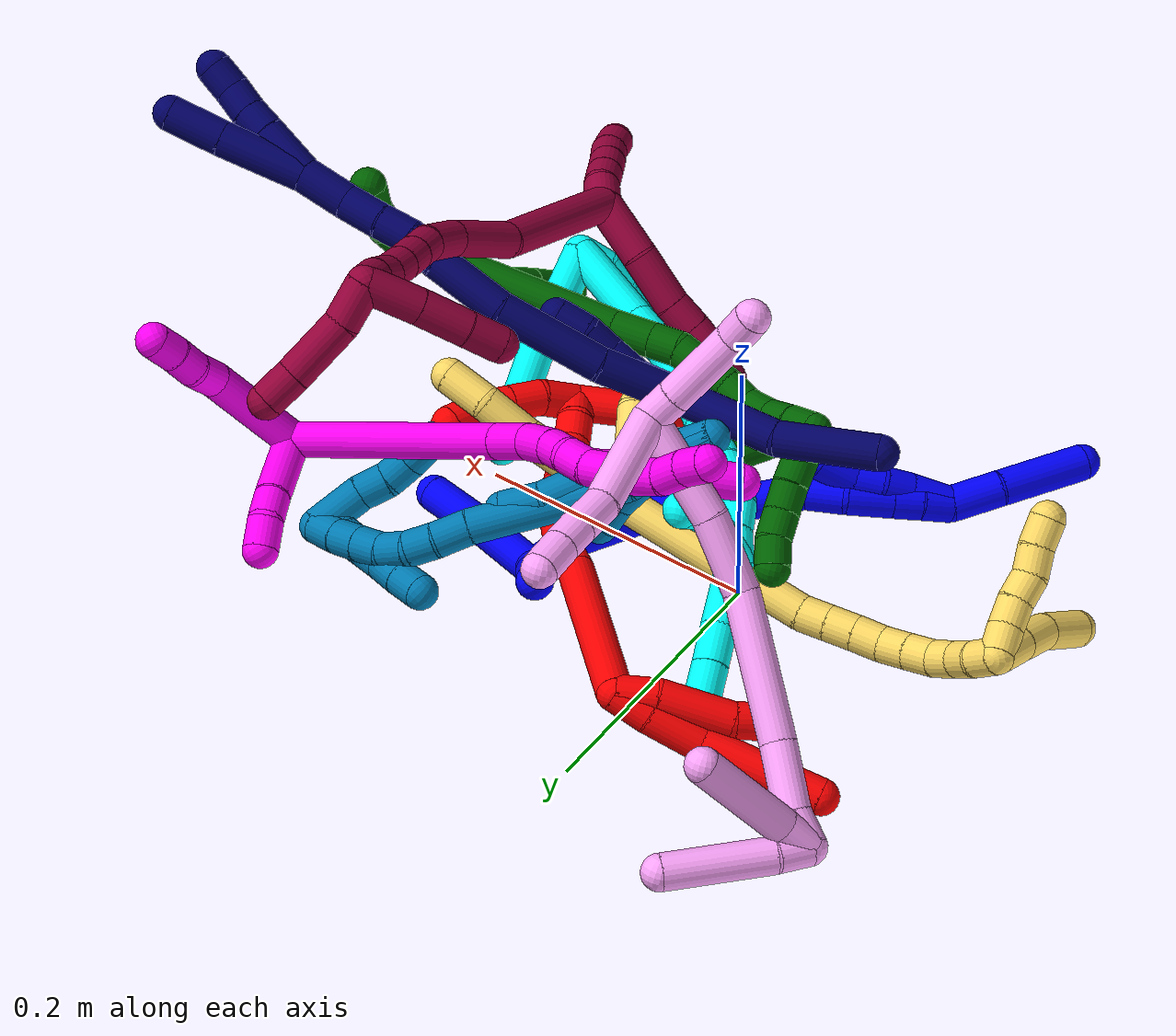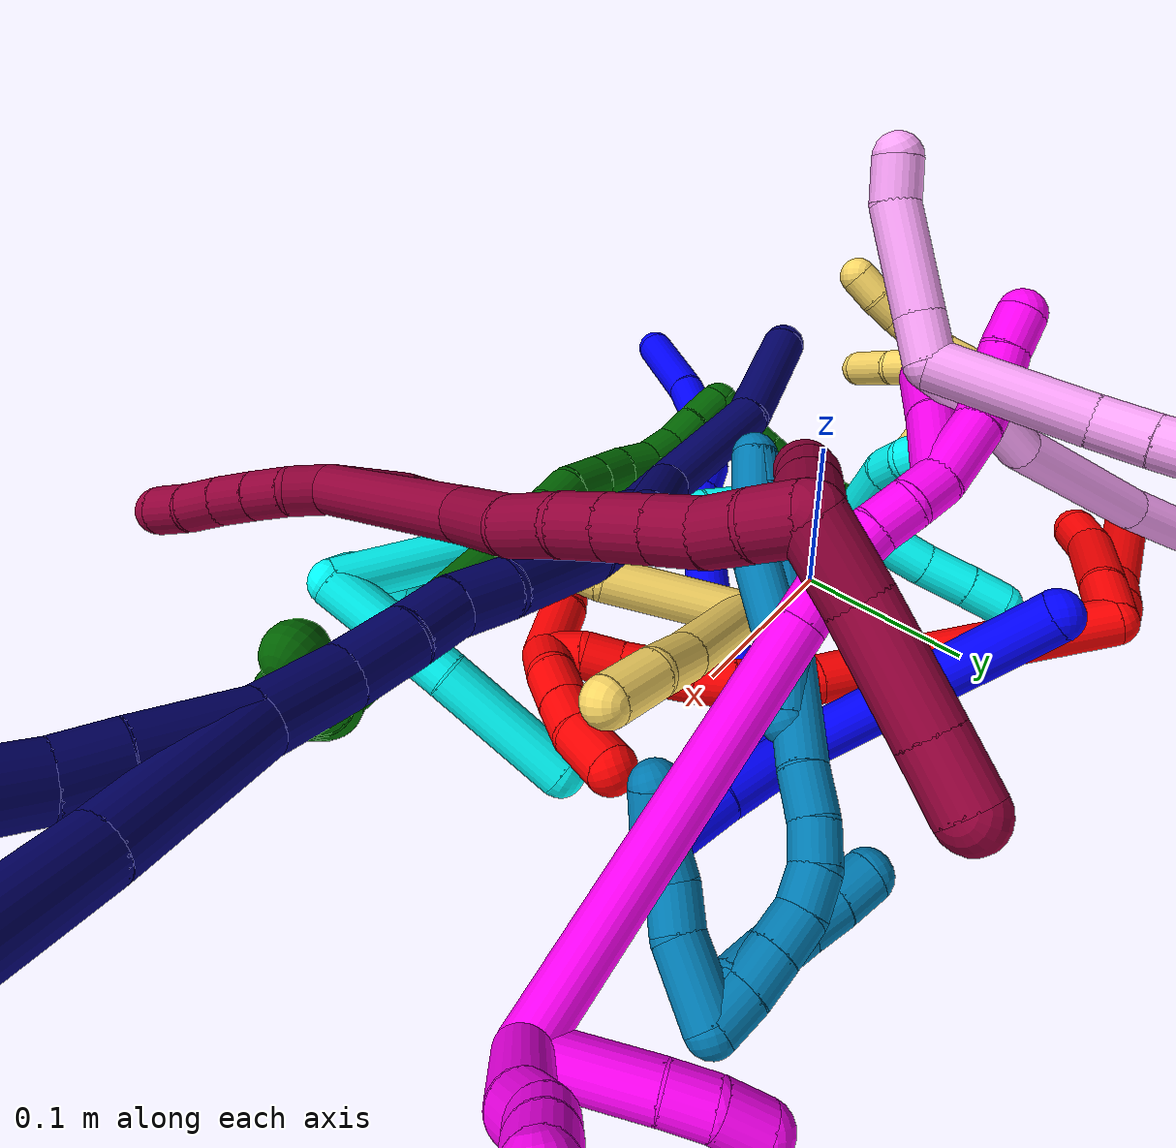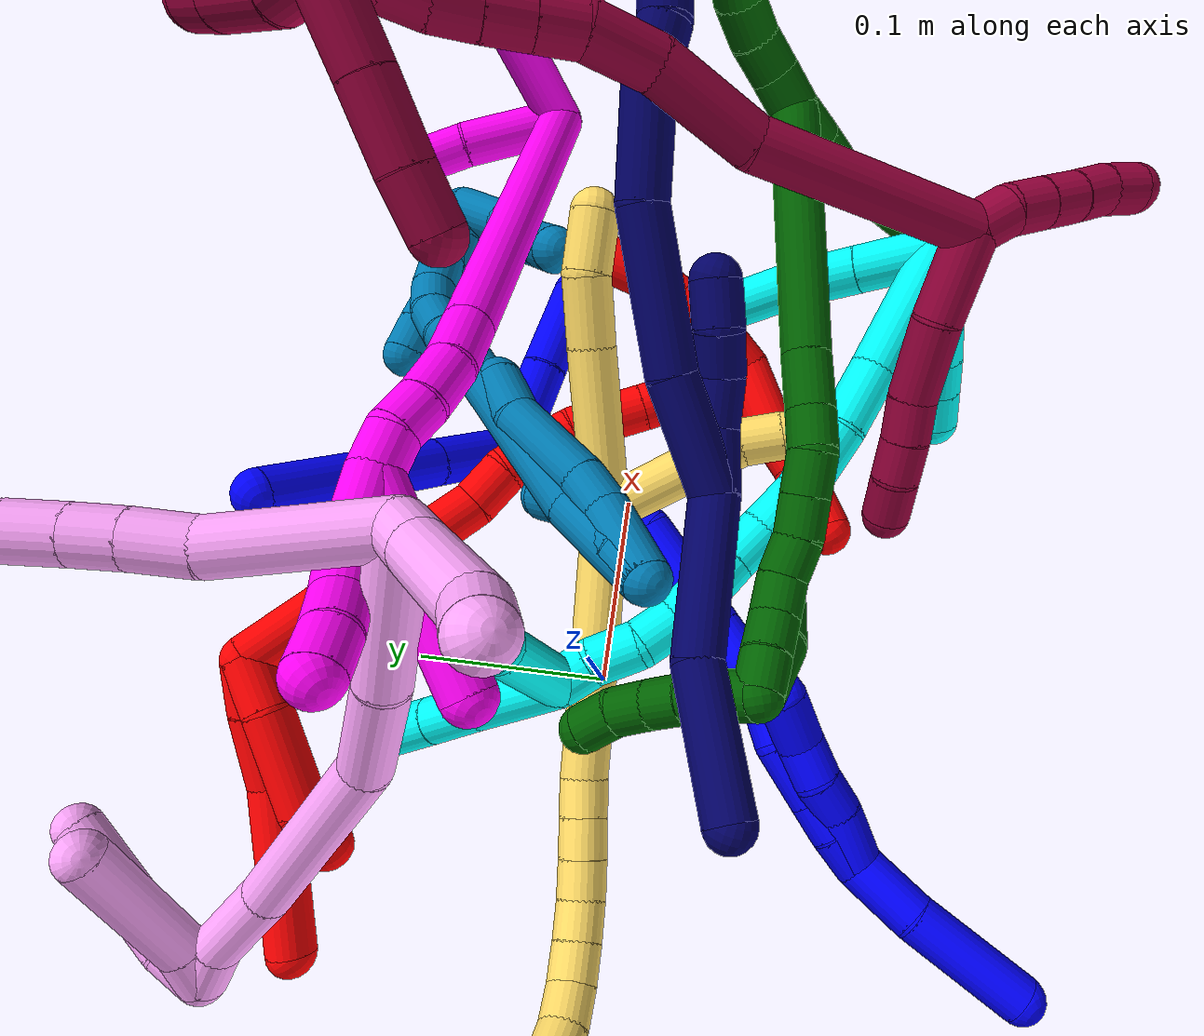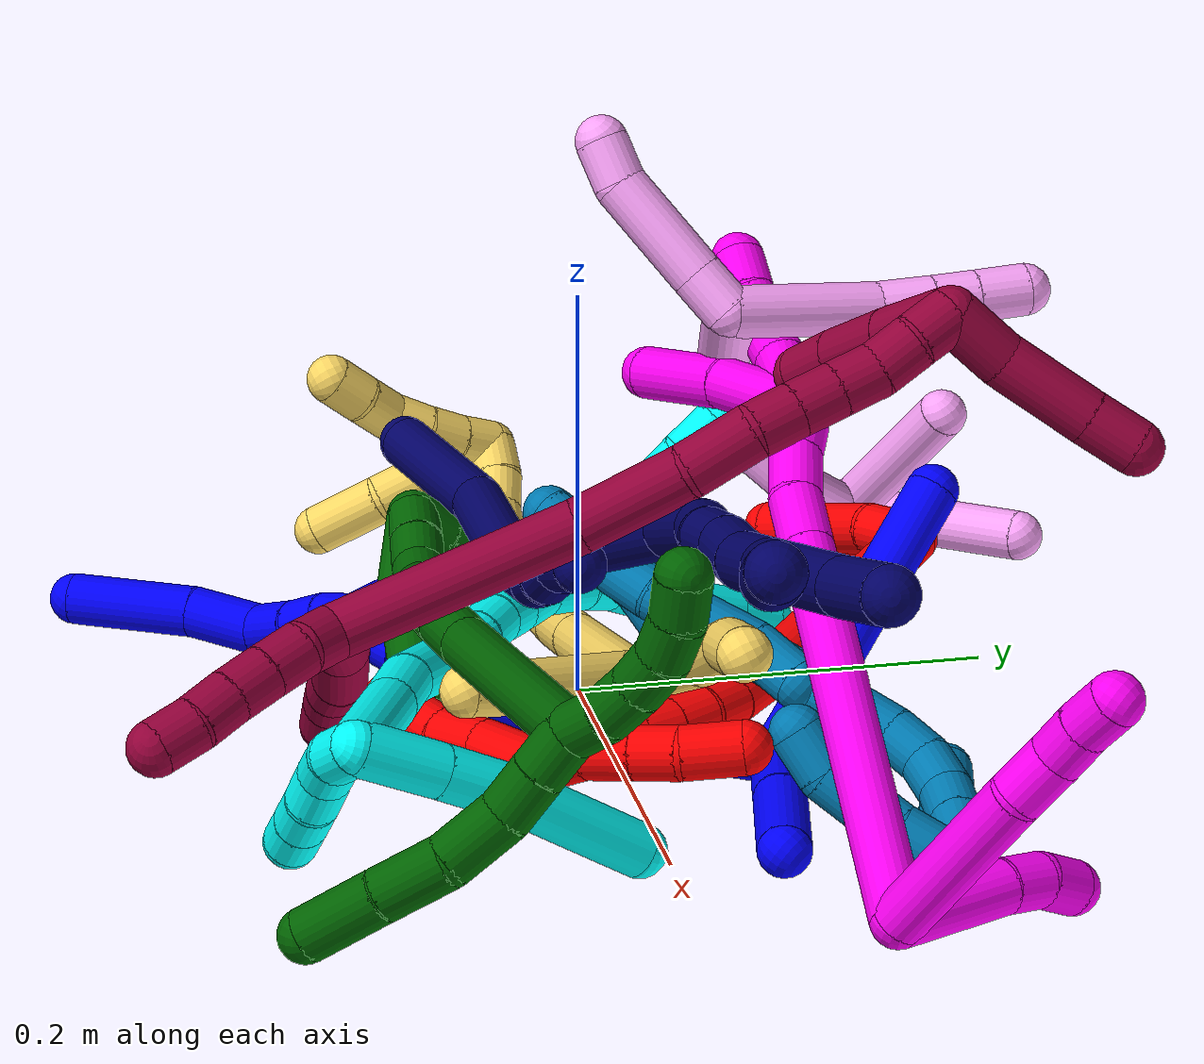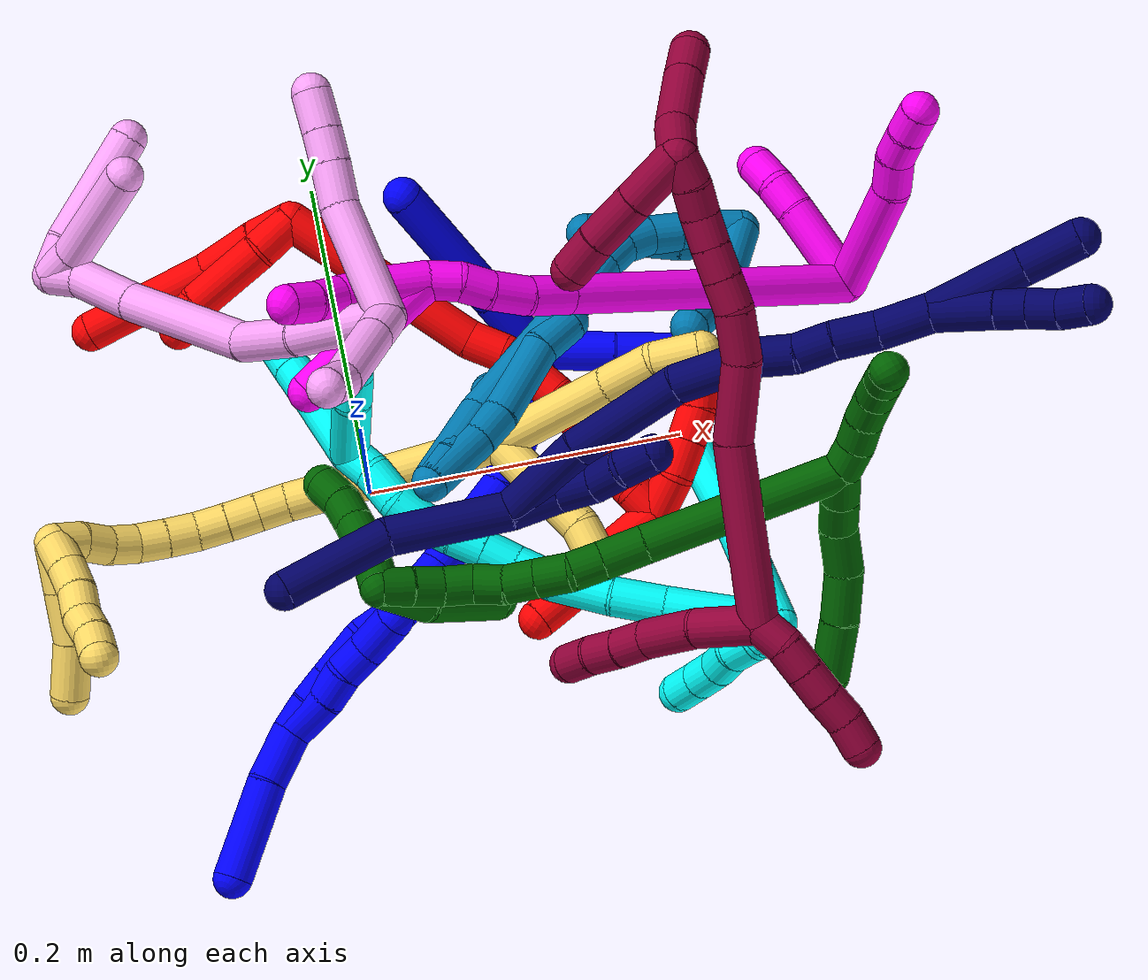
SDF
<sdf version="1.7">
 <world name="default">
  <plugin name="TubeGeneratorPlugin" filename="libtube_generator_plugin.so"/>
  <model name="photoneo_s_sensor">
   <static>1</static>
   <pose>0 0 2 1.57079 1.57079 3.14159</pose>
   <link name="link">
    <inertial><mass>0.1</mass></inertial>
    <sensor name="sensor" type="depth">
     <update_rate>30</update_rate>
     <camera>
      <horizontal_fov>1.22</horizontal_fov>
      <image><width>1920</width><height>1200</height><format>B8G8R8</format></image>
      <clip><near>0.1</near><far>4</far></clip>
      <depth_camera><output>points</output></depth_camera>
     </camera>
     <plugin name="camera_plugin" filename="libgazebo_ros_depth_camera.so">
      <baseline>0.2</baseline>
      <alwaysOn>1</alwaysOn>
      <updateRate>0.0</updateRate>
      <cameraName>camera_ir</cameraName>
      <imageTopicName>/camera/color/image_raw</imageTopicName>
      <cameraInfoTopicName>/camera/color/camera_info</cameraInfoTopicName>
      <depthImageTopicName>/camera/depth/image_raw</depthImageTopicName>
      <depthImageCameraInfoTopicName>/camera/depth/camera_info</depthImageCameraInfoTopicName>
      <pointCloudTopicName>/camera/depth/points</pointCloudTopicName>
      <frameName>fr_optical</frameName>
      <pointCloudCutoff>0.1</pointCloudCutoff>
      <pointCloudCutoffMax>2.0</pointCloudCutoffMax>
      <distortionK1>0</distortionK1>
      <distortionK2>0</distortionK2>
      <distortionK3>0</distortionK3>
      <distortionT1>0</distortionT1>
      <distortionT2>0</distortionT2>
      <CxPrime>0</CxPrime>
      <Cx>0</Cx>
      <Cy>0</Cy>
      <focalLength>0</focalLength>
      <hackBaseline>0</hackBaseline>
     </plugin>
    </sensor>
   </link>
  </model>
  <gravity>0 0 -9.8</gravity>
  <magnetic_field>6e-06 2.3e-05 -4.2e-05</magnetic_field>
  <atmosphere type="adiabatic"/>
  <physics name="default_physics" default="0" type="ode">
   <max_step_size>0.003</max_step_size>
   <real_time_factor>1</real_time_factor>
   <real_time_update_rate>1000</real_time_update_rate>
   <max_contacts>10000</max_contacts>
   <ode>
    <solver>
     <type>quick</type>
     <iters>100</iters>
     <sor>1.3</sor>
     <use_dynamic_moi_rescaling>0</use_dynamic_moi_rescaling>
    </solver>
    <constraints>
     <contact_max_correcting_vel>0</contact_max_correcting_vel>
     <contact_surface_layer>0.001</contact_surface_layer>
     <cfm>0</cfm>
     <erp>0.2</erp>
    </constraints>
   </ode>
  </physics>
  <scene><ambient>0.4 0.4 0.4 1</ambient><background>0.7 0.7 0.7 1</background><shadows>0</shadows></scene>
  <audio><device>default</device></audio>
  <spherical_coordinates>
   <surface_model>EARTH_WGS84</surface_model>
   <latitude_deg>0</latitude_deg>
   <longitude_deg>0</longitude_deg>
   <elevation>0</elevation>
   <heading_deg>0</heading_deg>
  </spherical_coordinates>
  <model name="bin">
   <static>1</static>
   <link name="bottom">
    <collision name="collision-bottom">
     <pose>0 0 -0.01 0 -0 0</pose>
     <geometry><box><size>0.8 0.6 0.02</size></box></geometry>
     <surface>
      <friction><ode><mu>100</mu><mu2>100</mu2></ode></friction>
      <contact><collide_bitmask>65535</collide_bitmask></contact>
     </surface>
    </collision>
   </link>
   <link name="west_wall">
    <collision name="collision-west_wall">
     <pose>-0.41 0 0.1 0 -0 0</pose>
     <geometry><box><size>0.02 0.6 0.2</size></box></geometry>
     <surface>
      <friction><ode><mu>100</mu><mu2>100</mu2></ode></friction>
      <contact><collide_bitmask>65535</collide_bitmask></contact>
     </surface>
    </collision>
   </link>
   <link name="east_wall">
    <collision name="collision-east_wall">
     <pose>0.41 0 0.1 0 -0 0</pose>
     <geometry><box><size>0.02 0.6 0.2</size></box></geometry>
     <surface>
      <friction><ode><mu>100</mu><mu2>100</mu2></ode></friction>
      <contact><collide_bitmask>65535</collide_bitmask></contact>
     </surface>
    </collision>
   </link>
   <link name="south_wall">
    <collision name="collision-south_wall">
     <pose>0 -0.31 0.1 0 -0 0</pose>
     <geometry><box><size>0.8 0.02 0.2</size></box></geometry>
     <surface>
      <friction><ode><mu>100</mu><mu2>100</mu2></ode></friction>
      <contact><collide_bitmask>65535</collide_bitmask></contact>
     </surface>
    </collision>
   </link>
   <link name="north_wall">
    <collision name="collision-north_wall">
     <pose>0 0.31 0.1 0 -0 0</pose>
     <geometry><box><size>0.8 0.02 0.2</size></box></geometry>
     <surface>
      <friction><ode><mu>100</mu><mu2>100</mu2></ode></friction>
      <contact><collide_bitmask>65535</collide_bitmask></contact>
     </surface>
    </collision>
   </link>
  </model>
  <model name="1">
   <static>0</static>
   <link name="1">
    <collision name="collision-cylinder-e_1_2_8">
     <pose>-0.020446 0.01611 0.005331 -1.25121 -0.878056 0.654109</pose>
     <geometry><cylinder><radius>0.0125</radius><length>0.053141</length></cylinder></geometry>
     <surface>
      <friction><ode><mu>1.16</mu><mu2>1.16</mu2><slip1>0</slip1><slip2>0</slip2></ode></friction>
      <contact><ode><kp>1e+06</kp><kd>1</kd><max_vel>0</max_vel><min_depth>0.001</min_depth></ode></contact>
     </surface>
    </collision>
    <visual name="visual-cylinder-e_1_2_8">
     <pose>-0.020446 0.01611 0.005331 -1.25121 -0.878056 0.654109</pose>
     <geometry><cylinder><radius>0.0125</radius><length>0.053141</length></cylinder></geometry>
     <material><ambient>0 0 1 1</ambient></material>
    </visual>
    <collision name="collision-cylinder-e_2_8_6">
     <pose>-0.078157 0.061573 0.020414 -1.25005 -0.878021 0.653334</pose>
     <geometry><cylinder><radius>0.0125</radius><length>0.096859</length></cylinder></geometry>
     <surface>
      <friction><ode><mu>1.16</mu><mu2>1.16</mu2><slip1>0</slip1><slip2>0</slip2></ode></friction>
      <contact><ode><kp>1e+06</kp><kd>1</kd><max_vel>0</max_vel><min_depth>0.001</min_depth></ode></contact>
     </surface>
    </collision>
    <visual name="visual-cylinder-e_2_8_6">
     <pose>-0.078157 0.061573 0.020414 -1.25005 -0.878021 0.653334</pose>
     <geometry><cylinder><radius>0.0125</radius><length>0.096859</length></cylinder></geometry>
     <material><ambient>0 0 1 1</ambient></material>
    </visual>
    <collision name="collision-cylinder-e_1_2_9">
     <pose>0.021272 0.008447 -0.010253 -2.45248 1.01256 -1.99277</pose>
     <geometry><cylinder><radius>0.0125</radius><length>0.050158</length></cylinder></geometry>
     <surface>
      <friction><ode><mu>1.16</mu><mu2>1.16</mu2><slip1>0</slip1><slip2>0</slip2></ode></friction>
      <contact><ode><kp>1e+06</kp><kd>1</kd><max_vel>0</max_vel><min_depth>0.001</min_depth></ode></contact>
     </surface>
    </collision>
    <visual name="visual-cylinder-e_1_2_9">
     <pose>0.021272 0.008447 -0.010253 -2.45248 1.01256 -1.99277</pose>
     <geometry><cylinder><radius>0.0125</radius><length>0.050158</length></cylinder></geometry>
     <material><ambient>0 0 1 1</ambient></material>
    </visual>
    <collision name="collision-cylinder-e_2_9_5">
     <pose>0.06371 0.023349 -0.031968 -2.62868 1.01471 -2.26004</pose>
     <geometry><cylinder><radius>0.0125</radius><length>0.049842</length></cylinder></geometry>
     <surface>
      <friction><ode><mu>1.16</mu><mu2>1.16</mu2><slip1>0</slip1><slip2>0</slip2></ode></friction>
      <contact><ode><kp>1e+06</kp><kd>1</kd><max_vel>0</max_vel><min_depth>0.001</min_depth></ode></contact>
     </surface>
    </collision>
    <visual name="visual-cylinder-e_2_9_5">
     <pose>0.06371 0.023349 -0.031968 -2.62868 1.01471 -2.26004</pose>
     <geometry><cylinder><radius>0.0125</radius><length>0.049842</length></cylinder></geometry>
     <material><ambient>0 0 1 1</ambient></material>
    </visual>
    <collision name="collision-cylinder-e_1_2_10">
     <pose>0.007816 -0.004168 0.013023 0.309744 0.519279 0.082896</pose>
     <geometry><cylinder><radius>0.0125</radius><length>0.031501</length></cylinder></geometry>
     <surface>
      <friction><ode><mu>1.16</mu><mu2>1.16</mu2><slip1>0</slip1><slip2>0</slip2></ode></friction>
      <contact><ode><kp>1e+06</kp><kd>1</kd><max_vel>0</max_vel><min_depth>0.001</min_depth></ode></contact>
     </surface>
    </collision>
    <visual name="visual-cylinder-e_1_2_10">
     <pose>0.007816 -0.004168 0.013023 0.309744 0.519279 0.082896</pose>
     <geometry><cylinder><radius>0.0125</radius><length>0.031501</length></cylinder></geometry>
     <material><ambient>0 0 1 1</ambient></material>
    </visual>
    <collision name="collision-cylinder-e_2_10_11">
     <pose>0.02217 -0.021716 0.052897 0.462296 0.214583 0.050687</pose>
     <geometry><cylinder><radius>0.0125</radius><length>0.061407</length></cylinder></geometry>
     <surface>
      <friction><ode><mu>1.16</mu><mu2>1.16</mu2><slip1>0</slip1><slip2>0</slip2></ode></friction>
      <contact><ode><kp>1e+06</kp><kd>1</kd><max_vel>0</max_vel><min_depth>0.001</min_depth></ode></contact>
     </surface>
    </collision>
    <visual name="visual-cylinder-e_2_10_11">
     <pose>0.02217 -0.021716 0.052897 0.462296 0.214583 0.050687</pose>
     <geometry><cylinder><radius>0.0125</radius><length>0.061407</length></cylinder></geometry>
     <material><ambient>0 0 1 1</ambient></material>
    </visual>
    <collision name="collision-cylinder-e_3_11_12">
     <pose>0.026158 -0.050798 0.108169 0.504756 -0.078372 -0.02022</pose>
     <geometry><cylinder><radius>0.0125</radius><length>0.065141</length></cylinder></geometry>
     <surface>
      <friction><ode><mu>1.16</mu><mu2>1.16</mu2><slip1>0</slip1><slip2>0</slip2></ode></friction>
      <contact><ode><kp>1e+06</kp><kd>1</kd><max_vel>0</max_vel><min_depth>0.001</min_depth></ode></contact>
     </surface>
    </collision>
    <visual name="visual-cylinder-e_3_11_12">
     <pose>0.026158 -0.050798 0.108169 0.504756 -0.078372 -0.02022</pose>
     <geometry><cylinder><radius>0.0125</radius><length>0.065141</length></cylinder></geometry>
     <material><ambient>0 0 1 1</ambient></material>
    </visual>
    <collision name="collision-cylinder-e_4_12_13">
     <pose>0.021408 -0.073612 0.155308 0.363045 -0.109426 -0.020104</pose>
     <geometry><cylinder><radius>0.0125</radius><length>0.040287</length></cylinder></geometry>
     <surface>
      <friction><ode><mu>1.16</mu><mu2>1.16</mu2><slip1>0</slip1><slip2>0</slip2></ode></friction>
      <contact><ode><kp>1e+06</kp><kd>1</kd><max_vel>0</max_vel><min_depth>0.001</min_depth></ode></contact>
     </surface>
    </collision>
    <visual name="visual-cylinder-e_4_12_13">
     <pose>0.021408 -0.073612 0.155308 0.363045 -0.109426 -0.020104</pose>
     <geometry><cylinder><radius>0.0125</radius><length>0.040287</length></cylinder></geometry>
     <material><ambient>0 0 1 1</ambient></material>
    </visual>
    <collision name="collision-cylinder-e_5_13_14">
     <pose>0.014009 -0.08719 0.185043 0.530867 -0.386514 -0.106301</pose>
     <geometry><cylinder><radius>0.0125</radius><length>0.027587</length></cylinder></geometry>
     <surface>
      <friction><ode><mu>1.16</mu><mu2>1.16</mu2><slip1>0</slip1><slip2>0</slip2></ode></friction>
      <contact><ode><kp>1e+06</kp><kd>1</kd><max_vel>0</max_vel><min_depth>0.001</min_depth></ode></contact>
     </surface>
    </collision>
    <visual name="visual-cylinder-e_5_13_14">
     <pose>0.014009 -0.08719 0.185043 0.530867 -0.386514 -0.106301</pose>
     <geometry><cylinder><radius>0.0125</radius><length>0.027587</length></cylinder></geometry>
     <material><ambient>0 0 1 1</ambient></material>
    </visual>
    <collision name="collision-cylinder-e_6_14_15">
     <pose>0.007068 -0.104254 0.208285 0.714118 -0.107261 -0.040047</pose>
     <geometry><cylinder><radius>0.0125</radius><length>0.032542</length></cylinder></geometry>
     <surface>
      <friction><ode><mu>1.16</mu><mu2>1.16</mu2><slip1>0</slip1><slip2>0</slip2></ode></friction>
      <contact><ode><kp>1e+06</kp><kd>1</kd><max_vel>0</max_vel><min_depth>0.001</min_depth></ode></contact>
     </surface>
    </collision>
    <visual name="visual-cylinder-e_6_14_15">
     <pose>0.007068 -0.104254 0.208285 0.714118 -0.107261 -0.040047</pose>
     <geometry><cylinder><radius>0.0125</radius><length>0.032542</length></cylinder></geometry>
     <material><ambient>0 0 1 1</ambient></material>
    </visual>
    <collision name="collision-cylinder-e_7_15_16">
     <pose>0.004301 -0.121381 0.228109 0.710076 -0.101948 -0.037825</pose>
     <geometry><cylinder><radius>0.0125</radius><length>0.020145</length></cylinder></geometry>
     <surface>
      <friction><ode><mu>1.16</mu><mu2>1.16</mu2><slip1>0</slip1><slip2>0</slip2></ode></friction>
      <contact><ode><kp>1e+06</kp><kd>1</kd><max_vel>0</max_vel><min_depth>0.001</min_depth></ode></contact>
     </surface>
    </collision>
    <visual name="visual-cylinder-e_7_15_16">
     <pose>0.004301 -0.121381 0.228109 0.710076 -0.101948 -0.037825</pose>
     <geometry><cylinder><radius>0.0125</radius><length>0.020145</length></cylinder></geometry>
     <material><ambient>0 0 1 1</ambient></material>
    </visual>
    <collision name="collision-cylinder-e_8_16_1">
     <pose>0.003143 -0.135507 0.243237 0.789586 -0.012435 -0.005181</pose>
     <geometry><cylinder><radius>0.0125</radius><length>0.021391</length></cylinder></geometry>
     <surface>
      <friction><ode><mu>1.16</mu><mu2>1.16</mu2><slip1>0</slip1><slip2>0</slip2></ode></friction>
      <contact><ode><kp>1e+06</kp><kd>1</kd><max_vel>0</max_vel><min_depth>0.001</min_depth></ode></contact>
     </surface>
    </collision>
    <visual name="visual-cylinder-e_8_16_1">
     <pose>0.003143 -0.135507 0.243237 0.789586 -0.012435 -0.005181</pose>
     <geometry><cylinder><radius>0.0125</radius><length>0.021391</length></cylinder></geometry>
     <material><ambient>0 0 1 1</ambient></material>
    </visual>
    <collision name="collision-cylinder-e_1_1_17">
     <pose>0.005377 -0.150442 0.267244 0.419143 0.130494 0.027793</pose>
     <geometry><cylinder><radius>0.0125</radius><length>0.036385</length></cylinder></geometry>
     <surface>
      <friction><ode><mu>1.16</mu><mu2>1.16</mu2><slip1>0</slip1><slip2>0</slip2></ode></friction>
      <contact><ode><kp>1e+06</kp><kd>1</kd><max_vel>0</max_vel><min_depth>0.001</min_depth></ode></contact>
     </surface>
    </collision>
    <visual name="visual-cylinder-e_1_1_17">
     <pose>0.005377 -0.150442 0.267244 0.419143 0.130494 0.027793</pose>
     <geometry><cylinder><radius>0.0125</radius><length>0.036385</length></cylinder></geometry>
     <material><ambient>0 0 1 1</ambient></material>
    </visual>
    <collision name="collision-cylinder-e_2_17_4">
     <pose>0.015225 -0.173413 0.310394 0.530036 0.237418 0.064718</pose>
     <geometry><cylinder><radius>0.0125</radius><length>0.063615</length></cylinder></geometry>
     <surface>
      <friction><ode><mu>1.16</mu><mu2>1.16</mu2><slip1>0</slip1><slip2>0</slip2></ode></friction>
      <contact><ode><kp>1e+06</kp><kd>1</kd><max_vel>0</max_vel><min_depth>0.001</min_depth></ode></contact>
     </surface>
    </collision>
    <visual name="visual-cylinder-e_2_17_4">
     <pose>0.015225 -0.173413 0.310394 0.530036 0.237418 0.064718</pose>
     <geometry><cylinder><radius>0.0125</radius><length>0.063615</length></cylinder></geometry>
     <material><ambient>0 0 1 1</ambient></material>
    </visual>
    <collision name="collision-cylinder-e_1_1_18">
     <pose>0.006571 -0.131406 0.24177 -2.22659 0.236862 -0.474262</pose>
     <geometry><cylinder><radius>0.0125</radius><length>0.030358</length></cylinder></geometry>
     <surface>
      <friction><ode><mu>1.16</mu><mu2>1.16</mu2><slip1>0</slip1><slip2>0</slip2></ode></friction>
      <contact><ode><kp>1e+06</kp><kd>1</kd><max_vel>0</max_vel><min_depth>0.001</min_depth></ode></contact>
     </surface>
    </collision>
    <visual name="visual-cylinder-e_1_1_18">
     <pose>0.006571 -0.131406 0.24177 -2.22659 0.236862 -0.474262</pose>
     <geometry><cylinder><radius>0.0125</radius><length>0.030358</length></cylinder></geometry>
     <material><ambient>0 0 1 1</ambient></material>
    </visual>
    <collision name="collision-cylinder-e_2_18_19">
     <pose>0.010624 -0.111182 0.226719 -2.18797 0.046916 -0.090778</pose>
     <geometry><cylinder><radius>0.0125</radius><length>0.020942</length></cylinder></geometry>
     <surface>
      <friction><ode><mu>1.16</mu><mu2>1.16</mu2><slip1>0</slip1><slip2>0</slip2></ode></friction>
      <contact><ode><kp>1e+06</kp><kd>1</kd><max_vel>0</max_vel><min_depth>0.001</min_depth></ode></contact>
     </surface>
    </collision>
    <visual name="visual-cylinder-e_2_18_19">
     <pose>0.010624 -0.111182 0.226719 -2.18797 0.046916 -0.090778</pose>
     <geometry><cylinder><radius>0.0125</radius><length>0.020942</length></cylinder></geometry>
     <material><ambient>0 0 1 1</ambient></material>
    </visual>
    <collision name="collision-cylinder-e_3_19_20">
     <pose>0.013402 -0.095493 0.213522 -2.35514 0.222286 -0.525622</pose>
     <geometry><cylinder><radius>0.0125</radius><length>0.02074</length></cylinder></geometry>
     <surface>
      <friction><ode><mu>1.16</mu><mu2>1.16</mu2><slip1>0</slip1><slip2>0</slip2></ode></friction>
      <contact><ode><kp>1e+06</kp><kd>1</kd><max_vel>0</max_vel><min_depth>0.001</min_depth></ode></contact>
     </surface>
    </collision>
    <visual name="visual-cylinder-e_3_19_20">
     <pose>0.013402 -0.095493 0.213522 -2.35514 0.222286 -0.525622</pose>
     <geometry><cylinder><radius>0.0125</radius><length>0.02074</length></cylinder></geometry>
     <material><ambient>0 0 1 1</ambient></material>
    </visual>
    <collision name="collision-cylinder-e_4_20_3">
     <pose>0.018127 -0.07597 0.200323 -2.02612 0.175377 -0.280021</pose>
     <geometry><cylinder><radius>0.0125</radius><length>0.02796</length></cylinder></geometry>
     <surface>
      <friction><ode><mu>1.16</mu><mu2>1.16</mu2><slip1>0</slip1><slip2>0</slip2></ode></friction>
      <contact><ode><kp>1e+06</kp><kd>1</kd><max_vel>0</max_vel><min_depth>0.001</min_depth></ode></contact>
     </surface>
    </collision>
    <visual name="visual-cylinder-e_4_20_3">
     <pose>0.018127 -0.07597 0.200323 -2.02612 0.175377 -0.280021</pose>
     <geometry><cylinder><radius>0.0125</radius><length>0.02796</length></cylinder></geometry>
     <material><ambient>0 0 1 1</ambient></material>
    </visual>
    <collision name="collision-sphere-3">
     <pose>0.020566 -0.063607 0.19427 0 -0 0</pose>
     <geometry><sphere><radius>0.0125</radius></sphere></geometry>
     <surface>
      <friction><ode><mu>1.16</mu><mu2>1.16</mu2><slip1>0</slip1><slip2>0</slip2></ode></friction>
      <contact><ode><kp>1e+06</kp><kd>1</kd><max_vel>0</max_vel><min_depth>0.001</min_depth></ode></contact>
     </surface>
    </collision>
    <visual name="visual-sphere-3">
     <pose>0.020566 -0.063607 0.19427 0 -0 0</pose>
     <geometry><sphere><radius>0.0125</radius></sphere></geometry>
     <material><ambient>0 0 1 1</ambient></material>
    </visual>
    <collision name="collision-sphere-20">
     <pose>0.015688 -0.088333 0.206377 0 -0 0</pose>
     <geometry><sphere><radius>0.0125</radius></sphere></geometry>
     <surface>
      <friction><ode><mu>1.16</mu><mu2>1.16</mu2><slip1>0</slip1><slip2>0</slip2></ode></friction>
      <contact><ode><kp>1e+06</kp><kd>1</kd><max_vel>0</max_vel><min_depth>0.001</min_depth></ode></contact>
     </surface>
    </collision>
    <visual name="visual-sphere-20">
     <pose>0.015688 -0.088333 0.206377 0 -0 0</pose>
     <geometry><sphere><radius>0.0125</radius></sphere></geometry>
     <material><ambient>0 0 1 1</ambient></material>
    </visual>
    <collision name="collision-sphere-19">
     <pose>0.011115 -0.102652 0.220666 0 -0 0</pose>
     <geometry><sphere><radius>0.0125</radius></sphere></geometry>
     <surface>
      <friction><ode><mu>1.16</mu><mu2>1.16</mu2><slip1>0</slip1><slip2>0</slip2></ode></friction>
      <contact><ode><kp>1e+06</kp><kd>1</kd><max_vel>0</max_vel><min_depth>0.001</min_depth></ode></contact>
     </surface>
    </collision>
    <visual name="visual-sphere-19">
     <pose>0.011115 -0.102652 0.220666 0 -0 0</pose>
     <geometry><sphere><radius>0.0125</radius></sphere></geometry>
     <material><ambient>0 0 1 1</ambient></material>
    </visual>
    <collision name="collision-sphere-10">
     <pose>0.015632 -0.008336 0.026047 0 -0 0</pose>
     <geometry><sphere><radius>0.0125</radius></sphere></geometry>
     <surface>
      <friction><ode><mu>1.16</mu><mu2>1.16</mu2><slip1>0</slip1><slip2>0</slip2></ode></friction>
      <contact><ode><kp>1e+06</kp><kd>1</kd><max_vel>0</max_vel><min_depth>0.001</min_depth></ode></contact>
     </surface>
    </collision>
    <visual name="visual-sphere-10">
     <pose>0.015632 -0.008336 0.026047 0 -0 0</pose>
     <geometry><sphere><radius>0.0125</radius></sphere></geometry>
     <material><ambient>0 0 1 1</ambient></material>
    </visual>
    <collision name="collision-sphere-5">
     <pose>0.084876 0.029804 -0.04343 0 -0 0</pose>
     <geometry><sphere><radius>0.0125</radius></sphere></geometry>
     <surface>
      <friction><ode><mu>1.16</mu><mu2>1.16</mu2><slip1>0</slip1><slip2>0</slip2></ode></friction>
      <contact><ode><kp>1e+06</kp><kd>1</kd><max_vel>0</max_vel><min_depth>0.001</min_depth></ode></contact>
     </surface>
    </collision>
    <visual name="visual-sphere-5">
     <pose>0.084876 0.029804 -0.04343 0 -0 0</pose>
     <geometry><sphere><radius>0.0125</radius></sphere></geometry>
     <material><ambient>0 0 1 1</ambient></material>
    </visual>
    <collision name="collision-sphere-6">
     <pose>-0.115423 0.090926 0.030166 0 -0 0</pose>
     <geometry><sphere><radius>0.0125</radius></sphere></geometry>
     <surface>
      <friction><ode><mu>1.16</mu><mu2>1.16</mu2><slip1>0</slip1><slip2>0</slip2></ode></friction>
      <contact><ode><kp>1e+06</kp><kd>1</kd><max_vel>0</max_vel><min_depth>0.001</min_depth></ode></contact>
     </surface>
    </collision>
    <visual name="visual-sphere-6">
     <pose>-0.115423 0.090926 0.030166 0 -0 0</pose>
     <geometry><sphere><radius>0.0125</radius></sphere></geometry>
     <material><ambient>0 0 1 1</ambient></material>
    </visual>
    <collision name="collision-sphere-9">
     <pose>0.042543 0.016893 -0.020505 0 -0 0</pose>
     <geometry><sphere><radius>0.0125</radius></sphere></geometry>
     <surface>
      <friction><ode><mu>1.16</mu><mu2>1.16</mu2><slip1>0</slip1><slip2>0</slip2></ode></friction>
      <contact><ode><kp>1e+06</kp><kd>1</kd><max_vel>0</max_vel><min_depth>0.001</min_depth></ode></contact>
     </surface>
    </collision>
    <visual name="visual-sphere-9">
     <pose>0.042543 0.016893 -0.020505 0 -0 0</pose>
     <geometry><sphere><radius>0.0125</radius></sphere></geometry>
     <material><ambient>0 0 1 1</ambient></material>
    </visual>
    <collision name="collision-sphere-2">
     <geometry><sphere><radius>0.0125</radius></sphere></geometry>
     <surface>
      <friction><ode><mu>1.16</mu><mu2>1.16</mu2><slip1>0</slip1><slip2>0</slip2></ode></friction>
      <contact><ode><kp>1e+06</kp><kd>1</kd><max_vel>0</max_vel><min_depth>0.001</min_depth></ode></contact>
     </surface>
    </collision>
    <visual name="visual-sphere-2">
     <geometry><sphere><radius>0.0125</radius></sphere></geometry>
     <material><ambient>0 0 1 1</ambient></material>
    </visual>
    <collision name="collision-sphere-8">
     <pose>-0.040892 0.03222 0.010662 0 -0 0</pose>
     <geometry><sphere><radius>0.0125</radius></sphere></geometry>
     <surface>
      <friction><ode><mu>1.16</mu><mu2>1.16</mu2><slip1>0</slip1><slip2>0</slip2></ode></friction>
      <contact><ode><kp>1e+06</kp><kd>1</kd><max_vel>0</max_vel><min_depth>0.001</min_depth></ode></contact>
     </surface>
    </collision>
    <visual name="visual-sphere-8">
     <pose>-0.040892 0.03222 0.010662 0 -0 0</pose>
     <geometry><sphere><radius>0.0125</radius></sphere></geometry>
     <material><ambient>0 0 1 1</ambient></material>
    </visual>
    <collision name="collision-sphere-11">
     <pose>0.028708 -0.035096 0.079747 0 -0 0</pose>
     <geometry><sphere><radius>0.0125</radius></sphere></geometry>
     <surface>
      <friction><ode><mu>1.16</mu><mu2>1.16</mu2><slip1>0</slip1><slip2>0</slip2></ode></friction>
      <contact><ode><kp>1e+06</kp><kd>1</kd><max_vel>0</max_vel><min_depth>0.001</min_depth></ode></contact>
     </surface>
    </collision>
    <visual name="visual-sphere-11">
     <pose>0.028708 -0.035096 0.079747 0 -0 0</pose>
     <geometry><sphere><radius>0.0125</radius></sphere></geometry>
     <material><ambient>0 0 1 1</ambient></material>
    </visual>
    <collision name="collision-sphere-12">
     <pose>0.023608 -0.066501 0.13659 0 -0 0</pose>
     <geometry><sphere><radius>0.0125</radius></sphere></geometry>
     <surface>
      <friction><ode><mu>1.16</mu><mu2>1.16</mu2><slip1>0</slip1><slip2>0</slip2></ode></friction>
      <contact><ode><kp>1e+06</kp><kd>1</kd><max_vel>0</max_vel><min_depth>0.001</min_depth></ode></contact>
     </surface>
    </collision>
    <visual name="visual-sphere-12">
     <pose>0.023608 -0.066501 0.13659 0 -0 0</pose>
     <geometry><sphere><radius>0.0125</radius></sphere></geometry>
     <material><ambient>0 0 1 1</ambient></material>
    </visual>
    <collision name="collision-sphere-13">
     <pose>0.019209 -0.080722 0.174026 0 -0 0</pose>
     <geometry><sphere><radius>0.0125</radius></sphere></geometry>
     <surface>
      <friction><ode><mu>1.16</mu><mu2>1.16</mu2><slip1>0</slip1><slip2>0</slip2></ode></friction>
      <contact><ode><kp>1e+06</kp><kd>1</kd><max_vel>0</max_vel><min_depth>0.001</min_depth></ode></contact>
     </surface>
    </collision>
    <visual name="visual-sphere-13">
     <pose>0.019209 -0.080722 0.174026 0 -0 0</pose>
     <geometry><sphere><radius>0.0125</radius></sphere></geometry>
     <material><ambient>0 0 1 1</ambient></material>
    </visual>
    <collision name="collision-sphere-14">
     <pose>0.008809 -0.093659 0.196061 0 -0 0</pose>
     <geometry><sphere><radius>0.0125</radius></sphere></geometry>
     <surface>
      <friction><ode><mu>1.16</mu><mu2>1.16</mu2><slip1>0</slip1><slip2>0</slip2></ode></friction>
      <contact><ode><kp>1e+06</kp><kd>1</kd><max_vel>0</max_vel><min_depth>0.001</min_depth></ode></contact>
     </surface>
    </collision>
    <visual name="visual-sphere-14">
     <pose>0.008809 -0.093659 0.196061 0 -0 0</pose>
     <geometry><sphere><radius>0.0125</radius></sphere></geometry>
     <material><ambient>0 0 1 1</ambient></material>
    </visual>
    <collision name="collision-sphere-15">
     <pose>0.005326 -0.114849 0.22051 0 -0 0</pose>
     <geometry><sphere><radius>0.0125</radius></sphere></geometry>
     <surface>
      <friction><ode><mu>1.16</mu><mu2>1.16</mu2><slip1>0</slip1><slip2>0</slip2></ode></friction>
      <contact><ode><kp>1e+06</kp><kd>1</kd><max_vel>0</max_vel><min_depth>0.001</min_depth></ode></contact>
     </surface>
    </collision>
    <visual name="visual-sphere-15">
     <pose>0.005326 -0.114849 0.22051 0 -0 0</pose>
     <geometry><sphere><radius>0.0125</radius></sphere></geometry>
     <material><ambient>0 0 1 1</ambient></material>
    </visual>
    <collision name="collision-sphere-16">
     <pose>0.003276 -0.127913 0.235707 0 -0 0</pose>
     <geometry><sphere><radius>0.0125</radius></sphere></geometry>
     <surface>
      <friction><ode><mu>1.16</mu><mu2>1.16</mu2><slip1>0</slip1><slip2>0</slip2></ode></friction>
      <contact><ode><kp>1e+06</kp><kd>1</kd><max_vel>0</max_vel><min_depth>0.001</min_depth></ode></contact>
     </surface>
    </collision>
    <visual name="visual-sphere-16">
     <pose>0.003276 -0.127913 0.235707 0 -0 0</pose>
     <geometry><sphere><radius>0.0125</radius></sphere></geometry>
     <material><ambient>0 0 1 1</ambient></material>
    </visual>
    <collision name="collision-sphere-1">
     <pose>0.00301 -0.143101 0.250768 0 -0 0</pose>
     <geometry><sphere><radius>0.0125</radius></sphere></geometry>
     <surface>
      <friction><ode><mu>1.16</mu><mu2>1.16</mu2><slip1>0</slip1><slip2>0</slip2></ode></friction>
      <contact><ode><kp>1e+06</kp><kd>1</kd><max_vel>0</max_vel><min_depth>0.001</min_depth></ode></contact>
     </surface>
    </collision>
    <visual name="visual-sphere-1">
     <pose>0.00301 -0.143101 0.250768 0 -0 0</pose>
     <geometry><sphere><radius>0.0125</radius></sphere></geometry>
     <material><ambient>0 0 1 1</ambient></material>
    </visual>
    <collision name="collision-sphere-18">
     <pose>0.010133 -0.119712 0.232773 0 -0 0</pose>
     <geometry><sphere><radius>0.0125</radius></sphere></geometry>
     <surface>
      <friction><ode><mu>1.16</mu><mu2>1.16</mu2><slip1>0</slip1><slip2>0</slip2></ode></friction>
      <contact><ode><kp>1e+06</kp><kd>1</kd><max_vel>0</max_vel><min_depth>0.001</min_depth></ode></contact>
     </surface>
    </collision>
    <visual name="visual-sphere-18">
     <pose>0.010133 -0.119712 0.232773 0 -0 0</pose>
     <geometry><sphere><radius>0.0125</radius></sphere></geometry>
     <material><ambient>0 0 1 1</ambient></material>
    </visual>
    <collision name="collision-sphere-17">
     <pose>0.007744 -0.157783 0.283721 0 -0 0</pose>
     <geometry><sphere><radius>0.0125</radius></sphere></geometry>
     <surface>
      <friction><ode><mu>1.16</mu><mu2>1.16</mu2><slip1>0</slip1><slip2>0</slip2></ode></friction>
      <contact><ode><kp>1e+06</kp><kd>1</kd><max_vel>0</max_vel><min_depth>0.001</min_depth></ode></contact>
     </surface>
    </collision>
    <visual name="visual-sphere-17">
     <pose>0.007744 -0.157783 0.283721 0 -0 0</pose>
     <geometry><sphere><radius>0.0125</radius></sphere></geometry>
     <material><ambient>0 0 1 1</ambient></material>
    </visual>
    <collision name="collision-sphere-4">
     <pose>0.022706 -0.189042 0.337067 0 -0 0</pose>
     <geometry><sphere><radius>0.0125</radius></sphere></geometry>
     <surface>
      <friction><ode><mu>1.16</mu><mu2>1.16</mu2><slip1>0</slip1><slip2>0</slip2></ode></friction>
      <contact><ode><kp>1e+06</kp><kd>1</kd><max_vel>0</max_vel><min_depth>0.001</min_depth></ode></contact>
     </surface>
    </collision>
    <visual name="visual-sphere-4">
     <pose>0.022706 -0.189042 0.337067 0 -0 0</pose>
     <geometry><sphere><radius>0.0125</radius></sphere></geometry>
     <material><ambient>0 0 1 1</ambient></material>
    </visual>
    <inertial>
     <pose>0.003868 -0.049869 0.12051 0 -0 0</pose>
     <mass>0.75</mass>
     <inertia><ixx>0.00017</ixx><ixy>0</ixy><ixz>0</ixz><iyy>0.000192</iyy><iyz>0</iyz><izz>3.5e-05</izz></inertia>
    </inertial>
   </link>
   <pose>0.120277 0.06822 0.011233 1.04767 0.051183 -0.762656</pose>
  </model>
  <model name="2">
   <static>0</static>
   <link name="2">
    <collision name="collision-cylinder-e_1_2_8">
     <pose>-0.007371 -0.009193 0.005925 0.998279 -0.59305 -0.330113</pose>
     <geometry><cylinder><radius>0.0125</radius><length>0.026378</length></cylinder></geometry>
     <surface>
      <friction><ode><mu>1.16</mu><mu2>1.16</mu2><slip1>0</slip1><slip2>0</slip2></ode></friction>
      <contact><ode><kp>1e+06</kp><kd>1</kd><max_vel>0</max_vel><min_depth>0.001</min_depth></ode></contact>
     </surface>
    </collision>
    <visual name="visual-cylinder-e_1_2_8">
     <pose>-0.007371 -0.009193 0.005925 0.998279 -0.59305 -0.330113</pose>
     <geometry><cylinder><radius>0.0125</radius><length>0.026378</length></cylinder></geometry>
     <material><ambient>1 0 0 1</ambient></material>
    </visual>
    <collision name="collision-cylinder-e_2_8_9">
     <pose>-0.025148 -0.033207 0.018988 1.12201 -0.56398 -0.360135</pose>
     <geometry><cylinder><radius>0.0125</radius><length>0.03893</length></cylinder></geometry>
     <surface>
      <friction><ode><mu>1.16</mu><mu2>1.16</mu2><slip1>0</slip1><slip2>0</slip2></ode></friction>
      <contact><ode><kp>1e+06</kp><kd>1</kd><max_vel>0</max_vel><min_depth>0.001</min_depth></ode></contact>
     </surface>
    </collision>
    <visual name="visual-cylinder-e_2_8_9">
     <pose>-0.025148 -0.033207 0.018988 1.12201 -0.56398 -0.360135</pose>
     <geometry><cylinder><radius>0.0125</radius><length>0.03893</length></cylinder></geometry>
     <material><ambient>1 0 0 1</ambient></material>
    </visual>
    <collision name="collision-cylinder-e_3_9_6">
     <pose>-0.0516 -0.080749 0.04769 0.988069 -0.388679 -0.211222</pose>
     <geometry><cylinder><radius>0.0125</radius><length>0.084692</length></cylinder></geometry>
     <surface>
      <friction><ode><mu>1.16</mu><mu2>1.16</mu2><slip1>0</slip1><slip2>0</slip2></ode></friction>
      <contact><ode><kp>1e+06</kp><kd>1</kd><max_vel>0</max_vel><min_depth>0.001</min_depth></ode></contact>
     </surface>
    </collision>
    <visual name="visual-cylinder-e_3_9_6">
     <pose>-0.0516 -0.080749 0.04769 0.988069 -0.388679 -0.211222</pose>
     <geometry><cylinder><radius>0.0125</radius><length>0.084692</length></cylinder></geometry>
     <material><ambient>1 0 0 1</ambient></material>
    </visual>
    <collision name="collision-cylinder-e_1_2_10">
     <pose>-0.00237 -0.013021 0.004144 1.26267 -0.171731 -0.125707</pose>
     <geometry><cylinder><radius>0.0125</radius><length>0.027737</length></cylinder></geometry>
     <surface>
      <friction><ode><mu>1.16</mu><mu2>1.16</mu2><slip1>0</slip1><slip2>0</slip2></ode></friction>
      <contact><ode><kp>1e+06</kp><kd>1</kd><max_vel>0</max_vel><min_depth>0.001</min_depth></ode></contact>
     </surface>
    </collision>
    <visual name="visual-cylinder-e_1_2_10">
     <pose>-0.00237 -0.013021 0.004144 1.26267 -0.171731 -0.125707</pose>
     <geometry><cylinder><radius>0.0125</radius><length>0.027737</length></cylinder></geometry>
     <material><ambient>1 0 0 1</ambient></material>
    </visual>
    <collision name="collision-cylinder-e_2_10_11">
     <pose>-0.014678 -0.048493 0.01625 1.22998 -0.395246 -0.281018</pose>
     <geometry><cylinder><radius>0.0125</radius><length>0.051622</length></cylinder></geometry>
     <surface>
      <friction><ode><mu>1.16</mu><mu2>1.16</mu2><slip1>0</slip1><slip2>0</slip2></ode></friction>
      <contact><ode><kp>1e+06</kp><kd>1</kd><max_vel>0</max_vel><min_depth>0.001</min_depth></ode></contact>
     </surface>
    </collision>
    <visual name="visual-cylinder-e_2_10_11">
     <pose>-0.014678 -0.048493 0.01625 1.22998 -0.395246 -0.281018</pose>
     <geometry><cylinder><radius>0.0125</radius><length>0.051622</length></cylinder></geometry>
     <material><ambient>1 0 0 1</ambient></material>
    </visual>
    <collision name="collision-cylinder-e_3_11_5">
     <pose>-0.026954 -0.080965 0.024994 1.49303 -0.228502 -0.211522</pose>
     <geometry><cylinder><radius>0.0125</radius><length>0.020641</length></cylinder></geometry>
     <surface>
      <friction><ode><mu>1.16</mu><mu2>1.16</mu2><slip1>0</slip1><slip2>0</slip2></ode></friction>
      <contact><ode><kp>1e+06</kp><kd>1</kd><max_vel>0</max_vel><min_depth>0.001</min_depth></ode></contact>
     </surface>
    </collision>
    <visual name="visual-cylinder-e_3_11_5">
     <pose>-0.026954 -0.080965 0.024994 1.49303 -0.228502 -0.211522</pose>
     <geometry><cylinder><radius>0.0125</radius><length>0.020641</length></cylinder></geometry>
     <material><ambient>1 0 0 1</ambient></material>
    </visual>
    <collision name="collision-cylinder-e_1_2_12">
     <pose>0.010336 -0.006383 -0.066286 3.0456 0.153984 2.02779</pose>
     <geometry><cylinder><radius>0.0125</radius><length>0.134779</length></cylinder></geometry>
     <surface>
      <friction><ode><mu>1.16</mu><mu2>1.16</mu2><slip1>0</slip1><slip2>0</slip2></ode></friction>
      <contact><ode><kp>1e+06</kp><kd>1</kd><max_vel>0</max_vel><min_depth>0.001</min_depth></ode></contact>
     </surface>
    </collision>
    <visual name="visual-cylinder-e_1_2_12">
     <pose>0.010336 -0.006383 -0.066286 3.0456 0.153984 2.02779</pose>
     <geometry><cylinder><radius>0.0125</radius><length>0.134779</length></cylinder></geometry>
     <material><ambient>1 0 0 1</ambient></material>
    </visual>
    <collision name="collision-cylinder-e_2_12_13">
     <pose>0.024615 -0.011791 -0.143811 -3.05511 0.336269 -2.64238</pose>
     <geometry><cylinder><radius>0.0125</radius><length>0.023902</length></cylinder></geometry>
     <surface>
      <friction><ode><mu>1.16</mu><mu2>1.16</mu2><slip1>0</slip1><slip2>0</slip2></ode></friction>
      <contact><ode><kp>1e+06</kp><kd>1</kd><max_vel>0</max_vel><min_depth>0.001</min_depth></ode></contact>
     </surface>
    </collision>
    <visual name="visual-cylinder-e_2_12_13">
     <pose>0.024615 -0.011791 -0.143811 -3.05511 0.336269 -2.64238</pose>
     <geometry><cylinder><radius>0.0125</radius><length>0.023902</length></cylinder></geometry>
     <material><ambient>1 0 0 1</ambient></material>
    </visual>
    <collision name="collision-cylinder-e_3_13_14">
     <pose>0.030467 -0.01248 -0.165202 2.97914 0.183353 1.69216</pose>
     <geometry><cylinder><radius>0.0125</radius><length>0.020924</length></cylinder></geometry>
     <surface>
      <friction><ode><mu>1.16</mu><mu2>1.16</mu2><slip1>0</slip1><slip2>0</slip2></ode></friction>
      <contact><ode><kp>1e+06</kp><kd>1</kd><max_vel>0</max_vel><min_depth>0.001</min_depth></ode></contact>
     </surface>
    </collision>
    <visual name="visual-cylinder-e_3_13_14">
     <pose>0.030467 -0.01248 -0.165202 2.97914 0.183353 1.69216</pose>
     <geometry><cylinder><radius>0.0125</radius><length>0.020924</length></cylinder></geometry>
     <material><ambient>1 0 0 1</ambient></material>
    </visual>
    <collision name="collision-cylinder-e_4_14_15">
     <pose>0.035507 -0.016495 -0.184752 2.89644 0.312804 1.81519</pose>
     <geometry><cylinder><radius>0.0125</radius><length>0.020364</length></cylinder></geometry>
     <surface>
      <friction><ode><mu>1.16</mu><mu2>1.16</mu2><slip1>0</slip1><slip2>0</slip2></ode></friction>
      <contact><ode><kp>1e+06</kp><kd>1</kd><max_vel>0</max_vel><min_depth>0.001</min_depth></ode></contact>
     </surface>
    </collision>
    <visual name="visual-cylinder-e_4_14_15">
     <pose>0.035507 -0.016495 -0.184752 2.89644 0.312804 1.81519</pose>
     <geometry><cylinder><radius>0.0125</radius><length>0.020364</length></cylinder></geometry>
     <material><ambient>1 0 0 1</ambient></material>
    </visual>
    <collision name="collision-cylinder-e_5_15_16">
     <pose>0.040977 -0.022748 -0.203059 2.72878 0.235785 1.02956</pose>
     <geometry><cylinder><radius>0.0125</radius><length>0.020006</length></cylinder></geometry>
     <surface>
      <friction><ode><mu>1.16</mu><mu2>1.16</mu2><slip1>0</slip1><slip2>0</slip2></ode></friction>
      <contact><ode><kp>1e+06</kp><kd>1</kd><max_vel>0</max_vel><min_depth>0.001</min_depth></ode></contact>
     </surface>
    </collision>
    <visual name="visual-cylinder-e_5_15_16">
     <pose>0.040977 -0.022748 -0.203059 2.72878 0.235785 1.02956</pose>
     <geometry><cylinder><radius>0.0125</radius><length>0.020006</length></cylinder></geometry>
     <material><ambient>1 0 0 1</ambient></material>
    </visual>
    <collision name="collision-cylinder-e_6_16_17">
     <pose>0.045943 -0.031157 -0.220508 2.65599 0.265809 0.989899</pose>
     <geometry><cylinder><radius>0.0125</radius><length>0.020016</length></cylinder></geometry>
     <surface>
      <friction><ode><mu>1.16</mu><mu2>1.16</mu2><slip1>0</slip1><slip2>0</slip2></ode></friction>
      <contact><ode><kp>1e+06</kp><kd>1</kd><max_vel>0</max_vel><min_depth>0.001</min_depth></ode></contact>
     </surface>
    </collision>
    <visual name="visual-cylinder-e_6_16_17">
     <pose>0.045943 -0.031157 -0.220508 2.65599 0.265809 0.989899</pose>
     <geometry><cylinder><radius>0.0125</radius><length>0.020016</length></cylinder></geometry>
     <material><ambient>1 0 0 1</ambient></material>
    </visual>
    <collision name="collision-cylinder-e_7_17_18">
     <pose>0.051219 -0.040141 -0.23759 2.65892 0.267856 1.00169</pose>
     <geometry><cylinder><radius>0.0125</radius><length>0.020001</length></cylinder></geometry>
     <surface>
      <friction><ode><mu>1.16</mu><mu2>1.16</mu2><slip1>0</slip1><slip2>0</slip2></ode></friction>
      <contact><ode><kp>1e+06</kp><kd>1</kd><max_vel>0</max_vel><min_depth>0.001</min_depth></ode></contact>
     </surface>
    </collision>
    <visual name="visual-cylinder-e_7_17_18">
     <pose>0.051219 -0.040141 -0.23759 2.65892 0.267856 1.00169</pose>
     <geometry><cylinder><radius>0.0125</radius><length>0.020001</length></cylinder></geometry>
     <material><ambient>1 0 0 1</ambient></material>
    </visual>
    <collision name="collision-cylinder-e_8_18_19">
     <pose>0.058302 -0.048466 -0.25423 2.69784 0.45946 1.60678</pose>
     <geometry><cylinder><radius>0.0125</radius><length>0.020006</length></cylinder></geometry>
     <surface>
      <friction><ode><mu>1.16</mu><mu2>1.16</mu2><slip1>0</slip1><slip2>0</slip2></ode></friction>
      <contact><ode><kp>1e+06</kp><kd>1</kd><max_vel>0</max_vel><min_depth>0.001</min_depth></ode></contact>
     </surface>
    </collision>
    <visual name="visual-cylinder-e_8_18_19">
     <pose>0.058302 -0.048466 -0.25423 2.69784 0.45946 1.60678</pose>
     <geometry><cylinder><radius>0.0125</radius><length>0.020006</length></cylinder></geometry>
     <material><ambient>1 0 0 1</ambient></material>
    </visual>
    <collision name="collision-cylinder-e_9_19_1">
     <pose>0.064502 -0.055469 -0.271652 2.81554 0.177347 0.991058</pose>
     <geometry><cylinder><radius>0.0125</radius><length>0.020001</length></cylinder></geometry>
     <surface>
      <friction><ode><mu>1.16</mu><mu2>1.16</mu2><slip1>0</slip1><slip2>0</slip2></ode></friction>
      <contact><ode><kp>1e+06</kp><kd>1</kd><max_vel>0</max_vel><min_depth>0.001</min_depth></ode></contact>
     </surface>
    </collision>
    <visual name="visual-cylinder-e_9_19_1">
     <pose>0.064502 -0.055469 -0.271652 2.81554 0.177347 0.991058</pose>
     <geometry><cylinder><radius>0.0125</radius><length>0.020001</length></cylinder></geometry>
     <material><ambient>1 0 0 1</ambient></material>
    </visual>
    <collision name="collision-cylinder-e_1_1_20">
     <pose>0.071714 -0.046292 -0.279406 -1.44401 0.413095 -0.364938</pose>
     <geometry><cylinder><radius>0.0125</radius><length>0.027141</length></cylinder></geometry>
     <surface>
      <friction><ode><mu>1.16</mu><mu2>1.16</mu2><slip1>0</slip1><slip2>0</slip2></ode></friction>
      <contact><ode><kp>1e+06</kp><kd>1</kd><max_vel>0</max_vel><min_depth>0.001</min_depth></ode></contact>
     </surface>
    </collision>
    <visual name="visual-cylinder-e_1_1_20">
     <pose>0.071714 -0.046292 -0.279406 -1.44401 0.413095 -0.364938</pose>
     <geometry><cylinder><radius>0.0125</radius><length>0.027141</length></cylinder></geometry>
     <material><ambient>1 0 0 1</ambient></material>
    </visual>
    <collision name="collision-cylinder-e_2_20_21">
     <pose>0.078225 -0.022432 -0.276006 -1.41359 0.090804 -0.077558</pose>
     <geometry><cylinder><radius>0.0125</radius><length>0.023448</length></cylinder></geometry>
     <surface>
      <friction><ode><mu>1.16</mu><mu2>1.16</mu2><slip1>0</slip1><slip2>0</slip2></ode></friction>
      <contact><ode><kp>1e+06</kp><kd>1</kd><max_vel>0</max_vel><min_depth>0.001</min_depth></ode></contact>
     </surface>
    </collision>
    <visual name="visual-cylinder-e_2_20_21">
     <pose>0.078225 -0.022432 -0.276006 -1.41359 0.090804 -0.077558</pose>
     <geometry><cylinder><radius>0.0125</radius><length>0.023448</length></cylinder></geometry>
     <material><ambient>1 0 0 1</ambient></material>
    </visual>
    <collision name="collision-cylinder-e_3_21_22">
     <pose>0.080091 -0.000442 -0.272277 -1.39095 0.075399 -0.062936</pose>
     <geometry><cylinder><radius>0.0125</radius><length>0.021318</length></cylinder></geometry>
     <surface>
      <friction><ode><mu>1.16</mu><mu2>1.16</mu2><slip1>0</slip1><slip2>0</slip2></ode></friction>
      <contact><ode><kp>1e+06</kp><kd>1</kd><max_vel>0</max_vel><min_depth>0.001</min_depth></ode></contact>
     </surface>
    </collision>
    <visual name="visual-cylinder-e_3_21_22">
     <pose>0.080091 -0.000442 -0.272277 -1.39095 0.075399 -0.062936</pose>
     <geometry><cylinder><radius>0.0125</radius><length>0.021318</length></cylinder></geometry>
     <material><ambient>1 0 0 1</ambient></material>
    </visual>
    <collision name="collision-cylinder-e_4_22_4">
     <pose>0.080944 0.022866 -0.264705 -1.1552 0.003583 -0.002335</pose>
     <geometry><cylinder><radius>0.0125</radius><length>0.028093</length></cylinder></geometry>
     <surface>
      <friction><ode><mu>1.16</mu><mu2>1.16</mu2><slip1>0</slip1><slip2>0</slip2></ode></friction>
      <contact><ode><kp>1e+06</kp><kd>1</kd><max_vel>0</max_vel><min_depth>0.001</min_depth></ode></contact>
     </surface>
    </collision>
    <visual name="visual-cylinder-e_4_22_4">
     <pose>0.080944 0.022866 -0.264705 -1.1552 0.003583 -0.002335</pose>
     <geometry><cylinder><radius>0.0125</radius><length>0.028093</length></cylinder></geometry>
     <material><ambient>1 0 0 1</ambient></material>
    </visual>
    <collision name="collision-cylinder-e_1_1_23">
     <pose>0.063103 -0.075021 -0.27458 1.19884 -0.177777 -0.121643</pose>
     <geometry><cylinder><radius>0.0125</radius><length>0.03577</length></cylinder></geometry>
     <surface>
      <friction><ode><mu>1.16</mu><mu2>1.16</mu2><slip1>0</slip1><slip2>0</slip2></ode></friction>
      <contact><ode><kp>1e+06</kp><kd>1</kd><max_vel>0</max_vel><min_depth>0.001</min_depth></ode></contact>
     </surface>
    </collision>
    <visual name="visual-cylinder-e_1_1_23">
     <pose>0.063103 -0.075021 -0.27458 1.19884 -0.177777 -0.121643</pose>
     <geometry><cylinder><radius>0.0125</radius><length>0.03577</length></cylinder></geometry>
     <material><ambient>1 0 0 1</ambient></material>
    </visual>
    <collision name="collision-cylinder-e_2_23_24">
     <pose>0.05854 -0.103906 -0.265675 1.3726 -0.109536 -0.089755</pose>
     <geometry><cylinder><radius>0.0125</radius><length>0.025623</length></cylinder></geometry>
     <surface>
      <friction><ode><mu>1.16</mu><mu2>1.16</mu2><slip1>0</slip1><slip2>0</slip2></ode></friction>
      <contact><ode><kp>1e+06</kp><kd>1</kd><max_vel>0</max_vel><min_depth>0.001</min_depth></ode></contact>
     </surface>
    </collision>
    <visual name="visual-cylinder-e_2_23_24">
     <pose>0.05854 -0.103906 -0.265675 1.3726 -0.109536 -0.089755</pose>
     <geometry><cylinder><radius>0.0125</radius><length>0.025623</length></cylinder></geometry>
     <material><ambient>1 0 0 1</ambient></material>
    </visual>
    <collision name="collision-cylinder-e_3_24_3">
     <pose>0.05701 -0.134155 -0.255614 1.16875 -0.00672 -0.004445</pose>
     <geometry><cylinder><radius>0.0125</radius><length>0.038607</length></cylinder></geometry>
     <surface>
      <friction><ode><mu>1.16</mu><mu2>1.16</mu2><slip1>0</slip1><slip2>0</slip2></ode></friction>
      <contact><ode><kp>1e+06</kp><kd>1</kd><max_vel>0</max_vel><min_depth>0.001</min_depth></ode></contact>
     </surface>
    </collision>
    <visual name="visual-cylinder-e_3_24_3">
     <pose>0.05701 -0.134155 -0.255614 1.16875 -0.00672 -0.004445</pose>
     <geometry><cylinder><radius>0.0125</radius><length>0.038607</length></cylinder></geometry>
     <material><ambient>1 0 0 1</ambient></material>
    </visual>
    <collision name="collision-sphere-3">
     <pose>0.05688 -0.151919 -0.24806 0 -0 0</pose>
     <geometry><sphere><radius>0.0125</radius></sphere></geometry>
     <surface>
      <friction><ode><mu>1.16</mu><mu2>1.16</mu2><slip1>0</slip1><slip2>0</slip2></ode></friction>
      <contact><ode><kp>1e+06</kp><kd>1</kd><max_vel>0</max_vel><min_depth>0.001</min_depth></ode></contact>
     </surface>
    </collision>
    <visual name="visual-sphere-3">
     <pose>0.05688 -0.151919 -0.24806 0 -0 0</pose>
     <geometry><sphere><radius>0.0125</radius></sphere></geometry>
     <material><ambient>1 0 0 1</ambient></material>
    </visual>
    <collision name="collision-sphere-24">
     <pose>0.05714 -0.116391 -0.263167 0 -0 0</pose>
     <geometry><sphere><radius>0.0125</radius></sphere></geometry>
     <surface>
      <friction><ode><mu>1.16</mu><mu2>1.16</mu2><slip1>0</slip1><slip2>0</slip2></ode></friction>
      <contact><ode><kp>1e+06</kp><kd>1</kd><max_vel>0</max_vel><min_depth>0.001</min_depth></ode></contact>
     </surface>
    </collision>
    <visual name="visual-sphere-24">
     <pose>0.05714 -0.116391 -0.263167 0 -0 0</pose>
     <geometry><sphere><radius>0.0125</radius></sphere></geometry>
     <material><ambient>1 0 0 1</ambient></material>
    </visual>
    <collision name="collision-sphere-23">
     <pose>0.059941 -0.09142 -0.268182 0 -0 0</pose>
     <geometry><sphere><radius>0.0125</radius></sphere></geometry>
     <surface>
      <friction><ode><mu>1.16</mu><mu2>1.16</mu2><slip1>0</slip1><slip2>0</slip2></ode></friction>
      <contact><ode><kp>1e+06</kp><kd>1</kd><max_vel>0</max_vel><min_depth>0.001</min_depth></ode></contact>
     </surface>
    </collision>
    <visual name="visual-sphere-23">
     <pose>0.059941 -0.09142 -0.268182 0 -0 0</pose>
     <geometry><sphere><radius>0.0125</radius></sphere></geometry>
     <material><ambient>1 0 0 1</ambient></material>
    </visual>
    <collision name="collision-sphere-4">
     <pose>0.080995 0.035716 -0.259034 0 -0 0</pose>
     <geometry><sphere><radius>0.0125</radius></sphere></geometry>
     <surface>
      <friction><ode><mu>1.16</mu><mu2>1.16</mu2><slip1>0</slip1><slip2>0</slip2></ode></friction>
      <contact><ode><kp>1e+06</kp><kd>1</kd><max_vel>0</max_vel><min_depth>0.001</min_depth></ode></contact>
     </surface>
    </collision>
    <visual name="visual-sphere-4">
     <pose>0.080995 0.035716 -0.259034 0 -0 0</pose>
     <geometry><sphere><radius>0.0125</radius></sphere></geometry>
     <material><ambient>1 0 0 1</ambient></material>
    </visual>
    <collision name="collision-sphere-22">
     <pose>0.080894 0.010015 -0.270376 0 -0 0</pose>
     <geometry><sphere><radius>0.0125</radius></sphere></geometry>
     <surface>
      <friction><ode><mu>1.16</mu><mu2>1.16</mu2><slip1>0</slip1><slip2>0</slip2></ode></friction>
      <contact><ode><kp>1e+06</kp><kd>1</kd><max_vel>0</max_vel><min_depth>0.001</min_depth></ode></contact>
     </surface>
    </collision>
    <visual name="visual-sphere-22">
     <pose>0.080894 0.010015 -0.270376 0 -0 0</pose>
     <geometry><sphere><radius>0.0125</radius></sphere></geometry>
     <material><ambient>1 0 0 1</ambient></material>
    </visual>
    <collision name="collision-sphere-21">
     <pose>0.079288 -0.0109 -0.274178 0 -0 0</pose>
     <geometry><sphere><radius>0.0125</radius></sphere></geometry>
     <surface>
      <friction><ode><mu>1.16</mu><mu2>1.16</mu2><slip1>0</slip1><slip2>0</slip2></ode></friction>
      <contact><ode><kp>1e+06</kp><kd>1</kd><max_vel>0</max_vel><min_depth>0.001</min_depth></ode></contact>
     </surface>
    </collision>
    <visual name="visual-sphere-21">
     <pose>0.079288 -0.0109 -0.274178 0 -0 0</pose>
     <geometry><sphere><radius>0.0125</radius></sphere></geometry>
     <material><ambient>1 0 0 1</ambient></material>
    </visual>
    <collision name="collision-sphere-20">
     <pose>0.077162 -0.033963 -0.277834 0 -0 0</pose>
     <geometry><sphere><radius>0.0125</radius></sphere></geometry>
     <surface>
      <friction><ode><mu>1.16</mu><mu2>1.16</mu2><slip1>0</slip1><slip2>0</slip2></ode></friction>
      <contact><ode><kp>1e+06</kp><kd>1</kd><max_vel>0</max_vel><min_depth>0.001</min_depth></ode></contact>
     </surface>
    </collision>
    <visual name="visual-sphere-20">
     <pose>0.077162 -0.033963 -0.277834 0 -0 0</pose>
     <geometry><sphere><radius>0.0125</radius></sphere></geometry>
     <material><ambient>1 0 0 1</ambient></material>
    </visual>
    <collision name="collision-sphere-11">
     <pose>-0.024616 -0.070943 0.024213 0 -0 0</pose>
     <geometry><sphere><radius>0.0125</radius></sphere></geometry>
     <surface>
      <friction><ode><mu>1.16</mu><mu2>1.16</mu2><slip1>0</slip1><slip2>0</slip2></ode></friction>
      <contact><ode><kp>1e+06</kp><kd>1</kd><max_vel>0</max_vel><min_depth>0.001</min_depth></ode></contact>
     </surface>
    </collision>
    <visual name="visual-sphere-11">
     <pose>-0.024616 -0.070943 0.024213 0 -0 0</pose>
     <geometry><sphere><radius>0.0125</radius></sphere></geometry>
     <material><ambient>1 0 0 1</ambient></material>
    </visual>
    <collision name="collision-sphere-10">
     <pose>-0.00474 -0.026042 0.008288 0 -0 0</pose>
     <geometry><sphere><radius>0.0125</radius></sphere></geometry>
     <surface>
      <friction><ode><mu>1.16</mu><mu2>1.16</mu2><slip1>0</slip1><slip2>0</slip2></ode></friction>
      <contact><ode><kp>1e+06</kp><kd>1</kd><max_vel>0</max_vel><min_depth>0.001</min_depth></ode></contact>
     </surface>
    </collision>
    <visual name="visual-sphere-10">
     <pose>-0.00474 -0.026042 0.008288 0 -0 0</pose>
     <geometry><sphere><radius>0.0125</radius></sphere></geometry>
     <material><ambient>1 0 0 1</ambient></material>
    </visual>
    <collision name="collision-sphere-6">
     <pose>-0.067648 -0.113469 0.069255 0 -0 0</pose>
     <geometry><sphere><radius>0.0125</radius></sphere></geometry>
     <surface>
      <friction><ode><mu>1.16</mu><mu2>1.16</mu2><slip1>0</slip1><slip2>0</slip2></ode></friction>
      <contact><ode><kp>1e+06</kp><kd>1</kd><max_vel>0</max_vel><min_depth>0.001</min_depth></ode></contact>
     </surface>
    </collision>
    <visual name="visual-sphere-6">
     <pose>-0.067648 -0.113469 0.069255 0 -0 0</pose>
     <geometry><sphere><radius>0.0125</radius></sphere></geometry>
     <material><ambient>1 0 0 1</ambient></material>
    </visual>
    <collision name="collision-sphere-9">
     <pose>-0.035553 -0.048029 0.026125 0 -0 0</pose>
     <geometry><sphere><radius>0.0125</radius></sphere></geometry>
     <surface>
      <friction><ode><mu>1.16</mu><mu2>1.16</mu2><slip1>0</slip1><slip2>0</slip2></ode></friction>
      <contact><ode><kp>1e+06</kp><kd>1</kd><max_vel>0</max_vel><min_depth>0.001</min_depth></ode></contact>
     </surface>
    </collision>
    <visual name="visual-sphere-9">
     <pose>-0.035553 -0.048029 0.026125 0 -0 0</pose>
     <geometry><sphere><radius>0.0125</radius></sphere></geometry>
     <material><ambient>1 0 0 1</ambient></material>
    </visual>
    <collision name="collision-sphere-2">
     <geometry><sphere><radius>0.0125</radius></sphere></geometry>
     <surface>
      <friction><ode><mu>1.16</mu><mu2>1.16</mu2><slip1>0</slip1><slip2>0</slip2></ode></friction>
      <contact><ode><kp>1e+06</kp><kd>1</kd><max_vel>0</max_vel><min_depth>0.001</min_depth></ode></contact>
     </surface>
    </collision>
    <visual name="visual-sphere-2">
     <geometry><sphere><radius>0.0125</radius></sphere></geometry>
     <material><ambient>1 0 0 1</ambient></material>
    </visual>
    <collision name="collision-sphere-19">
     <pose>0.062738 -0.052316 -0.262327 0 -0 0</pose>
     <geometry><sphere><radius>0.0125</radius></sphere></geometry>
     <surface>
      <friction><ode><mu>1.16</mu><mu2>1.16</mu2><slip1>0</slip1><slip2>0</slip2></ode></friction>
      <contact><ode><kp>1e+06</kp><kd>1</kd><max_vel>0</max_vel><min_depth>0.001</min_depth></ode></contact>
     </surface>
    </collision>
    <visual name="visual-sphere-19">
     <pose>0.062738 -0.052316 -0.262327 0 -0 0</pose>
     <geometry><sphere><radius>0.0125</radius></sphere></geometry>
     <material><ambient>1 0 0 1</ambient></material>
    </visual>
    <collision name="collision-sphere-8">
     <pose>-0.014742 -0.018386 0.01185 0 -0 0</pose>
     <geometry><sphere><radius>0.0125</radius></sphere></geometry>
     <surface>
      <friction><ode><mu>1.16</mu><mu2>1.16</mu2><slip1>0</slip1><slip2>0</slip2></ode></friction>
      <contact><ode><kp>1e+06</kp><kd>1</kd><max_vel>0</max_vel><min_depth>0.001</min_depth></ode></contact>
     </surface>
    </collision>
    <visual name="visual-sphere-8">
     <pose>-0.014742 -0.018386 0.01185 0 -0 0</pose>
     <geometry><sphere><radius>0.0125</radius></sphere></geometry>
     <material><ambient>1 0 0 1</ambient></material>
    </visual>
    <collision name="collision-sphere-5">
     <pose>-0.029292 -0.090987 0.025775 0 -0 0</pose>
     <geometry><sphere><radius>0.0125</radius></sphere></geometry>
     <surface>
      <friction><ode><mu>1.16</mu><mu2>1.16</mu2><slip1>0</slip1><slip2>0</slip2></ode></friction>
      <contact><ode><kp>1e+06</kp><kd>1</kd><max_vel>0</max_vel><min_depth>0.001</min_depth></ode></contact>
     </surface>
    </collision>
    <visual name="visual-sphere-5">
     <pose>-0.029292 -0.090987 0.025775 0 -0 0</pose>
     <geometry><sphere><radius>0.0125</radius></sphere></geometry>
     <material><ambient>1 0 0 1</ambient></material>
    </visual>
    <collision name="collision-sphere-12">
     <pose>0.020672 -0.012765 -0.132571 0 -0 0</pose>
     <geometry><sphere><radius>0.0125</radius></sphere></geometry>
     <surface>
      <friction><ode><mu>1.16</mu><mu2>1.16</mu2><slip1>0</slip1><slip2>0</slip2></ode></friction>
      <contact><ode><kp>1e+06</kp><kd>1</kd><max_vel>0</max_vel><min_depth>0.001</min_depth></ode></contact>
     </surface>
    </collision>
    <visual name="visual-sphere-12">
     <pose>0.020672 -0.012765 -0.132571 0 -0 0</pose>
     <geometry><sphere><radius>0.0125</radius></sphere></geometry>
     <material><ambient>1 0 0 1</ambient></material>
    </visual>
    <collision name="collision-sphere-13">
     <pose>0.028559 -0.010816 -0.155051 0 -0 0</pose>
     <geometry><sphere><radius>0.0125</radius></sphere></geometry>
     <surface>
      <friction><ode><mu>1.16</mu><mu2>1.16</mu2><slip1>0</slip1><slip2>0</slip2></ode></friction>
      <contact><ode><kp>1e+06</kp><kd>1</kd><max_vel>0</max_vel><min_depth>0.001</min_depth></ode></contact>
     </surface>
    </collision>
    <visual name="visual-sphere-13">
     <pose>0.028559 -0.010816 -0.155051 0 -0 0</pose>
     <geometry><sphere><radius>0.0125</radius></sphere></geometry>
     <material><ambient>1 0 0 1</ambient></material>
    </visual>
    <collision name="collision-sphere-14">
     <pose>0.032374 -0.014144 -0.175353 0 -0 0</pose>
     <geometry><sphere><radius>0.0125</radius></sphere></geometry>
     <surface>
      <friction><ode><mu>1.16</mu><mu2>1.16</mu2><slip1>0</slip1><slip2>0</slip2></ode></friction>
      <contact><ode><kp>1e+06</kp><kd>1</kd><max_vel>0</max_vel><min_depth>0.001</min_depth></ode></contact>
     </surface>
    </collision>
    <visual name="visual-sphere-14">
     <pose>0.032374 -0.014144 -0.175353 0 -0 0</pose>
     <geometry><sphere><radius>0.0125</radius></sphere></geometry>
     <material><ambient>1 0 0 1</ambient></material>
    </visual>
    <collision name="collision-sphere-15">
     <pose>0.038641 -0.018846 -0.19415 0 -0 0</pose>
     <geometry><sphere><radius>0.0125</radius></sphere></geometry>
     <surface>
      <friction><ode><mu>1.16</mu><mu2>1.16</mu2><slip1>0</slip1><slip2>0</slip2></ode></friction>
      <contact><ode><kp>1e+06</kp><kd>1</kd><max_vel>0</max_vel><min_depth>0.001</min_depth></ode></contact>
     </surface>
    </collision>
    <visual name="visual-sphere-15">
     <pose>0.038641 -0.018846 -0.19415 0 -0 0</pose>
     <geometry><sphere><radius>0.0125</radius></sphere></geometry>
     <material><ambient>1 0 0 1</ambient></material>
    </visual>
    <collision name="collision-sphere-16">
     <pose>0.043314 -0.02665 -0.211968 0 -0 0</pose>
     <geometry><sphere><radius>0.0125</radius></sphere></geometry>
     <surface>
      <friction><ode><mu>1.16</mu><mu2>1.16</mu2><slip1>0</slip1><slip2>0</slip2></ode></friction>
      <contact><ode><kp>1e+06</kp><kd>1</kd><max_vel>0</max_vel><min_depth>0.001</min_depth></ode></contact>
     </surface>
    </collision>
    <visual name="visual-sphere-16">
     <pose>0.043314 -0.02665 -0.211968 0 -0 0</pose>
     <geometry><sphere><radius>0.0125</radius></sphere></geometry>
     <material><ambient>1 0 0 1</ambient></material>
    </visual>
    <collision name="collision-sphere-17">
     <pose>0.048572 -0.035664 -0.229048 0 -0 0</pose>
     <geometry><sphere><radius>0.0125</radius></sphere></geometry>
     <surface>
      <friction><ode><mu>1.16</mu><mu2>1.16</mu2><slip1>0</slip1><slip2>0</slip2></ode></friction>
      <contact><ode><kp>1e+06</kp><kd>1</kd><max_vel>0</max_vel><min_depth>0.001</min_depth></ode></contact>
     </surface>
    </collision>
    <visual name="visual-sphere-17">
     <pose>0.048572 -0.035664 -0.229048 0 -0 0</pose>
     <geometry><sphere><radius>0.0125</radius></sphere></geometry>
     <material><ambient>1 0 0 1</ambient></material>
    </visual>
    <collision name="collision-sphere-18">
     <pose>0.053866 -0.044617 -0.246133 0 -0 0</pose>
     <geometry><sphere><radius>0.0125</radius></sphere></geometry>
     <surface>
      <friction><ode><mu>1.16</mu><mu2>1.16</mu2><slip1>0</slip1><slip2>0</slip2></ode></friction>
      <contact><ode><kp>1e+06</kp><kd>1</kd><max_vel>0</max_vel><min_depth>0.001</min_depth></ode></contact>
     </surface>
    </collision>
    <visual name="visual-sphere-18">
     <pose>0.053866 -0.044617 -0.246133 0 -0 0</pose>
     <geometry><sphere><radius>0.0125</radius></sphere></geometry>
     <material><ambient>1 0 0 1</ambient></material>
    </visual>
    <collision name="collision-sphere-1">
     <pose>0.066266 -0.058622 -0.280977 0 -0 0</pose>
     <geometry><sphere><radius>0.0125</radius></sphere></geometry>
     <surface>
      <friction><ode><mu>1.16</mu><mu2>1.16</mu2><slip1>0</slip1><slip2>0</slip2></ode></friction>
      <contact><ode><kp>1e+06</kp><kd>1</kd><max_vel>0</max_vel><min_depth>0.001</min_depth></ode></contact>
     </surface>
    </collision>
    <visual name="visual-sphere-1">
     <pose>0.066266 -0.058622 -0.280977 0 -0 0</pose>
     <geometry><sphere><radius>0.0125</radius></sphere></geometry>
     <material><ambient>1 0 0 1</ambient></material>
    </visual>
    <inertial>
     <pose>0.020479 -0.040379 -0.12097 0 -0 0</pose>
     <mass>0.75</mass>
     <inertia>
      <ixx>0.000177</ixx>
      <ixy>0</ixy>
      <ixz>0</ixz>
      <iyy>0.000301</iyy>
      <iyz>0</iyz>
      <izz>7.7e-05</izz>
     </inertia>
    </inertial>
   </link>
   <pose>-0.017146 0.169644 0.058166 0.015341 -1.28092 -0.685125</pose>
  </model>
  <model name="3">
   <static>0</static>
   <link name="3">
    <collision name="collision-cylinder-e_1_2_8">
     <pose>0.002387 0.000408 -0.020355 -3.12157 0.116737 -2.80226</pose>
     <geometry><cylinder><radius>0.0125</radius><length>0.040996</length></cylinder></geometry>
     <surface>
      <friction><ode><mu>1.16</mu><mu2>1.16</mu2><slip1>0</slip1><slip2>0</slip2></ode></friction>
      <contact><ode><kp>1e+06</kp><kd>1</kd><max_vel>0</max_vel><min_depth>0.001</min_depth></ode></contact>
     </surface>
    </collision>
    <visual name="visual-cylinder-e_1_2_8">
     <pose>0.002387 0.000408 -0.020355 -3.12157 0.116737 -2.80226</pose>
     <geometry><cylinder><radius>0.0125</radius><length>0.040996</length></cylinder></geometry>
     <material><ambient>0.003922 1 0.996078 1</ambient></material>
    </visual>
    <collision name="collision-cylinder-e_2_8_9">
     <pose>0.006902 0.000778 -0.057777 3.13942 0.123992 3.10657</pose>
     <geometry><cylinder><radius>0.0125</radius><length>0.034399</length></cylinder></geometry>
     <surface>
      <friction><ode><mu>1.16</mu><mu2>1.16</mu2><slip1>0</slip1><slip2>0</slip2></ode></friction>
      <contact><ode><kp>1e+06</kp><kd>1</kd><max_vel>0</max_vel><min_depth>0.001</min_depth></ode></contact>
     </surface>
    </collision>
    <visual name="visual-cylinder-e_2_8_9">
     <pose>0.006902 0.000778 -0.057777 3.13942 0.123992 3.10657</pose>
     <geometry><cylinder><radius>0.0125</radius><length>0.034399</length></cylinder></geometry>
     <material><ambient>0.003922 1 0.996078 1</ambient></material>
    </visual>
    <collision name="collision-cylinder-e_3_9_6">
     <pose>0.012011 -0.003843 -0.111743 3.01801 0.080022 1.14859</pose>
     <geometry><cylinder><radius>0.0125</radius><length>0.074605</length></cylinder></geometry>
     <surface>
      <friction><ode><mu>1.16</mu><mu2>1.16</mu2><slip1>0</slip1><slip2>0</slip2></ode></friction>
      <contact><ode><kp>1e+06</kp><kd>1</kd><max_vel>0</max_vel><min_depth>0.001</min_depth></ode></contact>
     </surface>
    </collision>
    <visual name="visual-cylinder-e_3_9_6">
     <pose>0.012011 -0.003843 -0.111743 3.01801 0.080022 1.14859</pose>
     <geometry><cylinder><radius>0.0125</radius><length>0.074605</length></cylinder></geometry>
     <material><ambient>0.003922 1 0.996078 1</ambient></material>
    </visual>
    <collision name="collision-cylinder-e_1_2_10">
     <pose>-0.007925 -0.005985 -0.001174 1.76444 -0.914851 -1.07812</pose>
     <geometry><cylinder><radius>0.0125</radius><length>0.02</length></cylinder></geometry>
     <surface>
      <friction><ode><mu>1.16</mu><mu2>1.16</mu2><slip1>0</slip1><slip2>0</slip2></ode></friction>
      <contact><ode><kp>1e+06</kp><kd>1</kd><max_vel>0</max_vel><min_depth>0.001</min_depth></ode></contact>
     </surface>
    </collision>
    <visual name="visual-cylinder-e_1_2_10">
     <pose>-0.007925 -0.005985 -0.001174 1.76444 -0.914851 -1.07812</pose>
     <geometry><cylinder><radius>0.0125</radius><length>0.02</length></cylinder></geometry>
     <material><ambient>0.003922 1 0.996078 1</ambient></material>
    </visual>
    <collision name="collision-cylinder-e_2_10_11">
     <pose>-0.022371 -0.018484 -0.006227 2.10795 -0.710383 -1.15644</pose>
     <geometry><cylinder><radius>0.0125</radius><length>0.02</length></cylinder></geometry>
     <surface>
      <friction><ode><mu>1.16</mu><mu2>1.16</mu2><slip1>0</slip1><slip2>0</slip2></ode></friction>
      <contact><ode><kp>1e+06</kp><kd>1</kd><max_vel>0</max_vel><min_depth>0.001</min_depth></ode></contact>
     </surface>
    </collision>
    <visual name="visual-cylinder-e_2_10_11">
     <pose>-0.022371 -0.018484 -0.006227 2.10795 -0.710383 -1.15644</pose>
     <geometry><cylinder><radius>0.0125</radius><length>0.02</length></cylinder></geometry>
     <material><ambient>0.003922 1 0.996078 1</ambient></material>
    </visual>
    <collision name="collision-cylinder-e_3_11_12">
     <pose>-0.033545 -0.033371 -0.012974 1.90081 -0.484032 -0.665311</pose>
     <geometry><cylinder><radius>0.0125</radius><length>0.02</length></cylinder></geometry>
     <surface>
      <friction><ode><mu>1.16</mu><mu2>1.16</mu2><slip1>0</slip1><slip2>0</slip2></ode></friction>
      <contact><ode><kp>1e+06</kp><kd>1</kd><max_vel>0</max_vel><min_depth>0.001</min_depth></ode></contact>
     </surface>
    </collision>
    <visual name="visual-cylinder-e_3_11_12">
     <pose>-0.033545 -0.033371 -0.012974 1.90081 -0.484032 -0.665311</pose>
     <geometry><cylinder><radius>0.0125</radius><length>0.02</length></cylinder></geometry>
     <material><ambient>0.003922 1 0.996078 1</ambient></material>
    </visual>
    <collision name="collision-cylinder-e_4_12_13">
     <pose>-0.044187 -0.04893 -0.01938 2.02823 -0.642008 -0.981395</pose>
     <geometry><cylinder><radius>0.0125</radius><length>0.02</length></cylinder></geometry>
     <surface>
      <friction><ode><mu>1.16</mu><mu2>1.16</mu2><slip1>0</slip1><slip2>0</slip2></ode></friction>
      <contact><ode><kp>1e+06</kp><kd>1</kd><max_vel>0</max_vel><min_depth>0.001</min_depth></ode></contact>
     </surface>
    </collision>
    <visual name="visual-cylinder-e_4_12_13">
     <pose>-0.044187 -0.04893 -0.01938 2.02823 -0.642008 -0.981395</pose>
     <geometry><cylinder><radius>0.0125</radius><length>0.02</length></cylinder></geometry>
     <material><ambient>0.003922 1 0.996078 1</ambient></material>
    </visual>
    <collision name="collision-cylinder-e_5_13_5">
     <pose>-0.056344 -0.063124 -0.026497 2.04305 -0.664788 -1.027</pose>
     <geometry><cylinder><radius>0.0125</radius><length>0.02</length></cylinder></geometry>
     <surface>
      <friction><ode><mu>1.16</mu><mu2>1.16</mu2><slip1>0</slip1><slip2>0</slip2></ode></friction>
      <contact><ode><kp>1e+06</kp><kd>1</kd><max_vel>0</max_vel><min_depth>0.001</min_depth></ode></contact>
     </surface>
    </collision>
    <visual name="visual-cylinder-e_5_13_5">
     <pose>-0.056344 -0.063124 -0.026497 2.04305 -0.664788 -1.027</pose>
     <geometry><cylinder><radius>0.0125</radius><length>0.02</length></cylinder></geometry>
     <material><ambient>0.003922 1 0.996078 1</ambient></material>
    </visual>
    <collision name="collision-cylinder-e_1_2_14">
     <pose>-0.027714 0.002523 -0.021484 -3.02467 -0.908044 2.90288</pose>
     <geometry><cylinder><radius>0.0125</radius><length>0.070313</length></cylinder></geometry>
     <surface>
      <friction><ode><mu>1.16</mu><mu2>1.16</mu2><slip1>0</slip1><slip2>0</slip2></ode></friction>
      <contact><ode><kp>1e+06</kp><kd>1</kd><max_vel>0</max_vel><min_depth>0.001</min_depth></ode></contact>
     </surface>
    </collision>
    <visual name="visual-cylinder-e_1_2_14">
     <pose>-0.027714 0.002523 -0.021484 -3.02467 -0.908044 2.90288</pose>
     <geometry><cylinder><radius>0.0125</radius><length>0.070313</length></cylinder></geometry>
     <material><ambient>0.003922 1 0.996078 1</ambient></material>
    </visual>
    <collision name="collision-cylinder-e_2_14_15">
     <pose>-0.068727 0.00728 -0.053161 -2.92589 -0.905466 2.70357</pose>
     <geometry><cylinder><radius>0.0125</radius><length>0.03381</length></cylinder></geometry>
     <surface>
      <friction><ode><mu>1.16</mu><mu2>1.16</mu2><slip1>0</slip1><slip2>0</slip2></ode></friction>
      <contact><ode><kp>1e+06</kp><kd>1</kd><max_vel>0</max_vel><min_depth>0.001</min_depth></ode></contact>
     </surface>
    </collision>
    <visual name="visual-cylinder-e_2_14_15">
     <pose>-0.068727 0.00728 -0.053161 -2.92589 -0.905466 2.70357</pose>
     <geometry><cylinder><radius>0.0125</radius><length>0.03381</length></cylinder></geometry>
     <material><ambient>0.003922 1 0.996078 1</ambient></material>
    </visual>
    <collision name="collision-cylinder-e_3_15_16">
     <pose>-0.095879 0.00997 -0.077401 -3.10911 -0.778197 3.0624</pose>
     <geometry><cylinder><radius>0.0125</radius><length>0.039466</length></cylinder></geometry>
     <surface>
      <friction><ode><mu>1.16</mu><mu2>1.16</mu2><slip1>0</slip1><slip2>0</slip2></ode></friction>
      <contact><ode><kp>1e+06</kp><kd>1</kd><max_vel>0</max_vel><min_depth>0.001</min_depth></ode></contact>
     </surface>
    </collision>
    <visual name="visual-cylinder-e_3_15_16">
     <pose>-0.095879 0.00997 -0.077401 -3.10911 -0.778197 3.0624</pose>
     <geometry><cylinder><radius>0.0125</radius><length>0.039466</length></cylinder></geometry>
     <material><ambient>0.003922 1 0.996078 1</ambient></material>
    </visual>
    <collision name="collision-cylinder-e_4_16_17">
     <pose>-0.11754 0.012718 -0.101588 -2.91936 -0.644174 2.49625</pose>
     <geometry><cylinder><radius>0.0125</radius><length>0.026005</length></cylinder></geometry>
     <surface>
      <friction><ode><mu>1.16</mu><mu2>1.16</mu2><slip1>0</slip1><slip2>0</slip2></ode></friction>
      <contact><ode><kp>1e+06</kp><kd>1</kd><max_vel>0</max_vel><min_depth>0.001</min_depth></ode></contact>
     </surface>
    </collision>
    <visual name="visual-cylinder-e_4_16_17">
     <pose>-0.11754 0.012718 -0.101588 -2.91936 -0.644174 2.49625</pose>
     <geometry><cylinder><radius>0.0125</radius><length>0.026005</length></cylinder></geometry>
     <material><ambient>0.003922 1 0.996078 1</ambient></material>
    </visual>
    <collision name="collision-cylinder-e_5_17_18">
     <pose>-0.132157 0.018653 -0.119685 -2.71218 -0.661297 2.00965</pose>
     <geometry><cylinder><radius>0.0125</radius><length>0.022175</length></cylinder></geometry>
     <surface>
      <friction><ode><mu>1.16</mu><mu2>1.16</mu2><slip1>0</slip1><slip2>0</slip2></ode></friction>
      <contact><ode><kp>1e+06</kp><kd>1</kd><max_vel>0</max_vel><min_depth>0.001</min_depth></ode></contact>
     </surface>
    </collision>
    <visual name="visual-cylinder-e_5_17_18">
     <pose>-0.132157 0.018653 -0.119685 -2.71218 -0.661297 2.00965</pose>
     <geometry><cylinder><radius>0.0125</radius><length>0.022175</length></cylinder></geometry>
     <material><ambient>0.003922 1 0.996078 1</ambient></material>
    </visual>
    <collision name="collision-cylinder-e_6_18_19">
     <pose>-0.145727 0.025309 -0.134867 -2.7465 -0.712295 2.15436</pose>
     <geometry><cylinder><radius>0.0125</radius><length>0.020688</length></cylinder></geometry>
     <surface>
      <friction><ode><mu>1.16</mu><mu2>1.16</mu2><slip1>0</slip1><slip2>0</slip2></ode></friction>
      <contact><ode><kp>1e+06</kp><kd>1</kd><max_vel>0</max_vel><min_depth>0.001</min_depth></ode></contact>
     </surface>
    </collision>
    <visual name="visual-cylinder-e_6_18_19">
     <pose>-0.145727 0.025309 -0.134867 -2.7465 -0.712295 2.15436</pose>
     <geometry><cylinder><radius>0.0125</radius><length>0.020688</length></cylinder></geometry>
     <material><ambient>0.003922 1 0.996078 1</ambient></material>
    </visual>
    <collision name="collision-cylinder-e_7_19_20">
     <pose>-0.158568 0.030595 -0.149899 -2.8584 -0.642072 2.33163</pose>
     <geometry><cylinder><radius>0.0125</radius><length>0.020304</length></cylinder></geometry>
     <surface>
      <friction><ode><mu>1.16</mu><mu2>1.16</mu2><slip1>0</slip1><slip2>0</slip2></ode></friction>
      <contact><ode><kp>1e+06</kp><kd>1</kd><max_vel>0</max_vel><min_depth>0.001</min_depth></ode></contact>
     </surface>
    </collision>
    <visual name="visual-cylinder-e_7_19_20">
     <pose>-0.158568 0.030595 -0.149899 -2.8584 -0.642072 2.33163</pose>
     <geometry><cylinder><radius>0.0125</radius><length>0.020304</length></cylinder></geometry>
     <material><ambient>0.003922 1 0.996078 1</ambient></material>
    </visual>
    <collision name="collision-cylinder-e_8_20_21">
     <pose>-0.169735 0.037515 -0.166209 -2.64133 -0.483402 1.53509</pose>
     <geometry><cylinder><radius>0.0125</radius><length>0.02189</length></cylinder></geometry>
     <surface>
      <friction><ode><mu>1.16</mu><mu2>1.16</mu2><slip1>0</slip1><slip2>0</slip2></ode></friction>
      <contact><ode><kp>1e+06</kp><kd>1</kd><max_vel>0</max_vel><min_depth>0.001</min_depth></ode></contact>
     </surface>
    </collision>
    <visual name="visual-cylinder-e_8_20_21">
     <pose>-0.169735 0.037515 -0.166209 -2.64133 -0.483402 1.53509</pose>
     <geometry><cylinder><radius>0.0125</radius><length>0.02189</length></cylinder></geometry>
     <material><ambient>0.003922 1 0.996078 1</ambient></material>
    </visual>
    <collision name="collision-cylinder-e_9_21_22">
     <pose>-0.177289 0.045627 -0.186315 -2.8515 -0.200971 1.2083</pose>
     <geometry><cylinder><radius>0.0125</radius><length>0.024714</length></cylinder></geometry>
     <surface>
      <friction><ode><mu>1.16</mu><mu2>1.16</mu2><slip1>0</slip1><slip2>0</slip2></ode></friction>
      <contact><ode><kp>1e+06</kp><kd>1</kd><max_vel>0</max_vel><min_depth>0.001</min_depth></ode></contact>
     </surface>
    </collision>
    <visual name="visual-cylinder-e_9_21_22">
     <pose>-0.177289 0.045627 -0.186315 -2.8515 -0.200971 1.2083</pose>
     <geometry><cylinder><radius>0.0125</radius><length>0.024714</length></cylinder></geometry>
     <material><ambient>0.003922 1 0.996078 1</ambient></material>
    </visual>
    <collision name="collision-cylinder-e_10_22_1">
     <pose>-0.183253 0.0499 -0.20759 -3.05804 -0.345845 2.67182</pose>
     <geometry><cylinder><radius>0.0125</radius><length>0.020634</length></cylinder></geometry>
     <surface>
      <friction><ode><mu>1.16</mu><mu2>1.16</mu2><slip1>0</slip1><slip2>0</slip2></ode></friction>
      <contact><ode><kp>1e+06</kp><kd>1</kd><max_vel>0</max_vel><min_depth>0.001</min_depth></ode></contact>
     </surface>
    </collision>
    <visual name="visual-cylinder-e_10_22_1">
     <pose>-0.183253 0.0499 -0.20759 -3.05804 -0.345845 2.67182</pose>
     <geometry><cylinder><radius>0.0125</radius><length>0.020634</length></cylinder></geometry>
     <material><ambient>0.003922 1 0.996078 1</ambient></material>
    </visual>
    <collision name="collision-cylinder-e_1_1_23">
     <pose>-0.187978 0.050866 -0.241685 -3.13521 -0.05022 2.88862</pose>
     <geometry><cylinder><radius>0.0125</radius><length>0.048908</length></cylinder></geometry>
     <surface>
      <friction><ode><mu>1.16</mu><mu2>1.16</mu2><slip1>0</slip1><slip2>0</slip2></ode></friction>
      <contact><ode><kp>1e+06</kp><kd>1</kd><max_vel>0</max_vel><min_depth>0.001</min_depth></ode></contact>
     </surface>
    </collision>
    <visual name="visual-cylinder-e_1_1_23">
     <pose>-0.187978 0.050866 -0.241685 -3.13521 -0.05022 2.88862</pose>
     <geometry><cylinder><radius>0.0125</radius><length>0.048908</length></cylinder></geometry>
     <material><ambient>0.003922 1 0.996078 1</ambient></material>
    </visual>
    <collision name="collision-cylinder-e_2_23_24">
     <pose>-0.190386 0.052042 -0.280038 -3.06849 -0.084325 1.71321</pose>
     <geometry><cylinder><radius>0.0125</radius><length>0.028034</length></cylinder></geometry>
     <surface>
      <friction><ode><mu>1.16</mu><mu2>1.16</mu2><slip1>0</slip1><slip2>0</slip2></ode></friction>
      <contact><ode><kp>1e+06</kp><kd>1</kd><max_vel>0</max_vel><min_depth>0.001</min_depth></ode></contact>
     </surface>
    </collision>
    <visual name="visual-cylinder-e_2_23_24">
     <pose>-0.190386 0.052042 -0.280038 -3.06849 -0.084325 1.71321</pose>
     <geometry><cylinder><radius>0.0125</radius><length>0.028034</length></cylinder></geometry>
     <material><ambient>0.003922 1 0.996078 1</ambient></material>
    </visual>
    <collision name="collision-cylinder-e_3_24_4">
     <pose>-0.192404 0.053675 -0.30545 -3.08834 -0.072686 1.87712</pose>
     <geometry><cylinder><radius>0.0125</radius><length>0.023058</length></cylinder></geometry>
     <surface>
      <friction><ode><mu>1.16</mu><mu2>1.16</mu2><slip1>0</slip1><slip2>0</slip2></ode></friction>
      <contact><ode><kp>1e+06</kp><kd>1</kd><max_vel>0</max_vel><min_depth>0.001</min_depth></ode></contact>
     </surface>
    </collision>
    <visual name="visual-cylinder-e_3_24_4">
     <pose>-0.192404 0.053675 -0.30545 -3.08834 -0.072686 1.87712</pose>
     <geometry><cylinder><radius>0.0125</radius><length>0.023058</length></cylinder></geometry>
     <material><ambient>0.003922 1 0.996078 1</ambient></material>
    </visual>
    <collision name="collision-cylinder-e_1_1_25">
     <pose>-0.182281 0.078892 -0.21444 -1.47096 0.156521 -0.141679</pose>
     <geometry><cylinder><radius>0.0125</radius><length>0.057347</length></cylinder></geometry>
     <surface>
      <friction><ode><mu>1.16</mu><mu2>1.16</mu2><slip1>0</slip1><slip2>0</slip2></ode></friction>
      <contact><ode><kp>1e+06</kp><kd>1</kd><max_vel>0</max_vel><min_depth>0.001</min_depth></ode></contact>
     </surface>
    </collision>
    <visual name="visual-cylinder-e_1_1_25">
     <pose>-0.182281 0.078892 -0.21444 -1.47096 0.156521 -0.141679</pose>
     <geometry><cylinder><radius>0.0125</radius><length>0.057347</length></cylinder></geometry>
     <material><ambient>0.003922 1 0.996078 1</ambient></material>
    </visual>
    <collision name="collision-cylinder-e_2_25_26">
     <pose>-0.17488 0.116519 -0.213353 -1.75253 0.29621 -0.354465</pose>
     <geometry><cylinder><radius>0.0125</radius><length>0.020082</length></cylinder></geometry>
     <surface>
      <friction><ode><mu>1.16</mu><mu2>1.16</mu2><slip1>0</slip1><slip2>0</slip2></ode></friction>
      <contact><ode><kp>1e+06</kp><kd>1</kd><max_vel>0</max_vel><min_depth>0.001</min_depth></ode></contact>
     </surface>
    </collision>
    <visual name="visual-cylinder-e_2_25_26">
     <pose>-0.17488 0.116519 -0.213353 -1.75253 0.29621 -0.354465</pose>
     <geometry><cylinder><radius>0.0125</radius><length>0.020082</length></cylinder></geometry>
     <material><ambient>0.003922 1 0.996078 1</ambient></material>
    </visual>
    <collision name="collision-cylinder-e_3_26_3">
     <pose>-0.171231 0.136339 -0.219474 -1.97073 0.063674 -0.096003</pose>
     <geometry><cylinder><radius>0.0125</radius><length>0.022571</length></cylinder></geometry>
     <surface>
      <friction><ode><mu>1.16</mu><mu2>1.16</mu2><slip1>0</slip1><slip2>0</slip2></ode></friction>
      <contact><ode><kp>1e+06</kp><kd>1</kd><max_vel>0</max_vel><min_depth>0.001</min_depth></ode></contact>
     </surface>
    </collision>
    <visual name="visual-cylinder-e_3_26_3">
     <pose>-0.171231 0.136339 -0.219474 -1.97073 0.063674 -0.096003</pose>
     <geometry><cylinder><radius>0.0125</radius><length>0.022571</length></cylinder></geometry>
     <material><ambient>0.003922 1 0.996078 1</ambient></material>
    </visual>
    <collision name="collision-sphere-3">
     <pose>-0.170513 0.146713 -0.223859 0 -0 0</pose>
     <geometry><sphere><radius>0.0125</radius></sphere></geometry>
     <surface>
      <friction><ode><mu>1.16</mu><mu2>1.16</mu2><slip1>0</slip1><slip2>0</slip2></ode></friction>
      <contact><ode><kp>1e+06</kp><kd>1</kd><max_vel>0</max_vel><min_depth>0.001</min_depth></ode></contact>
     </surface>
    </collision>
    <visual name="visual-sphere-3">
     <pose>-0.170513 0.146713 -0.223859 0 -0 0</pose>
     <geometry><sphere><radius>0.0125</radius></sphere></geometry>
     <material><ambient>0.003922 1 0.996078 1</ambient></material>
    </visual>
    <collision name="collision-sphere-26">
     <pose>-0.171949 0.125965 -0.215088 0 -0 0</pose>
     <geometry><sphere><radius>0.0125</radius></sphere></geometry>
     <surface>
      <friction><ode><mu>1.16</mu><mu2>1.16</mu2><slip1>0</slip1><slip2>0</slip2></ode></friction>
      <contact><ode><kp>1e+06</kp><kd>1</kd><max_vel>0</max_vel><min_depth>0.001</min_depth></ode></contact>
     </surface>
    </collision>
    <visual name="visual-sphere-26">
     <pose>-0.171949 0.125965 -0.215088 0 -0 0</pose>
     <geometry><sphere><radius>0.0125</radius></sphere></geometry>
     <material><ambient>0.003922 1 0.996078 1</ambient></material>
    </visual>
    <collision name="collision-sphere-25">
     <pose>-0.177811 0.107074 -0.211617 0 -0 0</pose>
     <geometry><sphere><radius>0.0125</radius></sphere></geometry>
     <surface>
      <friction><ode><mu>1.16</mu><mu2>1.16</mu2><slip1>0</slip1><slip2>0</slip2></ode></friction>
      <contact><ode><kp>1e+06</kp><kd>1</kd><max_vel>0</max_vel><min_depth>0.001</min_depth></ode></contact>
     </surface>
    </collision>
    <visual name="visual-sphere-25">
     <pose>-0.177811 0.107074 -0.211617 0 -0 0</pose>
     <geometry><sphere><radius>0.0125</radius></sphere></geometry>
     <material><ambient>0.003922 1 0.996078 1</ambient></material>
    </visual>
    <collision name="collision-sphere-4">
     <pose>-0.193241 0.054287 -0.316932 0 -0 0</pose>
     <geometry><sphere><radius>0.0125</radius></sphere></geometry>
     <surface>
      <friction><ode><mu>1.16</mu><mu2>1.16</mu2><slip1>0</slip1><slip2>0</slip2></ode></friction>
      <contact><ode><kp>1e+06</kp><kd>1</kd><max_vel>0</max_vel><min_depth>0.001</min_depth></ode></contact>
     </surface>
    </collision>
    <visual name="visual-sphere-4">
     <pose>-0.193241 0.054287 -0.316932 0 -0 0</pose>
     <geometry><sphere><radius>0.0125</radius></sphere></geometry>
     <material><ambient>0.003922 1 0.996078 1</ambient></material>
    </visual>
    <collision name="collision-sphere-24">
     <pose>-0.191567 0.053063 -0.293968 0 -0 0</pose>
     <geometry><sphere><radius>0.0125</radius></sphere></geometry>
     <surface>
      <friction><ode><mu>1.16</mu><mu2>1.16</mu2><slip1>0</slip1><slip2>0</slip2></ode></friction>
      <contact><ode><kp>1e+06</kp><kd>1</kd><max_vel>0</max_vel><min_depth>0.001</min_depth></ode></contact>
     </surface>
    </collision>
    <visual name="visual-sphere-24">
     <pose>-0.191567 0.053063 -0.293968 0 -0 0</pose>
     <geometry><sphere><radius>0.0125</radius></sphere></geometry>
     <material><ambient>0.003922 1 0.996078 1</ambient></material>
    </visual>
    <collision name="collision-sphere-23">
     <pose>-0.189205 0.051022 -0.266108 0 -0 0</pose>
     <geometry><sphere><radius>0.0125</radius></sphere></geometry>
     <surface>
      <friction><ode><mu>1.16</mu><mu2>1.16</mu2><slip1>0</slip1><slip2>0</slip2></ode></friction>
      <contact><ode><kp>1e+06</kp><kd>1</kd><max_vel>0</max_vel><min_depth>0.001</min_depth></ode></contact>
     </surface>
    </collision>
    <visual name="visual-sphere-23">
     <pose>-0.189205 0.051022 -0.266108 0 -0 0</pose>
     <geometry><sphere><radius>0.0125</radius></sphere></geometry>
     <material><ambient>0.003922 1 0.996078 1</ambient></material>
    </visual>
    <collision name="collision-sphere-1">
     <pose>-0.18675 0.05071 -0.217263 0 -0 0</pose>
     <geometry><sphere><radius>0.0125</radius></sphere></geometry>
     <surface>
      <friction><ode><mu>1.16</mu><mu2>1.16</mu2><slip1>0</slip1><slip2>0</slip2></ode></friction>
      <contact><ode><kp>1e+06</kp><kd>1</kd><max_vel>0</max_vel><min_depth>0.001</min_depth></ode></contact>
     </surface>
    </collision>
    <visual name="visual-sphere-1">
     <pose>-0.18675 0.05071 -0.217263 0 -0 0</pose>
     <geometry><sphere><radius>0.0125</radius></sphere></geometry>
     <material><ambient>0.003922 1 0.996078 1</ambient></material>
    </visual>
    <collision name="collision-sphere-22">
     <pose>-0.179755 0.04909 -0.197918 0 -0 0</pose>
     <geometry><sphere><radius>0.0125</radius></sphere></geometry>
     <surface>
      <friction><ode><mu>1.16</mu><mu2>1.16</mu2><slip1>0</slip1><slip2>0</slip2></ode></friction>
      <contact><ode><kp>1e+06</kp><kd>1</kd><max_vel>0</max_vel><min_depth>0.001</min_depth></ode></contact>
     </surface>
    </collision>
    <visual name="visual-sphere-22">
     <pose>-0.179755 0.04909 -0.197918 0 -0 0</pose>
     <geometry><sphere><radius>0.0125</radius></sphere></geometry>
     <material><ambient>0.003922 1 0.996078 1</ambient></material>
    </visual>
    <collision name="collision-sphere-21">
     <pose>-0.174822 0.042163 -0.174713 0 -0 0</pose>
     <geometry><sphere><radius>0.0125</radius></sphere></geometry>
     <surface>
      <friction><ode><mu>1.16</mu><mu2>1.16</mu2><slip1>0</slip1><slip2>0</slip2></ode></friction>
      <contact><ode><kp>1e+06</kp><kd>1</kd><max_vel>0</max_vel><min_depth>0.001</min_depth></ode></contact>
     </surface>
    </collision>
    <visual name="visual-sphere-21">
     <pose>-0.174822 0.042163 -0.174713 0 -0 0</pose>
     <geometry><sphere><radius>0.0125</radius></sphere></geometry>
     <material><ambient>0.003922 1 0.996078 1</ambient></material>
    </visual>
    <collision name="collision-sphere-11">
     <pose>-0.028892 -0.024997 -0.010106 0 -0 0</pose>
     <geometry><sphere><radius>0.0125</radius></sphere></geometry>
     <surface>
      <friction><ode><mu>1.16</mu><mu2>1.16</mu2><slip1>0</slip1><slip2>0</slip2></ode></friction>
      <contact><ode><kp>1e+06</kp><kd>1</kd><max_vel>0</max_vel><min_depth>0.001</min_depth></ode></contact>
     </surface>
    </collision>
    <visual name="visual-sphere-11">
     <pose>-0.028892 -0.024997 -0.010106 0 -0 0</pose>
     <geometry><sphere><radius>0.0125</radius></sphere></geometry>
     <material><ambient>0.003922 1 0.996078 1</ambient></material>
    </visual>
    <collision name="collision-sphere-10">
     <pose>-0.015849 -0.01197 -0.002347 0 -0 0</pose>
     <geometry><sphere><radius>0.0125</radius></sphere></geometry>
     <surface>
      <friction><ode><mu>1.16</mu><mu2>1.16</mu2><slip1>0</slip1><slip2>0</slip2></ode></friction>
      <contact><ode><kp>1e+06</kp><kd>1</kd><max_vel>0</max_vel><min_depth>0.001</min_depth></ode></contact>
     </surface>
    </collision>
    <visual name="visual-sphere-10">
     <pose>-0.015849 -0.01197 -0.002347 0 -0 0</pose>
     <geometry><sphere><radius>0.0125</radius></sphere></geometry>
     <material><ambient>0.003922 1 0.996078 1</ambient></material>
    </visual>
    <collision name="collision-sphere-6">
     <pose>0.014993 -0.008426 -0.148643 0 -0 0</pose>
     <geometry><sphere><radius>0.0125</radius></sphere></geometry>
     <surface>
      <friction><ode><mu>1.16</mu><mu2>1.16</mu2><slip1>0</slip1><slip2>0</slip2></ode></friction>
      <contact><ode><kp>1e+06</kp><kd>1</kd><max_vel>0</max_vel><min_depth>0.001</min_depth></ode></contact>
     </surface>
    </collision>
    <visual name="visual-sphere-6">
     <pose>0.014993 -0.008426 -0.148643 0 -0 0</pose>
     <geometry><sphere><radius>0.0125</radius></sphere></geometry>
     <material><ambient>0.003922 1 0.996078 1</ambient></material>
    </visual>
    <collision name="collision-sphere-9">
     <pose>0.009029 0.000741 -0.074844 0 -0 0</pose>
     <geometry><sphere><radius>0.0125</radius></sphere></geometry>
     <surface>
      <friction><ode><mu>1.16</mu><mu2>1.16</mu2><slip1>0</slip1><slip2>0</slip2></ode></friction>
      <contact><ode><kp>1e+06</kp><kd>1</kd><max_vel>0</max_vel><min_depth>0.001</min_depth></ode></contact>
     </surface>
    </collision>
    <visual name="visual-sphere-9">
     <pose>0.009029 0.000741 -0.074844 0 -0 0</pose>
     <geometry><sphere><radius>0.0125</radius></sphere></geometry>
     <material><ambient>0.003922 1 0.996078 1</ambient></material>
    </visual>
    <collision name="collision-sphere-2">
     <geometry><sphere><radius>0.0125</radius></sphere></geometry>
     <surface>
      <friction><ode><mu>1.16</mu><mu2>1.16</mu2><slip1>0</slip1><slip2>0</slip2></ode></friction>
      <contact><ode><kp>1e+06</kp><kd>1</kd><max_vel>0</max_vel><min_depth>0.001</min_depth></ode></contact>
     </surface>
    </collision>
    <visual name="visual-sphere-2">
     <geometry><sphere><radius>0.0125</radius></sphere></geometry>
     <material><ambient>0.003922 1 0.996078 1</ambient></material>
    </visual>
    <collision name="collision-sphere-19">
     <pose>-0.152488 0.028323 -0.142093 0 -0 0</pose>
     <geometry><sphere><radius>0.0125</radius></sphere></geometry>
     <surface>
      <friction><ode><mu>1.16</mu><mu2>1.16</mu2><slip1>0</slip1><slip2>0</slip2></ode></friction>
      <contact><ode><kp>1e+06</kp><kd>1</kd><max_vel>0</max_vel><min_depth>0.001</min_depth></ode></contact>
     </surface>
    </collision>
    <visual name="visual-sphere-19">
     <pose>-0.152488 0.028323 -0.142093 0 -0 0</pose>
     <geometry><sphere><radius>0.0125</radius></sphere></geometry>
     <material><ambient>0.003922 1 0.996078 1</ambient></material>
    </visual>
    <collision name="collision-sphere-8">
     <pose>0.004775 0.000815 -0.040709 0 -0 0</pose>
     <geometry><sphere><radius>0.0125</radius></sphere></geometry>
     <surface>
      <friction><ode><mu>1.16</mu><mu2>1.16</mu2><slip1>0</slip1><slip2>0</slip2></ode></friction>
      <contact><ode><kp>1e+06</kp><kd>1</kd><max_vel>0</max_vel><min_depth>0.001</min_depth></ode></contact>
     </surface>
    </collision>
    <visual name="visual-sphere-8">
     <pose>0.004775 0.000815 -0.040709 0 -0 0</pose>
     <geometry><sphere><radius>0.0125</radius></sphere></geometry>
     <material><ambient>0.003922 1 0.996078 1</ambient></material>
    </visual>
    <collision name="collision-sphere-12">
     <pose>-0.038199 -0.041744 -0.015842 0 -0 0</pose>
     <geometry><sphere><radius>0.0125</radius></sphere></geometry>
     <surface>
      <friction><ode><mu>1.16</mu><mu2>1.16</mu2><slip1>0</slip1><slip2>0</slip2></ode></friction>
      <contact><ode><kp>1e+06</kp><kd>1</kd><max_vel>0</max_vel><min_depth>0.001</min_depth></ode></contact>
     </surface>
    </collision>
    <visual name="visual-sphere-12">
     <pose>-0.038199 -0.041744 -0.015842 0 -0 0</pose>
     <geometry><sphere><radius>0.0125</radius></sphere></geometry>
     <material><ambient>0.003922 1 0.996078 1</ambient></material>
    </visual>
    <collision name="collision-sphere-13">
     <pose>-0.050175 -0.056115 -0.022917 0 -0 0</pose>
     <geometry><sphere><radius>0.0125</radius></sphere></geometry>
     <surface>
      <friction><ode><mu>1.16</mu><mu2>1.16</mu2><slip1>0</slip1><slip2>0</slip2></ode></friction>
      <contact><ode><kp>1e+06</kp><kd>1</kd><max_vel>0</max_vel><min_depth>0.001</min_depth></ode></contact>
     </surface>
    </collision>
    <visual name="visual-sphere-13">
     <pose>-0.050175 -0.056115 -0.022917 0 -0 0</pose>
     <geometry><sphere><radius>0.0125</radius></sphere></geometry>
     <material><ambient>0.003922 1 0.996078 1</ambient></material>
    </visual>
    <collision name="collision-sphere-5">
     <pose>-0.062513 -0.070133 -0.030077 0 -0 0</pose>
     <geometry><sphere><radius>0.0125</radius></sphere></geometry>
     <surface>
      <friction><ode><mu>1.16</mu><mu2>1.16</mu2><slip1>0</slip1><slip2>0</slip2></ode></friction>
      <contact><ode><kp>1e+06</kp><kd>1</kd><max_vel>0</max_vel><min_depth>0.001</min_depth></ode></contact>
     </surface>
    </collision>
    <visual name="visual-sphere-5">
     <pose>-0.062513 -0.070133 -0.030077 0 -0 0</pose>
     <geometry><sphere><radius>0.0125</radius></sphere></geometry>
     <material><ambient>0.003922 1 0.996078 1</ambient></material>
    </visual>
    <collision name="collision-sphere-14">
     <pose>-0.055428 0.005047 -0.042967 0 -0 0</pose>
     <geometry><sphere><radius>0.0125</radius></sphere></geometry>
     <surface>
      <friction><ode><mu>1.16</mu><mu2>1.16</mu2><slip1>0</slip1><slip2>0</slip2></ode></friction>
      <contact><ode><kp>1e+06</kp><kd>1</kd><max_vel>0</max_vel><min_depth>0.001</min_depth></ode></contact>
     </surface>
    </collision>
    <visual name="visual-sphere-14">
     <pose>-0.055428 0.005047 -0.042967 0 -0 0</pose>
     <geometry><sphere><radius>0.0125</radius></sphere></geometry>
     <material><ambient>0.003922 1 0.996078 1</ambient></material>
    </visual>
    <collision name="collision-sphere-15">
     <pose>-0.082026 0.009514 -0.063355 0 -0 0</pose>
     <geometry><sphere><radius>0.0125</radius></sphere></geometry>
     <surface>
      <friction><ode><mu>1.16</mu><mu2>1.16</mu2><slip1>0</slip1><slip2>0</slip2></ode></friction>
      <contact><ode><kp>1e+06</kp><kd>1</kd><max_vel>0</max_vel><min_depth>0.001</min_depth></ode></contact>
     </surface>
    </collision>
    <visual name="visual-sphere-15">
     <pose>-0.082026 0.009514 -0.063355 0 -0 0</pose>
     <geometry><sphere><radius>0.0125</radius></sphere></geometry>
     <material><ambient>0.003922 1 0.996078 1</ambient></material>
    </visual>
    <collision name="collision-sphere-16">
     <pose>-0.109731 0.010427 -0.091447 0 -0 0</pose>
     <geometry><sphere><radius>0.0125</radius></sphere></geometry>
     <surface>
      <friction><ode><mu>1.16</mu><mu2>1.16</mu2><slip1>0</slip1><slip2>0</slip2></ode></friction>
      <contact><ode><kp>1e+06</kp><kd>1</kd><max_vel>0</max_vel><min_depth>0.001</min_depth></ode></contact>
     </surface>
    </collision>
    <visual name="visual-sphere-16">
     <pose>-0.109731 0.010427 -0.091447 0 -0 0</pose>
     <geometry><sphere><radius>0.0125</radius></sphere></geometry>
     <material><ambient>0.003922 1 0.996078 1</ambient></material>
    </visual>
    <collision name="collision-sphere-17">
     <pose>-0.125348 0.01501 -0.111729 0 -0 0</pose>
     <geometry><sphere><radius>0.0125</radius></sphere></geometry>
     <surface>
      <friction><ode><mu>1.16</mu><mu2>1.16</mu2><slip1>0</slip1><slip2>0</slip2></ode></friction>
      <contact><ode><kp>1e+06</kp><kd>1</kd><max_vel>0</max_vel><min_depth>0.001</min_depth></ode></contact>
     </surface>
    </collision>
    <visual name="visual-sphere-17">
     <pose>-0.125348 0.01501 -0.111729 0 -0 0</pose>
     <geometry><sphere><radius>0.0125</radius></sphere></geometry>
     <material><ambient>0.003922 1 0.996078 1</ambient></material>
    </visual>
    <collision name="collision-sphere-18">
     <pose>-0.138967 0.022296 -0.127641 0 -0 0</pose>
     <geometry><sphere><radius>0.0125</radius></sphere></geometry>
     <surface>
      <friction><ode><mu>1.16</mu><mu2>1.16</mu2><slip1>0</slip1><slip2>0</slip2></ode></friction>
      <contact><ode><kp>1e+06</kp><kd>1</kd><max_vel>0</max_vel><min_depth>0.001</min_depth></ode></contact>
     </surface>
    </collision>
    <visual name="visual-sphere-18">
     <pose>-0.138967 0.022296 -0.127641 0 -0 0</pose>
     <geometry><sphere><radius>0.0125</radius></sphere></geometry>
     <material><ambient>0.003922 1 0.996078 1</ambient></material>
    </visual>
    <collision name="collision-sphere-20">
     <pose>-0.164647 0.032866 -0.157706 0 -0 0</pose>
     <geometry><sphere><radius>0.0125</radius></sphere></geometry>
     <surface>
      <friction><ode><mu>1.16</mu><mu2>1.16</mu2><slip1>0</slip1><slip2>0</slip2></ode></friction>
      <contact><ode><kp>1e+06</kp><kd>1</kd><max_vel>0</max_vel><min_depth>0.001</min_depth></ode></contact>
     </surface>
    </collision>
    <visual name="visual-sphere-20">
     <pose>-0.164647 0.032866 -0.157706 0 -0 0</pose>
     <geometry><sphere><radius>0.0125</radius></sphere></geometry>
     <material><ambient>0.003922 1 0.996078 1</ambient></material>
    </visual>
    <inertial>
     <pose>-0.09468 0.022893 -0.121003 0 -0 0</pose>
     <mass>0.75</mass>
     <inertia><ixx>1.4e-05</ixx><ixy>0</ixy><ixz>0</ixz><iyy>0.000113</iyy><iyz>0</iyz><izz>-2e-05</izz></inertia>
    </inertial>
   </link>
   <pose>0.230618 -0.144621 0.083222 1.13205 0.070784 0.260183</pose>
  </model>
  <model name="4">
   <static>0</static>
   <link name="4">
    <collision name="collision-cylinder-e_1_2_8">
     <pose>-0.001969 0.031646 0.021257 -0.97932 -0.051602 0.027506</pose>
     <geometry><cylinder><radius>0.0125</radius><length>0.076347</length></cylinder></geometry>
     <surface>
      <friction><ode><mu>1.16</mu><mu2>1.16</mu2><slip1>0</slip1><slip2>0</slip2></ode></friction>
      <contact><ode><kp>1e+06</kp><kd>1</kd><max_vel>0</max_vel><min_depth>0.001</min_depth></ode></contact>
     </surface>
    </collision>
    <visual name="visual-cylinder-e_1_2_8">
     <pose>-0.001969 0.031646 0.021257 -0.97932 -0.051602 0.027506</pose>
     <geometry><cylinder><radius>0.0125</radius><length>0.076347</length></cylinder></geometry>
     <material><ambient>1 0.65098 0.996078 1</ambient></material>
    </visual>
    <collision name="collision-cylinder-e_2_8_9">
     <pose>-0.007293 0.075173 0.048482 -1.10526 -0.247205 0.15294</pose>
     <geometry><cylinder><radius>0.0125</radius><length>0.027426</length></cylinder></geometry>
     <surface>
      <friction><ode><mu>1.16</mu><mu2>1.16</mu2><slip1>0</slip1><slip2>0</slip2></ode></friction>
      <contact><ode><kp>1e+06</kp><kd>1</kd><max_vel>0</max_vel><min_depth>0.001</min_depth></ode></contact>
     </surface>
    </collision>
    <visual name="visual-cylinder-e_2_8_9">
     <pose>-0.007293 0.075173 0.048482 -1.10526 -0.247205 0.15294</pose>
     <geometry><cylinder><radius>0.0125</radius><length>0.027426</length></cylinder></geometry>
     <material><ambient>1 0.65098 0.996078 1</ambient></material>
    </visual>
    <collision name="collision-cylinder-e_3_9_10">
     <pose>-0.012828 0.096362 0.059026 -1.11395 -0.207072 0.129236</pose>
     <geometry><cylinder><radius>0.0125</radius><length>0.021196</length></cylinder></geometry>
     <surface>
      <friction><ode><mu>1.16</mu><mu2>1.16</mu2><slip1>0</slip1><slip2>0</slip2></ode></friction>
      <contact><ode><kp>1e+06</kp><kd>1</kd><max_vel>0</max_vel><min_depth>0.001</min_depth></ode></contact>
     </surface>
    </collision>
    <visual name="visual-cylinder-e_3_9_10">
     <pose>-0.012828 0.096362 0.059026 -1.11395 -0.207072 0.129236</pose>
     <geometry><cylinder><radius>0.0125</radius><length>0.021196</length></cylinder></geometry>
     <material><ambient>1 0.65098 0.996078 1</ambient></material>
    </visual>
    <collision name="collision-cylinder-e_4_10_6">
     <pose>-0.017335 0.116708 0.069021 -1.11431 -0.187131 0.11679</pose>
     <geometry><cylinder><radius>0.0125</radius><length>0.025032</length></cylinder></geometry>
     <surface>
      <friction><ode><mu>1.16</mu><mu2>1.16</mu2><slip1>0</slip1><slip2>0</slip2></ode></friction>
      <contact><ode><kp>1e+06</kp><kd>1</kd><max_vel>0</max_vel><min_depth>0.001</min_depth></ode></contact>
     </surface>
    </collision>
    <visual name="visual-cylinder-e_4_10_6">
     <pose>-0.017335 0.116708 0.069021 -1.11431 -0.187131 0.11679</pose>
     <geometry><cylinder><radius>0.0125</radius><length>0.025032</length></cylinder></geometry>
     <material><ambient>1 0.65098 0.996078 1</ambient></material>
    </visual>
    <collision name="collision-cylinder-e_1_2_11">
     <pose>0.005895 -0.000577 -0.00991 3.08339 0.535895 2.93034</pose>
     <geometry><cylinder><radius>0.0125</radius><length>0.02309</length></cylinder></geometry>
     <surface>
      <friction><ode><mu>1.16</mu><mu2>1.16</mu2><slip1>0</slip1><slip2>0</slip2></ode></friction>
      <contact><ode><kp>1e+06</kp><kd>1</kd><max_vel>0</max_vel><min_depth>0.001</min_depth></ode></contact>
     </surface>
    </collision>
    <visual name="visual-cylinder-e_1_2_11">
     <pose>0.005895 -0.000577 -0.00991 3.08339 0.535895 2.93034</pose>
     <geometry><cylinder><radius>0.0125</radius><length>0.02309</length></cylinder></geometry>
     <material><ambient>1 0.65098 0.996078 1</ambient></material>
    </visual>
    <collision name="collision-cylinder-e_2_11_12">
     <pose>0.025171 -0.002336 -0.043824 3.09241 0.508001 2.95267</pose>
     <geometry><cylinder><radius>0.0125</radius><length>0.055016</length></cylinder></geometry>
     <surface>
      <friction><ode><mu>1.16</mu><mu2>1.16</mu2><slip1>0</slip1><slip2>0</slip2></ode></friction>
      <contact><ode><kp>1e+06</kp><kd>1</kd><max_vel>0</max_vel><min_depth>0.001</min_depth></ode></contact>
     </surface>
    </collision>
    <visual name="visual-cylinder-e_2_11_12">
     <pose>0.025171 -0.002336 -0.043824 3.09241 0.508001 2.95267</pose>
     <geometry><cylinder><radius>0.0125</radius><length>0.055016</length></cylinder></geometry>
     <material><ambient>1 0.65098 0.996078 1</ambient></material>
    </visual>
    <collision name="collision-cylinder-e_3_12_5">
     <pose>0.04323 -0.000761 -0.077335 -2.85935 0.441571 -2.01297</pose>
     <geometry><cylinder><radius>0.0125</radius><length>0.021894</length></cylinder></geometry>
     <surface>
      <friction><ode><mu>1.16</mu><mu2>1.16</mu2><slip1>0</slip1><slip2>0</slip2></ode></friction>
      <contact><ode><kp>1e+06</kp><kd>1</kd><max_vel>0</max_vel><min_depth>0.001</min_depth></ode></contact>
     </surface>
    </collision>
    <visual name="visual-cylinder-e_3_12_5">
     <pose>0.04323 -0.000761 -0.077335 -2.85935 0.441571 -2.01297</pose>
     <geometry><cylinder><radius>0.0125</radius><length>0.021894</length></cylinder></geometry>
     <material><ambient>1 0.65098 0.996078 1</ambient></material>
    </visual>
    <collision name="collision-cylinder-e_1_2_13">
     <pose>0.027485 0.000252 0.025034 -0.010066 0.832018 -0.004447</pose>
     <geometry><cylinder><radius>0.0125</radius><length>0.074355</length></cylinder></geometry>
     <surface>
      <friction><ode><mu>1.16</mu><mu2>1.16</mu2><slip1>0</slip1><slip2>0</slip2></ode></friction>
      <contact><ode><kp>1e+06</kp><kd>1</kd><max_vel>0</max_vel><min_depth>0.001</min_depth></ode></contact>
     </surface>
    </collision>
    <visual name="visual-cylinder-e_1_2_13">
     <pose>0.027485 0.000252 0.025034 -0.010066 0.832018 -0.004447</pose>
     <geometry><cylinder><radius>0.0125</radius><length>0.074355</length></cylinder></geometry>
     <material><ambient>1 0.65098 0.996078 1</ambient></material>
    </visual>
    <collision name="collision-cylinder-e_2_13_14">
     <pose>0.071487 0.000993 0.071041 -0.023295 0.666932 -0.00807</pose>
     <geometry><cylinder><radius>0.0125</radius><length>0.053402</length></cylinder></geometry>
     <surface>
      <friction><ode><mu>1.16</mu><mu2>1.16</mu2><slip1>0</slip1><slip2>0</slip2></ode></friction>
      <contact><ode><kp>1e+06</kp><kd>1</kd><max_vel>0</max_vel><min_depth>0.001</min_depth></ode></contact>
     </surface>
    </collision>
    <visual name="visual-cylinder-e_2_13_14">
     <pose>0.071487 0.000993 0.071041 -0.023295 0.666932 -0.00807</pose>
     <geometry><cylinder><radius>0.0125</radius><length>0.053402</length></cylinder></geometry>
     <material><ambient>1 0.65098 0.996078 1</ambient></material>
    </visual>
    <collision name="collision-cylinder-e_3_14_15">
     <pose>0.11526 0.018795 0.131072 -0.417262 0.567893 -0.123412</pose>
     <geometry><cylinder><radius>0.0125</radius><length>0.101353</length></cylinder></geometry>
     <surface>
      <friction><ode><mu>1.16</mu><mu2>1.16</mu2><slip1>0</slip1><slip2>0</slip2></ode></friction>
      <contact><ode><kp>1e+06</kp><kd>1</kd><max_vel>0</max_vel><min_depth>0.001</min_depth></ode></contact>
     </surface>
    </collision>
    <visual name="visual-cylinder-e_3_14_15">
     <pose>0.11526 0.018795 0.131072 -0.417262 0.567893 -0.123412</pose>
     <geometry><cylinder><radius>0.0125</radius><length>0.101353</length></cylinder></geometry>
     <material><ambient>1 0.65098 0.996078 1</ambient></material>
    </visual>
    <collision name="collision-cylinder-e_4_15_16">
     <pose>0.154579 0.046309 0.187342 -0.534943 0.542499 -0.152128</pose>
     <geometry><cylinder><radius>0.0125</radius><length>0.046728</length></cylinder></geometry>
     <surface>
      <friction><ode><mu>1.16</mu><mu2>1.16</mu2><slip1>0</slip1><slip2>0</slip2></ode></friction>
      <contact><ode><kp>1e+06</kp><kd>1</kd><max_vel>0</max_vel><min_depth>0.001</min_depth></ode></contact>
     </surface>
    </collision>
    <visual name="visual-cylinder-e_4_15_16">
     <pose>0.154579 0.046309 0.187342 -0.534943 0.542499 -0.152128</pose>
     <geometry><cylinder><radius>0.0125</radius><length>0.046728</length></cylinder></geometry>
     <material><ambient>1 0.65098 0.996078 1</ambient></material>
    </visual>
    <collision name="collision-cylinder-e_5_16_1">
     <pose>0.175058 0.059974 0.2125 -0.411257 0.77077 -0.168824</pose>
     <geometry><cylinder><radius>0.0125</radius><length>0.024162</length></cylinder></geometry>
     <surface>
      <friction><ode><mu>1.16</mu><mu2>1.16</mu2><slip1>0</slip1><slip2>0</slip2></ode></friction>
      <contact><ode><kp>1e+06</kp><kd>1</kd><max_vel>0</max_vel><min_depth>0.001</min_depth></ode></contact>
     </surface>
    </collision>
    <visual name="visual-cylinder-e_5_16_1">
     <pose>0.175058 0.059974 0.2125 -0.411257 0.77077 -0.168824</pose>
     <geometry><cylinder><radius>0.0125</radius><length>0.024162</length></cylinder></geometry>
     <material><ambient>1 0.65098 0.996078 1</ambient></material>
    </visual>
    <collision name="collision-cylinder-e_1_1_17">
     <pose>0.174712 0.070622 0.223811 -1.13247 -0.835048 0.549701</pose>
     <geometry><cylinder><radius>0.0125</radius><length>0.023642</length></cylinder></geometry>
     <surface>
      <friction><ode><mu>1.16</mu><mu2>1.16</mu2><slip1>0</slip1><slip2>0</slip2></ode></friction>
      <contact><ode><kp>1e+06</kp><kd>1</kd><max_vel>0</max_vel><min_depth>0.001</min_depth></ode></contact>
     </surface>
    </collision>
    <visual name="visual-cylinder-e_1_1_17">
     <pose>0.174712 0.070622 0.223811 -1.13247 -0.835048 0.549701</pose>
     <geometry><cylinder><radius>0.0125</radius><length>0.023642</length></cylinder></geometry>
     <material><ambient>1 0.65098 0.996078 1</ambient></material>
    </visual>
    <collision name="collision-cylinder-e_2_17_4">
     <pose>0.134051 0.095568 0.238343 -1.00965 -0.98901 0.579148</pose>
     <geometry><cylinder><radius>0.0125</radius><length>0.076358</length></cylinder></geometry>
     <surface>
      <friction><ode><mu>1.16</mu><mu2>1.16</mu2><slip1>0</slip1><slip2>0</slip2></ode></friction>
      <contact><ode><kp>1e+06</kp><kd>1</kd><max_vel>0</max_vel><min_depth>0.001</min_depth></ode></contact>
     </surface>
    </collision>
    <visual name="visual-cylinder-e_2_17_4">
     <pose>0.134051 0.095568 0.238343 -1.00965 -0.98901 0.579148</pose>
     <geometry><cylinder><radius>0.0125</radius><length>0.076358</length></cylinder></geometry>
     <material><ambient>1 0.65098 0.996078 1</ambient></material>
    </visual>
    <collision name="collision-cylinder-e_1_1_18">
     <pose>0.174079 0.067848 0.214692 -2.48767 -0.913758 1.93375</pose>
     <geometry><cylinder><radius>0.0125</radius><length>0.023733</length></cylinder></geometry>
     <surface>
      <friction><ode><mu>1.16</mu><mu2>1.16</mu2><slip1>0</slip1><slip2>0</slip2></ode></friction>
      <contact><ode><kp>1e+06</kp><kd>1</kd><max_vel>0</max_vel><min_depth>0.001</min_depth></ode></contact>
     </surface>
    </collision>
    <visual name="visual-cylinder-e_1_1_18">
     <pose>0.174079 0.067848 0.214692 -2.48767 -0.913758 1.93375</pose>
     <geometry><cylinder><radius>0.0125</radius><length>0.023733</length></cylinder></geometry>
     <material><ambient>1 0.65098 0.996078 1</ambient></material>
    </visual>
    <collision name="collision-cylinder-e_2_18_3">
     <pose>0.137733 0.091705 0.190241 -2.33653 -0.784859 1.5425</pose>
     <geometry><cylinder><radius>0.0125</radius><length>0.076267</length></cylinder></geometry>
     <surface>
      <friction><ode><mu>1.16</mu><mu2>1.16</mu2><slip1>0</slip1><slip2>0</slip2></ode></friction>
      <contact><ode><kp>1e+06</kp><kd>1</kd><max_vel>0</max_vel><min_depth>0.001</min_depth></ode></contact>
     </surface>
    </collision>
    <visual name="visual-cylinder-e_2_18_3">
     <pose>0.137733 0.091705 0.190241 -2.33653 -0.784859 1.5425</pose>
     <geometry><cylinder><radius>0.0125</radius><length>0.076267</length></cylinder></geometry>
     <material><ambient>1 0.65098 0.996078 1</ambient></material>
    </visual>
    <collision name="collision-sphere-3">
     <pose>0.110783 0.111153 0.171543 0 -0 0</pose>
     <geometry><sphere><radius>0.0125</radius></sphere></geometry>
     <surface>
      <friction><ode><mu>1.16</mu><mu2>1.16</mu2><slip1>0</slip1><slip2>0</slip2></ode></friction>
      <contact><ode><kp>1e+06</kp><kd>1</kd><max_vel>0</max_vel><min_depth>0.001</min_depth></ode></contact>
     </surface>
    </collision>
    <visual name="visual-sphere-3">
     <pose>0.110783 0.111153 0.171543 0 -0 0</pose>
     <geometry><sphere><radius>0.0125</radius></sphere></geometry>
     <material><ambient>1 0.65098 0.996078 1</ambient></material>
    </visual>
    <collision name="collision-sphere-11">
     <pose>0.01179 -0.001155 -0.019819 0 -0 0</pose>
     <geometry><sphere><radius>0.0125</radius></sphere></geometry>
     <surface>
      <friction><ode><mu>1.16</mu><mu2>1.16</mu2><slip1>0</slip1><slip2>0</slip2></ode></friction>
      <contact><ode><kp>1e+06</kp><kd>1</kd><max_vel>0</max_vel><min_depth>0.001</min_depth></ode></contact>
     </surface>
    </collision>
    <visual name="visual-sphere-11">
     <pose>0.01179 -0.001155 -0.019819 0 -0 0</pose>
     <geometry><sphere><radius>0.0125</radius></sphere></geometry>
     <material><ambient>1 0.65098 0.996078 1</ambient></material>
    </visual>
    <collision name="collision-sphere-6">
     <pose>-0.019664 0.127747 0.074442 0 -0 0</pose>
     <geometry><sphere><radius>0.0125</radius></sphere></geometry>
     <surface>
      <friction><ode><mu>1.16</mu><mu2>1.16</mu2><slip1>0</slip1><slip2>0</slip2></ode></friction>
      <contact><ode><kp>1e+06</kp><kd>1</kd><max_vel>0</max_vel><min_depth>0.001</min_depth></ode></contact>
     </surface>
    </collision>
    <visual name="visual-sphere-6">
     <pose>-0.019664 0.127747 0.074442 0 -0 0</pose>
     <geometry><sphere><radius>0.0125</radius></sphere></geometry>
     <material><ambient>1 0.65098 0.996078 1</ambient></material>
    </visual>
    <collision name="collision-sphere-10">
     <pose>-0.015007 0.10567 0.063601 0 -0 0</pose>
     <geometry><sphere><radius>0.0125</radius></sphere></geometry>
     <surface>
      <friction><ode><mu>1.16</mu><mu2>1.16</mu2><slip1>0</slip1><slip2>0</slip2></ode></friction>
      <contact><ode><kp>1e+06</kp><kd>1</kd><max_vel>0</max_vel><min_depth>0.001</min_depth></ode></contact>
     </surface>
    </collision>
    <visual name="visual-sphere-10">
     <pose>-0.015007 0.10567 0.063601 0 -0 0</pose>
     <geometry><sphere><radius>0.0125</radius></sphere></geometry>
     <material><ambient>1 0.65098 0.996078 1</ambient></material>
    </visual>
    <collision name="collision-sphere-9">
     <pose>-0.010649 0.087054 0.054451 0 -0 0</pose>
     <geometry><sphere><radius>0.0125</radius></sphere></geometry>
     <surface>
      <friction><ode><mu>1.16</mu><mu2>1.16</mu2><slip1>0</slip1><slip2>0</slip2></ode></friction>
      <contact><ode><kp>1e+06</kp><kd>1</kd><max_vel>0</max_vel><min_depth>0.001</min_depth></ode></contact>
     </surface>
    </collision>
    <visual name="visual-sphere-9">
     <pose>-0.010649 0.087054 0.054451 0 -0 0</pose>
     <geometry><sphere><radius>0.0125</radius></sphere></geometry>
     <material><ambient>1 0.65098 0.996078 1</ambient></material>
    </visual>
    <collision name="collision-sphere-2">
     <geometry><sphere><radius>0.0125</radius></sphere></geometry>
     <surface>
      <friction><ode><mu>1.16</mu><mu2>1.16</mu2><slip1>0</slip1><slip2>0</slip2></ode></friction>
      <contact><ode><kp>1e+06</kp><kd>1</kd><max_vel>0</max_vel><min_depth>0.001</min_depth></ode></contact>
     </surface>
    </collision>
    <visual name="visual-sphere-2">
     <geometry><sphere><radius>0.0125</radius></sphere></geometry>
     <material><ambient>1 0.65098 0.996078 1</ambient></material>
    </visual>
    <collision name="collision-sphere-8">
     <pose>-0.003938 0.063292 0.042513 0 -0 0</pose>
     <geometry><sphere><radius>0.0125</radius></sphere></geometry>
     <surface>
      <friction><ode><mu>1.16</mu><mu2>1.16</mu2><slip1>0</slip1><slip2>0</slip2></ode></friction>
      <contact><ode><kp>1e+06</kp><kd>1</kd><max_vel>0</max_vel><min_depth>0.001</min_depth></ode></contact>
     </surface>
    </collision>
    <visual name="visual-sphere-8">
     <pose>-0.003938 0.063292 0.042513 0 -0 0</pose>
     <geometry><sphere><radius>0.0125</radius></sphere></geometry>
     <material><ambient>1 0.65098 0.996078 1</ambient></material>
    </visual>
    <collision name="collision-sphere-12">
     <pose>0.038551 -0.003518 -0.06783 0 -0 0</pose>
     <geometry><sphere><radius>0.0125</radius></sphere></geometry>
     <surface>
      <friction><ode><mu>1.16</mu><mu2>1.16</mu2><slip1>0</slip1><slip2>0</slip2></ode></friction>
      <contact><ode><kp>1e+06</kp><kd>1</kd><max_vel>0</max_vel><min_depth>0.001</min_depth></ode></contact>
     </surface>
    </collision>
    <visual name="visual-sphere-12">
     <pose>0.038551 -0.003518 -0.06783 0 -0 0</pose>
     <geometry><sphere><radius>0.0125</radius></sphere></geometry>
     <material><ambient>1 0.65098 0.996078 1</ambient></material>
    </visual>
    <collision name="collision-sphere-5">
     <pose>0.047908 0.001995 -0.086841 0 -0 0</pose>
     <geometry><sphere><radius>0.0125</radius></sphere></geometry>
     <surface>
      <friction><ode><mu>1.16</mu><mu2>1.16</mu2><slip1>0</slip1><slip2>0</slip2></ode></friction>
      <contact><ode><kp>1e+06</kp><kd>1</kd><max_vel>0</max_vel><min_depth>0.001</min_depth></ode></contact>
     </surface>
    </collision>
    <visual name="visual-sphere-5">
     <pose>0.047908 0.001995 -0.086841 0 -0 0</pose>
     <geometry><sphere><radius>0.0125</radius></sphere></geometry>
     <material><ambient>1 0.65098 0.996078 1</ambient></material>
    </visual>
    <collision name="collision-sphere-13">
     <pose>0.05497 0.000504 0.050067 0 -0 0</pose>
     <geometry><sphere><radius>0.0125</radius></sphere></geometry>
     <surface>
      <friction><ode><mu>1.16</mu><mu2>1.16</mu2><slip1>0</slip1><slip2>0</slip2></ode></friction>
      <contact><ode><kp>1e+06</kp><kd>1</kd><max_vel>0</max_vel><min_depth>0.001</min_depth></ode></contact>
     </surface>
    </collision>
    <visual name="visual-sphere-13">
     <pose>0.05497 0.000504 0.050067 0 -0 0</pose>
     <geometry><sphere><radius>0.0125</radius></sphere></geometry>
     <material><ambient>1 0.65098 0.996078 1</ambient></material>
    </visual>
    <collision name="collision-sphere-14">
     <pose>0.088003 0.001481 0.092015 0 -0 0</pose>
     <geometry><sphere><radius>0.0125</radius></sphere></geometry>
     <surface>
      <friction><ode><mu>1.16</mu><mu2>1.16</mu2><slip1>0</slip1><slip2>0</slip2></ode></friction>
      <contact><ode><kp>1e+06</kp><kd>1</kd><max_vel>0</max_vel><min_depth>0.001</min_depth></ode></contact>
     </surface>
    </collision>
    <visual name="visual-sphere-14">
     <pose>0.088003 0.001481 0.092015 0 -0 0</pose>
     <geometry><sphere><radius>0.0125</radius></sphere></geometry>
     <material><ambient>1 0.65098 0.996078 1</ambient></material>
    </visual>
    <collision name="collision-sphere-15">
     <pose>0.142517 0.036108 0.170128 0 -0 0</pose>
     <geometry><sphere><radius>0.0125</radius></sphere></geometry>
     <surface>
      <friction><ode><mu>1.16</mu><mu2>1.16</mu2><slip1>0</slip1><slip2>0</slip2></ode></friction>
      <contact><ode><kp>1e+06</kp><kd>1</kd><max_vel>0</max_vel><min_depth>0.001</min_depth></ode></contact>
     </surface>
    </collision>
    <visual name="visual-sphere-15">
     <pose>0.142517 0.036108 0.170128 0 -0 0</pose>
     <geometry><sphere><radius>0.0125</radius></sphere></geometry>
     <material><ambient>1 0.65098 0.996078 1</ambient></material>
    </visual>
    <collision name="collision-sphere-16">
     <pose>0.166641 0.05651 0.204556 0 -0 0</pose>
     <geometry><sphere><radius>0.0125</radius></sphere></geometry>
     <surface>
      <friction><ode><mu>1.16</mu><mu2>1.16</mu2><slip1>0</slip1><slip2>0</slip2></ode></friction>
      <contact><ode><kp>1e+06</kp><kd>1</kd><max_vel>0</max_vel><min_depth>0.001</min_depth></ode></contact>
     </surface>
    </collision>
    <visual name="visual-sphere-16">
     <pose>0.166641 0.05651 0.204556 0 -0 0</pose>
     <geometry><sphere><radius>0.0125</radius></sphere></geometry>
     <material><ambient>1 0.65098 0.996078 1</ambient></material>
    </visual>
    <collision name="collision-sphere-1">
     <pose>0.183475 0.063439 0.220444 0 -0 0</pose>
     <geometry><sphere><radius>0.0125</radius></sphere></geometry>
     <surface>
      <friction><ode><mu>1.16</mu><mu2>1.16</mu2><slip1>0</slip1><slip2>0</slip2></ode></friction>
      <contact><ode><kp>1e+06</kp><kd>1</kd><max_vel>0</max_vel><min_depth>0.001</min_depth></ode></contact>
     </surface>
    </collision>
    <visual name="visual-sphere-1">
     <pose>0.183475 0.063439 0.220444 0 -0 0</pose>
     <geometry><sphere><radius>0.0125</radius></sphere></geometry>
     <material><ambient>1 0.65098 0.996078 1</ambient></material>
    </visual>
    <collision name="collision-sphere-18">
     <pose>0.164683 0.072257 0.208939 0 -0 0</pose>
     <geometry><sphere><radius>0.0125</radius></sphere></geometry>
     <surface>
      <friction><ode><mu>1.16</mu><mu2>1.16</mu2><slip1>0</slip1><slip2>0</slip2></ode></friction>
      <contact><ode><kp>1e+06</kp><kd>1</kd><max_vel>0</max_vel><min_depth>0.001</min_depth></ode></contact>
     </surface>
    </collision>
    <visual name="visual-sphere-18">
     <pose>0.164683 0.072257 0.208939 0 -0 0</pose>
     <geometry><sphere><radius>0.0125</radius></sphere></geometry>
     <material><ambient>1 0.65098 0.996078 1</ambient></material>
    </visual>
    <collision name="collision-sphere-17">
     <pose>0.165949 0.077806 0.227178 0 -0 0</pose>
     <geometry><sphere><radius>0.0125</radius></sphere></geometry>
     <surface>
      <friction><ode><mu>1.16</mu><mu2>1.16</mu2><slip1>0</slip1><slip2>0</slip2></ode></friction>
      <contact><ode><kp>1e+06</kp><kd>1</kd><max_vel>0</max_vel><min_depth>0.001</min_depth></ode></contact>
     </surface>
    </collision>
    <visual name="visual-sphere-17">
     <pose>0.165949 0.077806 0.227178 0 -0 0</pose>
     <geometry><sphere><radius>0.0125</radius></sphere></geometry>
     <material><ambient>1 0.65098 0.996078 1</ambient></material>
    </visual>
    <collision name="collision-sphere-4">
     <pose>0.102152 0.113331 0.249508 0 -0 0</pose>
     <geometry><sphere><radius>0.0125</radius></sphere></geometry>
     <surface>
      <friction><ode><mu>1.16</mu><mu2>1.16</mu2><slip1>0</slip1><slip2>0</slip2></ode></friction>
      <contact><ode><kp>1e+06</kp><kd>1</kd><max_vel>0</max_vel><min_depth>0.001</min_depth></ode></contact>
     </surface>
    </collision>
    <visual name="visual-sphere-4">
     <pose>0.102152 0.113331 0.249508 0 -0 0</pose>
     <geometry><sphere><radius>0.0125</radius></sphere></geometry>
     <material><ambient>1 0.65098 0.996078 1</ambient></material>
    </visual>
    <inertial>
     <pose>0.079213 0.043259 0.103362 0 -0 0</pose>
     <mass>0.75</mass>
     <inertia>
      <ixx>0.000212</ixx>
      <ixy>0</ixy>
      <ixz>0</ixz>
      <iyy>0.000305</iyy>
      <iyz>0</iyz>
      <izz>-0.000135</izz>
     </inertia>
    </inertial>
   </link>
   <pose>0.028136 0.065804 0.196932 2.66239 0.103238 -2.87866</pose>
  </model>
  <model name="5">
   <static>0</static>
   <link name="5">
    <collision name="collision-cylinder-e_1_2_8">
     <pose>0.03386 0.019565 -0.014752 -2.21685 0.944353 -1.59518</pose>
     <geometry><cylinder><radius>0.0125</radius><length>0.083592</length></cylinder></geometry>
     <surface>
      <friction><ode><mu>1.16</mu><mu2>1.16</mu2><slip1>0</slip1><slip2>0</slip2></ode></friction>
      <contact><ode><kp>1e+06</kp><kd>1</kd><max_vel>0</max_vel><min_depth>0.001</min_depth></ode></contact>
     </surface>
    </collision>
    <visual name="visual-cylinder-e_1_2_8">
     <pose>0.03386 0.019565 -0.014752 -2.21685 0.944353 -1.59518</pose>
     <geometry><cylinder><radius>0.0125</radius><length>0.083592</length></cylinder></geometry>
     <material><ambient>1 0.858824 0.4 1</ambient></material>
    </visual>
    <collision name="collision-cylinder-e_2_8_9">
     <pose>0.081348 0.048662 -0.0358 -2.15456 0.873228 -1.42915</pose>
     <geometry><cylinder><radius>0.0125</radius><length>0.035566</length></cylinder></geometry>
     <surface>
      <friction><ode><mu>1.16</mu><mu2>1.16</mu2><slip1>0</slip1><slip2>0</slip2></ode></friction>
      <contact><ode><kp>1e+06</kp><kd>1</kd><max_vel>0</max_vel><min_depth>0.001</min_depth></ode></contact>
     </surface>
    </collision>
    <visual name="visual-cylinder-e_2_8_9">
     <pose>0.081348 0.048662 -0.0358 -2.15456 0.873228 -1.42915</pose>
     <geometry><cylinder><radius>0.0125</radius><length>0.035566</length></cylinder></geometry>
     <material><ambient>1 0.858824 0.4 1</ambient></material>
    </visual>
    <collision name="collision-cylinder-e_3_9_6">
     <pose>0.109052 0.06434 -0.043491 -1.79387 1.14976 -1.36319</pose>
     <geometry><cylinder><radius>0.0125</radius><length>0.030842</length></cylinder></geometry>
     <surface>
      <friction><ode><mu>1.16</mu><mu2>1.16</mu2><slip1>0</slip1><slip2>0</slip2></ode></friction>
      <contact><ode><kp>1e+06</kp><kd>1</kd><max_vel>0</max_vel><min_depth>0.001</min_depth></ode></contact>
     </surface>
    </collision>
    <visual name="visual-cylinder-e_3_9_6">
     <pose>0.109052 0.06434 -0.043491 -1.79387 1.14976 -1.36319</pose>
     <geometry><cylinder><radius>0.0125</radius><length>0.030842</length></cylinder></geometry>
     <material><ambient>1 0.858824 0.4 1</ambient></material>
    </visual>
    <collision name="collision-cylinder-e_1_2_10">
     <pose>0.01606 0.024402 0.026129 -0.751236 0.42219 -0.168604</pose>
     <geometry><cylinder><radius>0.0125</radius><length>0.078385</length></cylinder></geometry>
     <surface>
      <friction><ode><mu>1.16</mu><mu2>1.16</mu2><slip1>0</slip1><slip2>0</slip2></ode></friction>
      <contact><ode><kp>1e+06</kp><kd>1</kd><max_vel>0</max_vel><min_depth>0.001</min_depth></ode></contact>
     </surface>
    </collision>
    <visual name="visual-cylinder-e_1_2_10">
     <pose>0.01606 0.024402 0.026129 -0.751236 0.42219 -0.168604</pose>
     <geometry><cylinder><radius>0.0125</radius><length>0.078385</length></cylinder></geometry>
     <material><ambient>1 0.858824 0.4 1</ambient></material>
    </visual>
    <collision name="collision-cylinder-e_2_10_5">
     <pose>0.033847 0.054762 0.061107 -0.592552 0.160601 -0.049121</pose>
     <geometry><cylinder><radius>0.0125</radius><length>0.021615</length></cylinder></geometry>
     <surface>
      <friction><ode><mu>1.16</mu><mu2>1.16</mu2><slip1>0</slip1><slip2>0</slip2></ode></friction>
      <contact><ode><kp>1e+06</kp><kd>1</kd><max_vel>0</max_vel><min_depth>0.001</min_depth></ode></contact>
     </surface>
    </collision>
    <visual name="visual-cylinder-e_2_10_5">
     <pose>0.033847 0.054762 0.061107 -0.592552 0.160601 -0.049121</pose>
     <geometry><cylinder><radius>0.0125</radius><length>0.021615</length></cylinder></geometry>
     <material><ambient>1 0.858824 0.4 1</ambient></material>
    </visual>
    <collision name="collision-cylinder-e_1_2_11">
     <pose>-0.047825 -0.016592 0.006531 1.19578 -1.21392 -0.883494</pose>
     <geometry><cylinder><radius>0.0125</radius><length>0.102082</length></cylinder></geometry>
     <surface>
      <friction><ode><mu>1.16</mu><mu2>1.16</mu2><slip1>0</slip1><slip2>0</slip2></ode></friction>
      <contact><ode><kp>1e+06</kp><kd>1</kd><max_vel>0</max_vel><min_depth>0.001</min_depth></ode></contact>
     </surface>
    </collision>
    <visual name="visual-cylinder-e_1_2_11">
     <pose>-0.047825 -0.016592 0.006531 1.19578 -1.21392 -0.883494</pose>
     <geometry><cylinder><radius>0.0125</radius><length>0.102082</length></cylinder></geometry>
     <material><ambient>1 0.858824 0.4 1</ambient></material>
    </visual>
    <collision name="collision-cylinder-e_2_11_12">
     <pose>-0.113265 -0.039162 0.015196 1.22811 -1.22494 -0.919783</pose>
     <geometry><cylinder><radius>0.0125</radius><length>0.037448</length></cylinder></geometry>
     <surface>
      <friction><ode><mu>1.16</mu><mu2>1.16</mu2><slip1>0</slip1><slip2>0</slip2></ode></friction>
      <contact><ode><kp>1e+06</kp><kd>1</kd><max_vel>0</max_vel><min_depth>0.001</min_depth></ode></contact>
     </surface>
    </collision>
    <visual name="visual-cylinder-e_2_11_12">
     <pose>-0.113265 -0.039162 0.015196 1.22811 -1.22494 -0.919783</pose>
     <geometry><cylinder><radius>0.0125</radius><length>0.037448</length></cylinder></geometry>
     <material><ambient>1 0.858824 0.4 1</ambient></material>
    </visual>
    <collision name="collision-cylinder-e_3_12_13">
     <pose>-0.140742 -0.046331 0.018531 0.780331 -1.40081 -0.667417</pose>
     <geometry><cylinder><radius>0.0125</radius><length>0.020012</length></cylinder></geometry>
     <surface>
      <friction><ode><mu>1.16</mu><mu2>1.16</mu2><slip1>0</slip1><slip2>0</slip2></ode></friction>
      <contact><ode><kp>1e+06</kp><kd>1</kd><max_vel>0</max_vel><min_depth>0.001</min_depth></ode></contact>
     </surface>
    </collision>
    <visual name="visual-cylinder-e_3_12_13">
     <pose>-0.140742 -0.046331 0.018531 0.780331 -1.40081 -0.667417</pose>
     <geometry><cylinder><radius>0.0125</radius><length>0.020012</length></cylinder></geometry>
     <material><ambient>1 0.858824 0.4 1</ambient></material>
    </visual>
    <collision name="collision-cylinder-e_4_13_14">
     <pose>-0.160577 -0.048739 0.020933 0.792671 -1.40117 -0.678514</pose>
     <geometry><cylinder><radius>0.0125</radius><length>0.020237</length></cylinder></geometry>
     <surface>
      <friction><ode><mu>1.16</mu><mu2>1.16</mu2><slip1>0</slip1><slip2>0</slip2></ode></friction>
      <contact><ode><kp>1e+06</kp><kd>1</kd><max_vel>0</max_vel><min_depth>0.001</min_depth></ode></contact>
     </surface>
    </collision>
    <visual name="visual-cylinder-e_4_13_14">
     <pose>-0.160577 -0.048739 0.020933 0.792671 -1.40117 -0.678514</pose>
     <geometry><cylinder><radius>0.0125</radius><length>0.020237</length></cylinder></geometry>
     <material><ambient>1 0.858824 0.4 1</ambient></material>
    </visual>
    <collision name="collision-cylinder-e_5_14_15">
     <pose>-0.1805 -0.051364 0.023143 0.948348 -1.39833 -0.814815</pose>
     <geometry><cylinder><radius>0.0125</radius><length>0.0202</length></cylinder></geometry>
     <surface>
      <friction><ode><mu>1.16</mu><mu2>1.16</mu2><slip1>0</slip1><slip2>0</slip2></ode></friction>
      <contact><ode><kp>1e+06</kp><kd>1</kd><max_vel>0</max_vel><min_depth>0.001</min_depth></ode></contact>
     </surface>
    </collision>
    <visual name="visual-cylinder-e_5_14_15">
     <pose>-0.1805 -0.051364 0.023143 0.948348 -1.39833 -0.814815</pose>
     <geometry><cylinder><radius>0.0125</radius><length>0.0202</length></cylinder></geometry>
     <material><ambient>1 0.858824 0.4 1</ambient></material>
    </visual>
    <collision name="collision-cylinder-e_6_15_16">
     <pose>-0.200453 -0.052588 0.023949 -2.40901 -1.54325 2.39039</pose>
     <geometry><cylinder><radius>0.0125</radius><length>0.020012</length></cylinder></geometry>
     <surface>
      <friction><ode><mu>1.16</mu><mu2>1.16</mu2><slip1>0</slip1><slip2>0</slip2></ode></friction>
      <contact><ode><kp>1e+06</kp><kd>1</kd><max_vel>0</max_vel><min_depth>0.001</min_depth></ode></contact>
     </surface>
    </collision>
    <visual name="visual-cylinder-e_6_15_16">
     <pose>-0.200453 -0.052588 0.023949 -2.40901 -1.54325 2.39039</pose>
     <geometry><cylinder><radius>0.0125</radius><length>0.020012</length></cylinder></geometry>
     <material><ambient>1 0.858824 0.4 1</ambient></material>
    </visual>
    <collision name="collision-cylinder-e_7_16_17">
     <pose>-0.220423 -0.051921 0.023046 -2.53655 -1.48593 2.48652</pose>
     <geometry><cylinder><radius>0.0125</radius><length>0.020008</length></cylinder></geometry>
     <surface>
      <friction><ode><mu>1.16</mu><mu2>1.16</mu2><slip1>0</slip1><slip2>0</slip2></ode></friction>
      <contact><ode><kp>1e+06</kp><kd>1</kd><max_vel>0</max_vel><min_depth>0.001</min_depth></ode></contact>
     </surface>
    </collision>
    <visual name="visual-cylinder-e_7_16_17">
     <pose>-0.220423 -0.051921 0.023046 -2.53655 -1.48593 2.48652</pose>
     <geometry><cylinder><radius>0.0125</radius><length>0.020008</length></cylinder></geometry>
     <material><ambient>1 0.858824 0.4 1</ambient></material>
    </visual>
    <collision name="collision-cylinder-e_8_17_18">
     <pose>-0.239678 -0.048537 0.020038 -2.24327 -1.19079 1.90468</pose>
     <geometry><cylinder><radius>0.0125</radius><length>0.02</length></cylinder></geometry>
     <surface>
      <friction><ode><mu>1.16</mu><mu2>1.16</mu2><slip1>0</slip1><slip2>0</slip2></ode></friction>
      <contact><ode><kp>1e+06</kp><kd>1</kd><max_vel>0</max_vel><min_depth>0.001</min_depth></ode></contact>
     </surface>
    </collision>
    <visual name="visual-cylinder-e_8_17_18">
     <pose>-0.239678 -0.048537 0.020038 -2.24327 -1.19079 1.90468</pose>
     <geometry><cylinder><radius>0.0125</radius><length>0.02</length></cylinder></geometry>
     <material><ambient>1 0.858824 0.4 1</ambient></material>
    </visual>
    <collision name="collision-cylinder-e_9_18_19">
     <pose>-0.257316 -0.042107 0.013507 -2.44535 -0.988257 1.95594</pose>
     <geometry><cylinder><radius>0.0125</radius><length>0.020001</length></cylinder></geometry>
     <surface>
      <friction><ode><mu>1.16</mu><mu2>1.16</mu2><slip1>0</slip1><slip2>0</slip2></ode></friction>
      <contact><ode><kp>1e+06</kp><kd>1</kd><max_vel>0</max_vel><min_depth>0.001</min_depth></ode></contact>
     </surface>
    </collision>
    <visual name="visual-cylinder-e_9_18_19">
     <pose>-0.257316 -0.042107 0.013507 -2.44535 -0.988257 1.95594</pose>
     <geometry><cylinder><radius>0.0125</radius><length>0.020001</length></cylinder></geometry>
     <material><ambient>1 0.858824 0.4 1</ambient></material>
    </visual>
    <collision name="collision-cylinder-e_10_19_1">
     <pose>-0.274488 -0.034496 0.006936 -2.09294 -1.08037 1.60705</pose>
     <geometry><cylinder><radius>0.0125</radius><length>0.02</length></cylinder></geometry>
     <surface>
      <friction><ode><mu>1.16</mu><mu2>1.16</mu2><slip1>0</slip1><slip2>0</slip2></ode></friction>
      <contact><ode><kp>1e+06</kp><kd>1</kd><max_vel>0</max_vel><min_depth>0.001</min_depth></ode></contact>
     </surface>
    </collision>
    <visual name="visual-cylinder-e_10_19_1">
     <pose>-0.274488 -0.034496 0.006936 -2.09294 -1.08037 1.60705</pose>
     <geometry><cylinder><radius>0.0125</radius><length>0.02</length></cylinder></geometry>
     <material><ambient>1 0.858824 0.4 1</ambient></material>
    </visual>
    <collision name="collision-cylinder-e_1_1_20">
     <pose>-0.281762 -0.023191 0.011328 -0.819874 0.155408 -0.067644</pose>
     <geometry><cylinder><radius>0.0125</radius><length>0.02</length></cylinder></geometry>
     <surface>
      <friction><ode><mu>1.16</mu><mu2>1.16</mu2><slip1>0</slip1><slip2>0</slip2></ode></friction>
      <contact><ode><kp>1e+06</kp><kd>1</kd><max_vel>0</max_vel><min_depth>0.001</min_depth></ode></contact>
     </surface>
    </collision>
    <visual name="visual-cylinder-e_1_1_20">
     <pose>-0.281762 -0.023191 0.011328 -0.819874 0.155408 -0.067644</pose>
     <geometry><cylinder><radius>0.0125</radius><length>0.02</length></cylinder></geometry>
     <material><ambient>1 0.858824 0.4 1</ambient></material>
    </visual>
    <collision name="collision-cylinder-e_2_20_21">
     <pose>-0.279509 -0.008314 0.024466 -0.874596 0.070545 -0.032989</pose>
     <geometry><cylinder><radius>0.0125</radius><length>0.02</length></cylinder></geometry>
     <surface>
      <friction><ode><mu>1.16</mu><mu2>1.16</mu2><slip1>0</slip1><slip2>0</slip2></ode></friction>
      <contact><ode><kp>1e+06</kp><kd>1</kd><max_vel>0</max_vel><min_depth>0.001</min_depth></ode></contact>
     </surface>
    </collision>
    <visual name="visual-cylinder-e_2_20_21">
     <pose>-0.279509 -0.008314 0.024466 -0.874596 0.070545 -0.032989</pose>
     <geometry><cylinder><radius>0.0125</radius><length>0.02</length></cylinder></geometry>
     <material><ambient>1 0.858824 0.4 1</ambient></material>
    </visual>
    <collision name="collision-cylinder-e_3_21_22">
     <pose>-0.279867 0.006964 0.037245 -0.873939 -0.106513 0.049787</pose>
     <geometry><cylinder><radius>0.0125</radius><length>0.02</length></cylinder></geometry>
     <surface>
      <friction><ode><mu>1.16</mu><mu2>1.16</mu2><slip1>0</slip1><slip2>0</slip2></ode></friction>
      <contact><ode><kp>1e+06</kp><kd>1</kd><max_vel>0</max_vel><min_depth>0.001</min_depth></ode></contact>
     </surface>
    </collision>
    <visual name="visual-cylinder-e_3_21_22">
     <pose>-0.279867 0.006964 0.037245 -0.873939 -0.106513 0.049787</pose>
     <geometry><cylinder><radius>0.0125</radius><length>0.02</length></cylinder></geometry>
     <material><ambient>1 0.858824 0.4 1</ambient></material>
    </visual>
    <collision name="collision-cylinder-e_4_22_23">
     <pose>-0.279854 0.023622 0.047781 -1.13973 0.107889 -0.069173</pose>
     <geometry><cylinder><radius>0.0125</radius><length>0.02</length></cylinder></geometry>
     <surface>
      <friction><ode><mu>1.16</mu><mu2>1.16</mu2><slip1>0</slip1><slip2>0</slip2></ode></friction>
      <contact><ode><kp>1e+06</kp><kd>1</kd><max_vel>0</max_vel><min_depth>0.001</min_depth></ode></contact>
     </surface>
    </collision>
    <visual name="visual-cylinder-e_4_22_23">
     <pose>-0.279854 0.023622 0.047781 -1.13973 0.107889 -0.069173</pose>
     <geometry><cylinder><radius>0.0125</radius><length>0.02</length></cylinder></geometry>
     <material><ambient>1 0.858824 0.4 1</ambient></material>
    </visual>
    <collision name="collision-cylinder-e_5_23_4">
     <pose>-0.279357 0.041575 0.056416 -1.10524 -0.058034 0.035797</pose>
     <geometry><cylinder><radius>0.0125</radius><length>0.02</length></cylinder></geometry>
     <surface>
      <friction><ode><mu>1.16</mu><mu2>1.16</mu2><slip1>0</slip1><slip2>0</slip2></ode></friction>
      <contact><ode><kp>1e+06</kp><kd>1</kd><max_vel>0</max_vel><min_depth>0.001</min_depth></ode></contact>
     </surface>
    </collision>
    <visual name="visual-cylinder-e_5_23_4">
     <pose>-0.279357 0.041575 0.056416 -1.10524 -0.058034 0.035797</pose>
     <geometry><cylinder><radius>0.0125</radius><length>0.02</length></cylinder></geometry>
     <material><ambient>1 0.858824 0.4 1</ambient></material>
    </visual>
    <collision name="collision-cylinder-e_1_1_24">
     <pose>-0.283494 -0.029876 0.019394 -0.036256 -0.01242 0.000225</pose>
     <geometry><cylinder><radius>0.0125</radius><length>0.029636</length></cylinder></geometry>
     <surface>
      <friction><ode><mu>1.16</mu><mu2>1.16</mu2><slip1>0</slip1><slip2>0</slip2></ode></friction>
      <contact><ode><kp>1e+06</kp><kd>1</kd><max_vel>0</max_vel><min_depth>0.001</min_depth></ode></contact>
     </surface>
    </collision>
    <visual name="visual-cylinder-e_1_1_24">
     <pose>-0.283494 -0.029876 0.019394 -0.036256 -0.01242 0.000225</pose>
     <geometry><cylinder><radius>0.0125</radius><length>0.029636</length></cylinder></geometry>
     <material><ambient>1 0.858824 0.4 1</ambient></material>
    </visual>
    <collision name="collision-cylinder-e_2_24_25">
     <pose>-0.283906 -0.029126 0.051087 -0.012607 -0.01354 8.5e-05</pose>
     <geometry><cylinder><radius>0.0125</radius><length>0.033777</length></cylinder></geometry>
     <surface>
      <friction><ode><mu>1.16</mu><mu2>1.16</mu2><slip1>0</slip1><slip2>0</slip2></ode></friction>
      <contact><ode><kp>1e+06</kp><kd>1</kd><max_vel>0</max_vel><min_depth>0.001</min_depth></ode></contact>
     </surface>
    </collision>
    <visual name="visual-cylinder-e_2_24_25">
     <pose>-0.283906 -0.029126 0.051087 -0.012607 -0.01354 8.5e-05</pose>
     <geometry><cylinder><radius>0.0125</radius><length>0.033777</length></cylinder></geometry>
     <material><ambient>1 0.858824 0.4 1</ambient></material>
    </visual>
    <collision name="collision-cylinder-e_3_25_3">
     <pose>-0.288372 -0.031136 0.08563 0.125235 -0.233725 -0.014721</pose>
     <geometry><cylinder><radius>0.0125</radius><length>0.036587</length></cylinder></geometry>
     <surface>
      <friction><ode><mu>1.16</mu><mu2>1.16</mu2><slip1>0</slip1><slip2>0</slip2></ode></friction>
      <contact><ode><kp>1e+06</kp><kd>1</kd><max_vel>0</max_vel><min_depth>0.001</min_depth></ode></contact>
     </surface>
    </collision>
    <visual name="visual-cylinder-e_3_25_3">
     <pose>-0.288372 -0.031136 0.08563 0.125235 -0.233725 -0.014721</pose>
     <geometry><cylinder><radius>0.0125</radius><length>0.036587</length></cylinder></geometry>
     <material><ambient>1 0.858824 0.4 1</ambient></material>
    </visual>
    <collision name="collision-sphere-3">
     <pose>-0.292608 -0.033359 0.103286 0 -0 0</pose>
     <geometry><sphere><radius>0.0125</radius></sphere></geometry>
     <surface>
      <friction><ode><mu>1.16</mu><mu2>1.16</mu2><slip1>0</slip1><slip2>0</slip2></ode></friction>
      <contact><ode><kp>1e+06</kp><kd>1</kd><max_vel>0</max_vel><min_depth>0.001</min_depth></ode></contact>
     </surface>
    </collision>
    <visual name="visual-sphere-3">
     <pose>-0.292608 -0.033359 0.103286 0 -0 0</pose>
     <geometry><sphere><radius>0.0125</radius></sphere></geometry>
     <material><ambient>1 0.858824 0.4 1</ambient></material>
    </visual>
    <collision name="collision-sphere-25">
     <pose>-0.284135 -0.028913 0.067973 0 -0 0</pose>
     <geometry><sphere><radius>0.0125</radius></sphere></geometry>
     <surface>
      <friction><ode><mu>1.16</mu><mu2>1.16</mu2><slip1>0</slip1><slip2>0</slip2></ode></friction>
      <contact><ode><kp>1e+06</kp><kd>1</kd><max_vel>0</max_vel><min_depth>0.001</min_depth></ode></contact>
     </surface>
    </collision>
    <visual name="visual-sphere-25">
     <pose>-0.284135 -0.028913 0.067973 0 -0 0</pose>
     <geometry><sphere><radius>0.0125</radius></sphere></geometry>
     <material><ambient>1 0.858824 0.4 1</ambient></material>
    </visual>
    <collision name="collision-sphere-24">
     <pose>-0.283678 -0.029339 0.034201 0 -0 0</pose>
     <geometry><sphere><radius>0.0125</radius></sphere></geometry>
     <surface>
      <friction><ode><mu>1.16</mu><mu2>1.16</mu2><slip1>0</slip1><slip2>0</slip2></ode></friction>
      <contact><ode><kp>1e+06</kp><kd>1</kd><max_vel>0</max_vel><min_depth>0.001</min_depth></ode></contact>
     </surface>
    </collision>
    <visual name="visual-sphere-24">
     <pose>-0.283678 -0.029339 0.034201 0 -0 0</pose>
     <geometry><sphere><radius>0.0125</radius></sphere></geometry>
     <material><ambient>1 0.858824 0.4 1</ambient></material>
    </visual>
    <collision name="collision-sphere-4">
     <pose>-0.279937 0.050496 0.060898 0 -0 0</pose>
     <geometry><sphere><radius>0.0125</radius></sphere></geometry>
     <surface>
      <friction><ode><mu>1.16</mu><mu2>1.16</mu2><slip1>0</slip1><slip2>0</slip2></ode></friction>
      <contact><ode><kp>1e+06</kp><kd>1</kd><max_vel>0</max_vel><min_depth>0.001</min_depth></ode></contact>
     </surface>
    </collision>
    <visual name="visual-sphere-4">
     <pose>-0.279937 0.050496 0.060898 0 -0 0</pose>
     <geometry><sphere><radius>0.0125</radius></sphere></geometry>
     <material><ambient>1 0.858824 0.4 1</ambient></material>
    </visual>
    <collision name="collision-sphere-23">
     <pose>-0.278777 0.032654 0.051935 0 -0 0</pose>
     <geometry><sphere><radius>0.0125</radius></sphere></geometry>
     <surface>
      <friction><ode><mu>1.16</mu><mu2>1.16</mu2><slip1>0</slip1><slip2>0</slip2></ode></friction>
      <contact><ode><kp>1e+06</kp><kd>1</kd><max_vel>0</max_vel><min_depth>0.001</min_depth></ode></contact>
     </surface>
    </collision>
    <visual name="visual-sphere-23">
     <pose>-0.278777 0.032654 0.051935 0 -0 0</pose>
     <geometry><sphere><radius>0.0125</radius></sphere></geometry>
     <material><ambient>1 0.858824 0.4 1</ambient></material>
    </visual>
    <collision name="collision-sphere-22">
     <pose>-0.28093 0.01459 0.043627 0 -0 0</pose>
     <geometry><sphere><radius>0.0125</radius></sphere></geometry>
     <surface>
      <friction><ode><mu>1.16</mu><mu2>1.16</mu2><slip1>0</slip1><slip2>0</slip2></ode></friction>
      <contact><ode><kp>1e+06</kp><kd>1</kd><max_vel>0</max_vel><min_depth>0.001</min_depth></ode></contact>
     </surface>
    </collision>
    <visual name="visual-sphere-22">
     <pose>-0.28093 0.01459 0.043627 0 -0 0</pose>
     <geometry><sphere><radius>0.0125</radius></sphere></geometry>
     <material><ambient>1 0.858824 0.4 1</ambient></material>
    </visual>
    <collision name="collision-sphere-21">
     <pose>-0.278804 -0.000661 0.030863 0 -0 0</pose>
     <geometry><sphere><radius>0.0125</radius></sphere></geometry>
     <surface>
      <friction><ode><mu>1.16</mu><mu2>1.16</mu2><slip1>0</slip1><slip2>0</slip2></ode></friction>
      <contact><ode><kp>1e+06</kp><kd>1</kd><max_vel>0</max_vel><min_depth>0.001</min_depth></ode></contact>
     </surface>
    </collision>
    <visual name="visual-sphere-21">
     <pose>-0.278804 -0.000661 0.030863 0 -0 0</pose>
     <geometry><sphere><radius>0.0125</radius></sphere></geometry>
     <material><ambient>1 0.858824 0.4 1</ambient></material>
    </visual>
    <collision name="collision-sphere-20">
     <pose>-0.280214 -0.015968 0.018069 0 -0 0</pose>
     <geometry><sphere><radius>0.0125</radius></sphere></geometry>
     <surface>
      <friction><ode><mu>1.16</mu><mu2>1.16</mu2><slip1>0</slip1><slip2>0</slip2></ode></friction>
      <contact><ode><kp>1e+06</kp><kd>1</kd><max_vel>0</max_vel><min_depth>0.001</min_depth></ode></contact>
     </surface>
    </collision>
    <visual name="visual-sphere-20">
     <pose>-0.280214 -0.015968 0.018069 0 -0 0</pose>
     <geometry><sphere><radius>0.0125</radius></sphere></geometry>
     <material><ambient>1 0.858824 0.4 1</ambient></material>
    </visual>
    <collision name="collision-sphere-5">
     <pose>0.035576 0.06072 0.069956 0 -0 0</pose>
     <geometry><sphere><radius>0.0125</radius></sphere></geometry>
     <surface>
      <friction><ode><mu>1.16</mu><mu2>1.16</mu2><slip1>0</slip1><slip2>0</slip2></ode></friction>
      <contact><ode><kp>1e+06</kp><kd>1</kd><max_vel>0</max_vel><min_depth>0.001</min_depth></ode></contact>
     </surface>
    </collision>
    <visual name="visual-sphere-5">
     <pose>0.035576 0.06072 0.069956 0 -0 0</pose>
     <geometry><sphere><radius>0.0125</radius></sphere></geometry>
     <material><ambient>1 0.858824 0.4 1</ambient></material>
    </visual>
    <collision name="collision-sphere-10">
     <pose>0.032119 0.048803 0.052257 0 -0 0</pose>
     <geometry><sphere><radius>0.0125</radius></sphere></geometry>
     <surface>
      <friction><ode><mu>1.16</mu><mu2>1.16</mu2><slip1>0</slip1><slip2>0</slip2></ode></friction>
      <contact><ode><kp>1e+06</kp><kd>1</kd><max_vel>0</max_vel><min_depth>0.001</min_depth></ode></contact>
     </surface>
    </collision>
    <visual name="visual-sphere-10">
     <pose>0.032119 0.048803 0.052257 0 -0 0</pose>
     <geometry><sphere><radius>0.0125</radius></sphere></geometry>
     <material><ambient>1 0.858824 0.4 1</ambient></material>
    </visual>
    <collision name="collision-sphere-6">
     <pose>0.123126 0.070486 -0.044885 0 -0 0</pose>
     <geometry><sphere><radius>0.0125</radius></sphere></geometry>
     <surface>
      <friction><ode><mu>1.16</mu><mu2>1.16</mu2><slip1>0</slip1><slip2>0</slip2></ode></friction>
      <contact><ode><kp>1e+06</kp><kd>1</kd><max_vel>0</max_vel><min_depth>0.001</min_depth></ode></contact>
     </surface>
    </collision>
    <visual name="visual-sphere-6">
     <pose>0.123126 0.070486 -0.044885 0 -0 0</pose>
     <geometry><sphere><radius>0.0125</radius></sphere></geometry>
     <material><ambient>1 0.858824 0.4 1</ambient></material>
    </visual>
    <collision name="collision-sphere-9">
     <pose>0.094977 0.058193 -0.042096 0 -0 0</pose>
     <geometry><sphere><radius>0.0125</radius></sphere></geometry>
     <surface>
      <friction><ode><mu>1.16</mu><mu2>1.16</mu2><slip1>0</slip1><slip2>0</slip2></ode></friction>
      <contact><ode><kp>1e+06</kp><kd>1</kd><max_vel>0</max_vel><min_depth>0.001</min_depth></ode></contact>
     </surface>
    </collision>
    <visual name="visual-sphere-9">
     <pose>0.094977 0.058193 -0.042096 0 -0 0</pose>
     <geometry><sphere><radius>0.0125</radius></sphere></geometry>
     <material><ambient>1 0.858824 0.4 1</ambient></material>
    </visual>
    <collision name="collision-sphere-2">
     <geometry><sphere><radius>0.0125</radius></sphere></geometry>
     <surface>
      <friction><ode><mu>1.16</mu><mu2>1.16</mu2><slip1>0</slip1><slip2>0</slip2></ode></friction>
      <contact><ode><kp>1e+06</kp><kd>1</kd><max_vel>0</max_vel><min_depth>0.001</min_depth></ode></contact>
     </surface>
    </collision>
    <visual name="visual-sphere-2">
     <geometry><sphere><radius>0.0125</radius></sphere></geometry>
     <material><ambient>1 0.858824 0.4 1</ambient></material>
    </visual>
    <collision name="collision-sphere-19">
     <pose>-0.265667 -0.038578 0.009285 0 -0 0</pose>
     <geometry><sphere><radius>0.0125</radius></sphere></geometry>
     <surface>
      <friction><ode><mu>1.16</mu><mu2>1.16</mu2><slip1>0</slip1><slip2>0</slip2></ode></friction>
      <contact><ode><kp>1e+06</kp><kd>1</kd><max_vel>0</max_vel><min_depth>0.001</min_depth></ode></contact>
     </surface>
    </collision>
    <visual name="visual-sphere-19">
     <pose>-0.265667 -0.038578 0.009285 0 -0 0</pose>
     <geometry><sphere><radius>0.0125</radius></sphere></geometry>
     <material><ambient>1 0.858824 0.4 1</ambient></material>
    </visual>
    <collision name="collision-sphere-8">
     <pose>0.067719 0.039131 -0.029504 0 -0 0</pose>
     <geometry><sphere><radius>0.0125</radius></sphere></geometry>
     <surface>
      <friction><ode><mu>1.16</mu><mu2>1.16</mu2><slip1>0</slip1><slip2>0</slip2></ode></friction>
      <contact><ode><kp>1e+06</kp><kd>1</kd><max_vel>0</max_vel><min_depth>0.001</min_depth></ode></contact>
     </surface>
    </collision>
    <visual name="visual-sphere-8">
     <pose>0.067719 0.039131 -0.029504 0 -0 0</pose>
     <geometry><sphere><radius>0.0125</radius></sphere></geometry>
     <material><ambient>1 0.858824 0.4 1</ambient></material>
    </visual>
    <collision name="collision-sphere-11">
     <pose>-0.09565 -0.033184 0.013063 0 -0 0</pose>
     <geometry><sphere><radius>0.0125</radius></sphere></geometry>
     <surface>
      <friction><ode><mu>1.16</mu><mu2>1.16</mu2><slip1>0</slip1><slip2>0</slip2></ode></friction>
      <contact><ode><kp>1e+06</kp><kd>1</kd><max_vel>0</max_vel><min_depth>0.001</min_depth></ode></contact>
     </surface>
    </collision>
    <visual name="visual-sphere-11">
     <pose>-0.09565 -0.033184 0.013063 0 -0 0</pose>
     <geometry><sphere><radius>0.0125</radius></sphere></geometry>
     <material><ambient>1 0.858824 0.4 1</ambient></material>
    </visual>
    <collision name="collision-sphere-12">
     <pose>-0.13088 -0.045141 0.017329 0 -0 0</pose>
     <geometry><sphere><radius>0.0125</radius></sphere></geometry>
     <surface>
      <friction><ode><mu>1.16</mu><mu2>1.16</mu2><slip1>0</slip1><slip2>0</slip2></ode></friction>
      <contact><ode><kp>1e+06</kp><kd>1</kd><max_vel>0</max_vel><min_depth>0.001</min_depth></ode></contact>
     </surface>
    </collision>
    <visual name="visual-sphere-12">
     <pose>-0.13088 -0.045141 0.017329 0 -0 0</pose>
     <geometry><sphere><radius>0.0125</radius></sphere></geometry>
     <material><ambient>1 0.858824 0.4 1</ambient></material>
    </visual>
    <collision name="collision-sphere-13">
     <pose>-0.150603 -0.047522 0.019734 0 -0 0</pose>
     <geometry><sphere><radius>0.0125</radius></sphere></geometry>
     <surface>
      <friction><ode><mu>1.16</mu><mu2>1.16</mu2><slip1>0</slip1><slip2>0</slip2></ode></friction>
      <contact><ode><kp>1e+06</kp><kd>1</kd><max_vel>0</max_vel><min_depth>0.001</min_depth></ode></contact>
     </surface>
    </collision>
    <visual name="visual-sphere-13">
     <pose>-0.150603 -0.047522 0.019734 0 -0 0</pose>
     <geometry><sphere><radius>0.0125</radius></sphere></geometry>
     <material><ambient>1 0.858824 0.4 1</ambient></material>
    </visual>
    <collision name="collision-sphere-14">
     <pose>-0.17055 -0.049955 0.022132 0 -0 0</pose>
     <geometry><sphere><radius>0.0125</radius></sphere></geometry>
     <surface>
      <friction><ode><mu>1.16</mu><mu2>1.16</mu2><slip1>0</slip1><slip2>0</slip2></ode></friction>
      <contact><ode><kp>1e+06</kp><kd>1</kd><max_vel>0</max_vel><min_depth>0.001</min_depth></ode></contact>
     </surface>
    </collision>
    <visual name="visual-sphere-14">
     <pose>-0.17055 -0.049955 0.022132 0 -0 0</pose>
     <geometry><sphere><radius>0.0125</radius></sphere></geometry>
     <material><ambient>1 0.858824 0.4 1</ambient></material>
    </visual>
    <collision name="collision-sphere-15">
     <pose>-0.19045 -0.052772 0.024154 0 -0 0</pose>
     <geometry><sphere><radius>0.0125</radius></sphere></geometry>
     <surface>
      <friction><ode><mu>1.16</mu><mu2>1.16</mu2><slip1>0</slip1><slip2>0</slip2></ode></friction>
      <contact><ode><kp>1e+06</kp><kd>1</kd><max_vel>0</max_vel><min_depth>0.001</min_depth></ode></contact>
     </surface>
    </collision>
    <visual name="visual-sphere-15">
     <pose>-0.19045 -0.052772 0.024154 0 -0 0</pose>
     <geometry><sphere><radius>0.0125</radius></sphere></geometry>
     <material><ambient>1 0.858824 0.4 1</ambient></material>
    </visual>
    <collision name="collision-sphere-16">
     <pose>-0.210455 -0.052403 0.023744 0 -0 0</pose>
     <geometry><sphere><radius>0.0125</radius></sphere></geometry>
     <surface>
      <friction><ode><mu>1.16</mu><mu2>1.16</mu2><slip1>0</slip1><slip2>0</slip2></ode></friction>
      <contact><ode><kp>1e+06</kp><kd>1</kd><max_vel>0</max_vel><min_depth>0.001</min_depth></ode></contact>
     </surface>
    </collision>
    <visual name="visual-sphere-16">
     <pose>-0.210455 -0.052403 0.023744 0 -0 0</pose>
     <geometry><sphere><radius>0.0125</radius></sphere></geometry>
     <material><ambient>1 0.858824 0.4 1</ambient></material>
    </visual>
    <collision name="collision-sphere-17">
     <pose>-0.230391 -0.051439 0.022349 0 -0 0</pose>
     <geometry><sphere><radius>0.0125</radius></sphere></geometry>
     <surface>
      <friction><ode><mu>1.16</mu><mu2>1.16</mu2><slip1>0</slip1><slip2>0</slip2></ode></friction>
      <contact><ode><kp>1e+06</kp><kd>1</kd><max_vel>0</max_vel><min_depth>0.001</min_depth></ode></contact>
     </surface>
    </collision>
    <visual name="visual-sphere-17">
     <pose>-0.230391 -0.051439 0.022349 0 -0 0</pose>
     <geometry><sphere><radius>0.0125</radius></sphere></geometry>
     <material><ambient>1 0.858824 0.4 1</ambient></material>
    </visual>
    <collision name="collision-sphere-18">
     <pose>-0.248965 -0.045635 0.017728 0 -0 0</pose>
     <geometry><sphere><radius>0.0125</radius></sphere></geometry>
     <surface>
      <friction><ode><mu>1.16</mu><mu2>1.16</mu2><slip1>0</slip1><slip2>0</slip2></ode></friction>
      <contact><ode><kp>1e+06</kp><kd>1</kd><max_vel>0</max_vel><min_depth>0.001</min_depth></ode></contact>
     </surface>
    </collision>
    <visual name="visual-sphere-18">
     <pose>-0.248965 -0.045635 0.017728 0 -0 0</pose>
     <geometry><sphere><radius>0.0125</radius></sphere></geometry>
     <material><ambient>1 0.858824 0.4 1</ambient></material>
    </visual>
    <collision name="collision-sphere-1">
     <pose>-0.28331 -0.030413 0.004587 0 -0 0</pose>
     <geometry><sphere><radius>0.0125</radius></sphere></geometry>
     <surface>
      <friction><ode><mu>1.16</mu><mu2>1.16</mu2><slip1>0</slip1><slip2>0</slip2></ode></friction>
      <contact><ode><kp>1e+06</kp><kd>1</kd><max_vel>0</max_vel><min_depth>0.001</min_depth></ode></contact>
     </surface>
    </collision>
    <visual name="visual-sphere-1">
     <pose>-0.28331 -0.030413 0.004587 0 -0 0</pose>
     <geometry><sphere><radius>0.0125</radius></sphere></geometry>
     <material><ambient>1 0.858824 0.4 1</ambient></material>
    </visual>
    <inertial>
     <pose>-0.117545 -0.005938 0.016996 0 -0 0</pose>
     <mass>0.75</mass>
     <inertia><ixx>5e-06</ixx><ixy>0</ixy><ixz>0</ixz><iyy>0.000139</iyy><iyz>0</iyz><izz>2.1e-05</izz></inertia>
    </inertial>
   </link>
   <pose>0.084273 0.008129 0.041652 2.01493 0.145252 0.073653</pose>
  </model>
  <model name="6">
   <static>0</static>
   <link name="6">
    <collision name="collision-cylinder-e_1_2_8">
     <pose>0.010128 0.003137 -0.004046 -2.48201 1.10277 -2.12586</pose>
     <geometry><cylinder><radius>0.0125</radius><length>0.022696</length></cylinder></geometry>
     <surface>
      <friction><ode><mu>1.16</mu><mu2>1.16</mu2><slip1>0</slip1><slip2>0</slip2></ode></friction>
      <contact><ode><kp>1e+06</kp><kd>1</kd><max_vel>0</max_vel><min_depth>0.001</min_depth></ode></contact>
     </surface>
    </collision>
    <visual name="visual-cylinder-e_1_2_8">
     <pose>0.010128 0.003137 -0.004046 -2.48201 1.10277 -2.12586</pose>
     <geometry><cylinder><radius>0.0125</radius><length>0.022696</length></cylinder></geometry>
     <material><ambient>0 0.392157 0.003922 1</ambient></material>
    </visual>
    <collision name="collision-cylinder-e_2_8_9">
     <pose>0.030873 0.009774 -0.012559 -2.47704 1.07993 -2.09685</pose>
     <geometry><cylinder><radius>0.0125</radius><length>0.024078</length></cylinder></geometry>
     <surface>
      <friction><ode><mu>1.16</mu><mu2>1.16</mu2><slip1>0</slip1><slip2>0</slip2></ode></friction>
      <contact><ode><kp>1e+06</kp><kd>1</kd><max_vel>0</max_vel><min_depth>0.001</min_depth></ode></contact>
     </surface>
    </collision>
    <visual name="visual-cylinder-e_2_8_9">
     <pose>0.030873 0.009774 -0.012559 -2.47704 1.07993 -2.09685</pose>
     <geometry><cylinder><radius>0.0125</radius><length>0.024078</length></cylinder></geometry>
     <material><ambient>0 0.392157 0.003922 1</ambient></material>
    </visual>
    <collision name="collision-cylinder-e_3_9_10">
     <pose>0.056366 0.013164 -0.021844 3.11879 1.25747 3.11024</pose>
     <geometry><cylinder><radius>0.0125</radius><length>0.031273</length></cylinder></geometry>
     <surface>
      <friction><ode><mu>1.16</mu><mu2>1.16</mu2><slip1>0</slip1><slip2>0</slip2></ode></friction>
      <contact><ode><kp>1e+06</kp><kd>1</kd><max_vel>0</max_vel><min_depth>0.001</min_depth></ode></contact>
     </surface>
    </collision>
    <visual name="visual-cylinder-e_3_9_10">
     <pose>0.056366 0.013164 -0.021844 3.11879 1.25747 3.11024</pose>
     <geometry><cylinder><radius>0.0125</radius><length>0.031273</length></cylinder></geometry>
     <material><ambient>0 0.392157 0.003922 1</ambient></material>
    </visual>
    <collision name="collision-cylinder-e_4_10_11">
     <pose>0.085273 0.011601 -0.035242 2.97383 1.01573 2.84172</pose>
     <geometry><cylinder><radius>0.0125</radius><length>0.033021</length></cylinder></geometry>
     <surface>
      <friction><ode><mu>1.16</mu><mu2>1.16</mu2><slip1>0</slip1><slip2>0</slip2></ode></friction>
      <contact><ode><kp>1e+06</kp><kd>1</kd><max_vel>0</max_vel><min_depth>0.001</min_depth></ode></contact>
     </surface>
    </collision>
    <visual name="visual-cylinder-e_4_10_11">
     <pose>0.085273 0.011601 -0.035242 2.97383 1.01573 2.84172</pose>
     <geometry><cylinder><radius>0.0125</radius><length>0.033021</length></cylinder></geometry>
     <material><ambient>0 0.392157 0.003922 1</ambient></material>
    </visual>
    <collision name="collision-cylinder-e_5_11_6">
     <pose>0.115229 0.009685 -0.055006 3.10023 0.958082 3.06198</pose>
     <geometry><cylinder><radius>0.0125</radius><length>0.038931</length></cylinder></geometry>
     <surface>
      <friction><ode><mu>1.16</mu><mu2>1.16</mu2><slip1>0</slip1><slip2>0</slip2></ode></friction>
      <contact><ode><kp>1e+06</kp><kd>1</kd><max_vel>0</max_vel><min_depth>0.001</min_depth></ode></contact>
     </surface>
    </collision>
    <visual name="visual-cylinder-e_5_11_6">
     <pose>0.115229 0.009685 -0.055006 3.10023 0.958082 3.06198</pose>
     <geometry><cylinder><radius>0.0125</radius><length>0.038931</length></cylinder></geometry>
     <material><ambient>0 0.392157 0.003922 1</ambient></material>
    </visual>
    <collision name="collision-cylinder-e_1_2_12">
     <pose>-0.006348 -0.001253 0.007624 0.162828 -0.687795 -0.058426</pose>
     <geometry><cylinder><radius>0.0125</radius><length>0.02</length></cylinder></geometry>
     <surface>
      <friction><ode><mu>1.16</mu><mu2>1.16</mu2><slip1>0</slip1><slip2>0</slip2></ode></friction>
      <contact><ode><kp>1e+06</kp><kd>1</kd><max_vel>0</max_vel><min_depth>0.001</min_depth></ode></contact>
     </surface>
    </collision>
    <visual name="visual-cylinder-e_1_2_12">
     <pose>-0.006348 -0.001253 0.007624 0.162828 -0.687795 -0.058426</pose>
     <geometry><cylinder><radius>0.0125</radius><length>0.02</length></cylinder></geometry>
     <material><ambient>0 0.392157 0.003922 1</ambient></material>
    </visual>
    <collision name="collision-cylinder-e_2_12_13">
     <pose>-0.020416 -0.004894 0.02114 0.385231 -0.881806 -0.183549</pose>
     <geometry><cylinder><radius>0.0125</radius><length>0.02</length></cylinder></geometry>
     <surface>
      <friction><ode><mu>1.16</mu><mu2>1.16</mu2><slip1>0</slip1><slip2>0</slip2></ode></friction>
      <contact><ode><kp>1e+06</kp><kd>1</kd><max_vel>0</max_vel><min_depth>0.001</min_depth></ode></contact>
     </surface>
    </collision>
    <visual name="visual-cylinder-e_2_12_13">
     <pose>-0.020416 -0.004894 0.02114 0.385231 -0.881806 -0.183549</pose>
     <geometry><cylinder><radius>0.0125</radius><length>0.02</length></cylinder></geometry>
     <material><ambient>0 0.392157 0.003922 1</ambient></material>
    </visual>
    <collision name="collision-cylinder-e_3_13_14">
     <pose>-0.035309 -0.011155 0.032822 0.589455 -0.800163 -0.255355</pose>
     <geometry><cylinder><radius>0.0125</radius><length>0.02</length></cylinder></geometry>
     <surface>
      <friction><ode><mu>1.16</mu><mu2>1.16</mu2><slip1>0</slip1><slip2>0</slip2></ode></friction>
      <contact><ode><kp>1e+06</kp><kd>1</kd><max_vel>0</max_vel><min_depth>0.001</min_depth></ode></contact>
     </surface>
    </collision>
    <visual name="visual-cylinder-e_3_13_14">
     <pose>-0.035309 -0.011155 0.032822 0.589455 -0.800163 -0.255355</pose>
     <geometry><cylinder><radius>0.0125</radius><length>0.02</length></cylinder></geometry>
     <material><ambient>0 0.392157 0.003922 1</ambient></material>
    </visual>
    <collision name="collision-cylinder-e_4_14_15">
     <pose>-0.049333 -0.020968 0.042832 0.953142 -0.754499 -0.403546</pose>
     <geometry><cylinder><radius>0.0125</radius><length>0.02</length></cylinder></geometry>
     <surface>
      <friction><ode><mu>1.16</mu><mu2>1.16</mu2><slip1>0</slip1><slip2>0</slip2></ode></friction>
      <contact><ode><kp>1e+06</kp><kd>1</kd><max_vel>0</max_vel><min_depth>0.001</min_depth></ode></contact>
     </surface>
    </collision>
    <visual name="visual-cylinder-e_4_14_15">
     <pose>-0.049333 -0.020968 0.042832 0.953142 -0.754499 -0.403546</pose>
     <geometry><cylinder><radius>0.0125</radius><length>0.02</length></cylinder></geometry>
     <material><ambient>0 0.392157 0.003922 1</ambient></material>
    </visual>
    <collision name="collision-cylinder-e_5_15_5">
     <pose>-0.062483 -0.034276 0.049504 1.24955 -0.681628 -0.500778</pose>
     <geometry><cylinder><radius>0.0125</radius><length>0.02</length></cylinder></geometry>
     <surface>
      <friction><ode><mu>1.16</mu><mu2>1.16</mu2><slip1>0</slip1><slip2>0</slip2></ode></friction>
      <contact><ode><kp>1e+06</kp><kd>1</kd><max_vel>0</max_vel><min_depth>0.001</min_depth></ode></contact>
     </surface>
    </collision>
    <visual name="visual-cylinder-e_5_15_5">
     <pose>-0.062483 -0.034276 0.049504 1.24955 -0.681628 -0.500778</pose>
     <geometry><cylinder><radius>0.0125</radius><length>0.02</length></cylinder></geometry>
     <material><ambient>0 0.392157 0.003922 1</ambient></material>
    </visual>
    <collision name="collision-cylinder-e_1_2_16">
     <pose>-0.008216 0.005966 -0.063696 -3.0482 -0.127727 1.87944</pose>
     <geometry><cylinder><radius>0.0125</radius><length>0.129</length></cylinder></geometry>
     <surface>
      <friction><ode><mu>1.16</mu><mu2>1.16</mu2><slip1>0</slip1><slip2>0</slip2></ode></friction>
      <contact><ode><kp>1e+06</kp><kd>1</kd><max_vel>0</max_vel><min_depth>0.001</min_depth></ode></contact>
     </surface>
    </collision>
    <visual name="visual-cylinder-e_1_2_16">
     <pose>-0.008216 0.005966 -0.063696 -3.0482 -0.127727 1.87944</pose>
     <geometry><cylinder><radius>0.0125</radius><length>0.129</length></cylinder></geometry>
     <material><ambient>0 0.392157 0.003922 1</ambient></material>
    </visual>
    <collision name="collision-cylinder-e_2_16_17">
     <pose>-0.018552 0.01246 -0.141553 -3.10438 -0.148477 2.6512</pose>
     <geometry><cylinder><radius>0.0125</radius><length>0.028657</length></cylinder></geometry>
     <surface>
      <friction><ode><mu>1.16</mu><mu2>1.16</mu2><slip1>0</slip1><slip2>0</slip2></ode></friction>
      <contact><ode><kp>1e+06</kp><kd>1</kd><max_vel>0</max_vel><min_depth>0.001</min_depth></ode></contact>
     </surface>
    </collision>
    <visual name="visual-cylinder-e_2_16_17">
     <pose>-0.018552 0.01246 -0.141553 -3.10438 -0.148477 2.6512</pose>
     <geometry><cylinder><radius>0.0125</radius><length>0.028657</length></cylinder></geometry>
     <material><ambient>0 0.392157 0.003922 1</ambient></material>
    </visual>
    <collision name="collision-cylinder-e_3_17_18">
     <pose>-0.022472 0.013298 -0.165654 -3.11033 -0.179122 2.79687</pose>
     <geometry><cylinder><radius>0.0125</radius><length>0.020214</length></cylinder></geometry>
     <surface>
      <friction><ode><mu>1.16</mu><mu2>1.16</mu2><slip1>0</slip1><slip2>0</slip2></ode></friction>
      <contact><ode><kp>1e+06</kp><kd>1</kd><max_vel>0</max_vel><min_depth>0.001</min_depth></ode></contact>
     </surface>
    </collision>
    <visual name="visual-cylinder-e_3_17_18">
     <pose>-0.022472 0.013298 -0.165654 -3.11033 -0.179122 2.79687</pose>
     <geometry><cylinder><radius>0.0125</radius><length>0.020214</length></cylinder></geometry>
     <material><ambient>0 0.392157 0.003922 1</ambient></material>
    </visual>
    <collision name="collision-cylinder-e_4_18_19">
     <pose>-0.025964 0.017362 -0.185571 -2.78176 -0.157318 0.817878</pose>
     <geometry><cylinder><radius>0.0125</radius><length>0.021586</length></cylinder></geometry>
     <surface>
      <friction><ode><mu>1.16</mu><mu2>1.16</mu2><slip1>0</slip1><slip2>0</slip2></ode></friction>
      <contact><ode><kp>1e+06</kp><kd>1</kd><max_vel>0</max_vel><min_depth>0.001</min_depth></ode></contact>
     </surface>
    </collision>
    <visual name="visual-cylinder-e_4_18_19">
     <pose>-0.025964 0.017362 -0.185571 -2.78176 -0.157318 0.817878</pose>
     <geometry><cylinder><radius>0.0125</radius><length>0.021586</length></cylinder></geometry>
     <material><ambient>0 0.392157 0.003922 1</ambient></material>
    </visual>
    <collision name="collision-cylinder-e_5_19_20">
     <pose>-0.029217 0.024548 -0.204919 -2.79047 -0.155346 0.826918</pose>
     <geometry><cylinder><radius>0.0125</radius><length>0.020202</length></cylinder></geometry>
     <surface>
      <friction><ode><mu>1.16</mu><mu2>1.16</mu2><slip1>0</slip1><slip2>0</slip2></ode></friction>
      <contact><ode><kp>1e+06</kp><kd>1</kd><max_vel>0</max_vel><min_depth>0.001</min_depth></ode></contact>
     </surface>
    </collision>
    <visual name="visual-cylinder-e_5_19_20">
     <pose>-0.029217 0.024548 -0.204919 -2.79047 -0.155346 0.826918</pose>
     <geometry><cylinder><radius>0.0125</radius><length>0.020202</length></cylinder></geometry>
     <material><ambient>0 0.392157 0.003922 1</ambient></material>
    </visual>
    <collision name="collision-cylinder-e_6_20_21">
     <pose>-0.034155 0.032381 -0.222669 -2.65809 -0.342519 1.22336</pose>
     <geometry><cylinder><radius>0.0125</radius><length>0.020097</length></cylinder></geometry>
     <surface>
      <friction><ode><mu>1.16</mu><mu2>1.16</mu2><slip1>0</slip1><slip2>0</slip2></ode></friction>
      <contact><ode><kp>1e+06</kp><kd>1</kd><max_vel>0</max_vel><min_depth>0.001</min_depth></ode></contact>
     </surface>
    </collision>
    <visual name="visual-cylinder-e_6_20_21">
     <pose>-0.034155 0.032381 -0.222669 -2.65809 -0.342519 1.22336</pose>
     <geometry><cylinder><radius>0.0125</radius><length>0.020097</length></cylinder></geometry>
     <material><ambient>0 0.392157 0.003922 1</ambient></material>
    </visual>
    <collision name="collision-cylinder-e_7_21_22">
     <pose>-0.041489 0.038231 -0.240168 -2.98385 -0.405029 2.40672</pose>
     <geometry><cylinder><radius>0.0125</radius><length>0.020092</length></cylinder></geometry>
     <surface>
      <friction><ode><mu>1.16</mu><mu2>1.16</mu2><slip1>0</slip1><slip2>0</slip2></ode></friction>
      <contact><ode><kp>1e+06</kp><kd>1</kd><max_vel>0</max_vel><min_depth>0.001</min_depth></ode></contact>
     </surface>
    </collision>
    <visual name="visual-cylinder-e_7_21_22">
     <pose>-0.041489 0.038231 -0.240168 -2.98385 -0.405029 2.40672</pose>
     <geometry><cylinder><radius>0.0125</radius><length>0.020092</length></cylinder></geometry>
     <material><ambient>0 0.392157 0.003922 1</ambient></material>
    </visual>
    <collision name="collision-cylinder-e_8_22_23">
     <pose>-0.05113 0.039093 -0.25756 3.07053 -0.600691 -2.91304</pose>
     <geometry><cylinder><radius>0.0125</radius><length>0.020108</length></cylinder></geometry>
     <surface>
      <friction><ode><mu>1.16</mu><mu2>1.16</mu2><slip1>0</slip1><slip2>0</slip2></ode></friction>
      <contact><ode><kp>1e+06</kp><kd>1</kd><max_vel>0</max_vel><min_depth>0.001</min_depth></ode></contact>
     </surface>
    </collision>
    <visual name="visual-cylinder-e_8_22_23">
     <pose>-0.05113 0.039093 -0.25756 3.07053 -0.600691 -2.91304</pose>
     <geometry><cylinder><radius>0.0125</radius><length>0.020108</length></cylinder></geometry>
     <material><ambient>0 0.392157 0.003922 1</ambient></material>
    </visual>
    <collision name="collision-cylinder-e_9_23_1">
     <pose>-0.061922 0.038336 -0.274453 3.12214 -0.534976 -3.07062</pose>
     <geometry><cylinder><radius>0.0125</radius><length>0.020044</length></cylinder></geometry>
     <surface>
      <friction><ode><mu>1.16</mu><mu2>1.16</mu2><slip1>0</slip1><slip2>0</slip2></ode></friction>
      <contact><ode><kp>1e+06</kp><kd>1</kd><max_vel>0</max_vel><min_depth>0.001</min_depth></ode></contact>
     </surface>
    </collision>
    <visual name="visual-cylinder-e_9_23_1">
     <pose>-0.061922 0.038336 -0.274453 3.12214 -0.534976 -3.07062</pose>
     <geometry><cylinder><radius>0.0125</radius><length>0.020044</length></cylinder></geometry>
     <material><ambient>0 0.392157 0.003922 1</ambient></material>
    </visual>
    <collision name="collision-cylinder-e_1_1_24">
     <pose>-0.068826 0.047896 -0.281604 -1.42099 -0.18043 0.15535</pose>
     <geometry><cylinder><radius>0.0125</radius><length>0.02</length></cylinder></geometry>
     <surface>
      <friction><ode><mu>1.16</mu><mu2>1.16</mu2><slip1>0</slip1><slip2>0</slip2></ode></friction>
      <contact><ode><kp>1e+06</kp><kd>1</kd><max_vel>0</max_vel><min_depth>0.001</min_depth></ode></contact>
     </surface>
    </collision>
    <visual name="visual-cylinder-e_1_1_24">
     <pose>-0.068826 0.047896 -0.281604 -1.42099 -0.18043 0.15535</pose>
     <geometry><cylinder><radius>0.0125</radius><length>0.02</length></cylinder></geometry>
     <material><ambient>0 0.392157 0.003922 1</ambient></material>
    </visual>
    <collision name="collision-cylinder-e_2_24_25">
     <pose>-0.074044 0.066983 -0.279314 -1.48313 -0.349436 0.320593</pose>
     <geometry><cylinder><radius>0.0125</radius><length>0.02</length></cylinder></geometry>
     <surface>
      <friction><ode><mu>1.16</mu><mu2>1.16</mu2><slip1>0</slip1><slip2>0</slip2></ode></friction>
      <contact><ode><kp>1e+06</kp><kd>1</kd><max_vel>0</max_vel><min_depth>0.001</min_depth></ode></contact>
     </surface>
    </collision>
    <visual name="visual-cylinder-e_2_24_25">
     <pose>-0.074044 0.066983 -0.279314 -1.48313 -0.349436 0.320593</pose>
     <geometry><cylinder><radius>0.0125</radius><length>0.02</length></cylinder></geometry>
     <material><ambient>0 0.392157 0.003922 1</ambient></material>
    </visual>
    <collision name="collision-cylinder-e_3_25_26">
     <pose>-0.080311 0.085929 -0.278354 -1.55651 -0.288311 0.284275</pose>
     <geometry><cylinder><radius>0.0125</radius><length>0.02</length></cylinder></geometry>
     <surface>
      <friction><ode><mu>1.16</mu><mu2>1.16</mu2><slip1>0</slip1><slip2>0</slip2></ode></friction>
      <contact><ode><kp>1e+06</kp><kd>1</kd><max_vel>0</max_vel><min_depth>0.001</min_depth></ode></contact>
     </surface>
    </collision>
    <visual name="visual-cylinder-e_3_25_26">
     <pose>-0.080311 0.085929 -0.278354 -1.55651 -0.288311 0.284275</pose>
     <geometry><cylinder><radius>0.0125</radius><length>0.02</length></cylinder></geometry>
     <material><ambient>0 0.392157 0.003922 1</ambient></material>
    </visual>
    <collision name="collision-cylinder-e_4_26_27">
     <pose>-0.087495 0.104522 -0.278427 -1.59413 -0.448966 0.4592</pose>
     <geometry><cylinder><radius>0.0125</radius><length>0.02</length></cylinder></geometry>
     <surface>
      <friction><ode><mu>1.16</mu><mu2>1.16</mu2><slip1>0</slip1><slip2>0</slip2></ode></friction>
      <contact><ode><kp>1e+06</kp><kd>1</kd><max_vel>0</max_vel><min_depth>0.001</min_depth></ode></contact>
     </surface>
    </collision>
    <visual name="visual-cylinder-e_4_26_27">
     <pose>-0.087495 0.104522 -0.278427 -1.59413 -0.448966 0.4592</pose>
     <geometry><cylinder><radius>0.0125</radius><length>0.02</length></cylinder></geometry>
     <material><ambient>0 0.392157 0.003922 1</ambient></material>
    </visual>
    <collision name="collision-cylinder-e_5_27_4">
     <pose>-0.095805 0.122332 -0.281234 -1.85758 -0.408208 0.540155</pose>
     <geometry><cylinder><radius>0.0125</radius><length>0.02</length></cylinder></geometry>
     <surface>
      <friction><ode><mu>1.16</mu><mu2>1.16</mu2><slip1>0</slip1><slip2>0</slip2></ode></friction>
      <contact><ode><kp>1e+06</kp><kd>1</kd><max_vel>0</max_vel><min_depth>0.001</min_depth></ode></contact>
     </surface>
    </collision>
    <visual name="visual-cylinder-e_5_27_4">
     <pose>-0.095805 0.122332 -0.281234 -1.85758 -0.408208 0.540155</pose>
     <geometry><cylinder><radius>0.0125</radius><length>0.02</length></cylinder></geometry>
     <material><ambient>0 0.392157 0.003922 1</ambient></material>
    </visual>
    <collision name="collision-cylinder-e_1_1_28">
     <pose>-0.051072 0.043499 -0.272708 -0.475035 0.940031 -0.244725</pose>
     <geometry><cylinder><radius>0.0125</radius><length>0.039525</length></cylinder></geometry>
     <surface>
      <friction><ode><mu>1.16</mu><mu2>1.16</mu2><slip1>0</slip1><slip2>0</slip2></ode></friction>
      <contact><ode><kp>1e+06</kp><kd>1</kd><max_vel>0</max_vel><min_depth>0.001</min_depth></ode></contact>
     </surface>
    </collision>
    <visual name="visual-cylinder-e_1_1_28">
     <pose>-0.051072 0.043499 -0.272708 -0.475035 0.940031 -0.244725</pose>
     <geometry><cylinder><radius>0.0125</radius><length>0.039525</length></cylinder></geometry>
     <material><ambient>0 0.392157 0.003922 1</ambient></material>
    </visual>
    <collision name="collision-cylinder-e_2_28_3">
     <pose>-0.015856 0.062462 -0.243431 -0.624537 0.690378 -0.231136</pose>
     <geometry><cylinder><radius>0.0125</radius><length>0.060475</length></cylinder></geometry>
     <surface>
      <friction><ode><mu>1.16</mu><mu2>1.16</mu2><slip1>0</slip1><slip2>0</slip2></ode></friction>
      <contact><ode><kp>1e+06</kp><kd>1</kd><max_vel>0</max_vel><min_depth>0.001</min_depth></ode></contact>
     </surface>
    </collision>
    <visual name="visual-cylinder-e_2_28_3">
     <pose>-0.015856 0.062462 -0.243431 -0.624537 0.690378 -0.231136</pose>
     <geometry><cylinder><radius>0.0125</radius><length>0.060475</length></cylinder></geometry>
     <material><ambient>0 0.392157 0.003922 1</ambient></material>
    </visual>
    <collision name="collision-sphere-3">
     <pose>0.0034 0.076093 -0.224518 0 -0 0</pose>
     <geometry><sphere><radius>0.0125</radius></sphere></geometry>
     <surface>
      <friction><ode><mu>1.16</mu><mu2>1.16</mu2><slip1>0</slip1><slip2>0</slip2></ode></friction>
      <contact><ode><kp>1e+06</kp><kd>1</kd><max_vel>0</max_vel><min_depth>0.001</min_depth></ode></contact>
     </surface>
    </collision>
    <visual name="visual-sphere-3">
     <pose>0.0034 0.076093 -0.224518 0 -0 0</pose>
     <geometry><sphere><radius>0.0125</radius></sphere></geometry>
     <material><ambient>0 0.392157 0.003922 1</ambient></material>
    </visual>
    <collision name="collision-sphere-28">
     <pose>-0.035112 0.04883 -0.262343 0 -0 0</pose>
     <geometry><sphere><radius>0.0125</radius></sphere></geometry>
     <surface>
      <friction><ode><mu>1.16</mu><mu2>1.16</mu2><slip1>0</slip1><slip2>0</slip2></ode></friction>
      <contact><ode><kp>1e+06</kp><kd>1</kd><max_vel>0</max_vel><min_depth>0.001</min_depth></ode></contact>
     </surface>
    </collision>
    <visual name="visual-sphere-28">
     <pose>-0.035112 0.04883 -0.262343 0 -0 0</pose>
     <geometry><sphere><radius>0.0125</radius></sphere></geometry>
     <material><ambient>0 0.392157 0.003922 1</ambient></material>
    </visual>
    <collision name="collision-sphere-4">
     <pose>-0.099775 0.131135 -0.28383 0 -0 0</pose>
     <geometry><sphere><radius>0.0125</radius></sphere></geometry>
     <surface>
      <friction><ode><mu>1.16</mu><mu2>1.16</mu2><slip1>0</slip1><slip2>0</slip2></ode></friction>
      <contact><ode><kp>1e+06</kp><kd>1</kd><max_vel>0</max_vel><min_depth>0.001</min_depth></ode></contact>
     </surface>
    </collision>
    <visual name="visual-sphere-4">
     <pose>-0.099775 0.131135 -0.28383 0 -0 0</pose>
     <geometry><sphere><radius>0.0125</radius></sphere></geometry>
     <material><ambient>0 0.392157 0.003922 1</ambient></material>
    </visual>
    <collision name="collision-sphere-27">
     <pose>-0.091835 0.113528 -0.278637 0 -0 0</pose>
     <geometry><sphere><radius>0.0125</radius></sphere></geometry>
     <surface>
      <friction><ode><mu>1.16</mu><mu2>1.16</mu2><slip1>0</slip1><slip2>0</slip2></ode></friction>
      <contact><ode><kp>1e+06</kp><kd>1</kd><max_vel>0</max_vel><min_depth>0.001</min_depth></ode></contact>
     </surface>
    </collision>
    <visual name="visual-sphere-27">
     <pose>-0.091835 0.113528 -0.278637 0 -0 0</pose>
     <geometry><sphere><radius>0.0125</radius></sphere></geometry>
     <material><ambient>0 0.392157 0.003922 1</ambient></material>
    </visual>
    <collision name="collision-sphere-26">
     <pose>-0.083155 0.095515 -0.278217 0 -0 0</pose>
     <geometry><sphere><radius>0.0125</radius></sphere></geometry>
     <surface>
      <friction><ode><mu>1.16</mu><mu2>1.16</mu2><slip1>0</slip1><slip2>0</slip2></ode></friction>
      <contact><ode><kp>1e+06</kp><kd>1</kd><max_vel>0</max_vel><min_depth>0.001</min_depth></ode></contact>
     </surface>
    </collision>
    <visual name="visual-sphere-26">
     <pose>-0.083155 0.095515 -0.278217 0 -0 0</pose>
     <geometry><sphere><radius>0.0125</radius></sphere></geometry>
     <material><ambient>0 0.392157 0.003922 1</ambient></material>
    </visual>
    <collision name="collision-sphere-25">
     <pose>-0.077468 0.076343 -0.278491 0 -0 0</pose>
     <geometry><sphere><radius>0.0125</radius></sphere></geometry>
     <surface>
      <friction><ode><mu>1.16</mu><mu2>1.16</mu2><slip1>0</slip1><slip2>0</slip2></ode></friction>
      <contact><ode><kp>1e+06</kp><kd>1</kd><max_vel>0</max_vel><min_depth>0.001</min_depth></ode></contact>
     </surface>
    </collision>
    <visual name="visual-sphere-25">
     <pose>-0.077468 0.076343 -0.278491 0 -0 0</pose>
     <geometry><sphere><radius>0.0125</radius></sphere></geometry>
     <material><ambient>0 0.392157 0.003922 1</ambient></material>
    </visual>
    <collision name="collision-sphere-24">
     <pose>-0.070621 0.057623 -0.280136 0 -0 0</pose>
     <geometry><sphere><radius>0.0125</radius></sphere></geometry>
     <surface>
      <friction><ode><mu>1.16</mu><mu2>1.16</mu2><slip1>0</slip1><slip2>0</slip2></ode></friction>
      <contact><ode><kp>1e+06</kp><kd>1</kd><max_vel>0</max_vel><min_depth>0.001</min_depth></ode></contact>
     </surface>
    </collision>
    <visual name="visual-sphere-24">
     <pose>-0.070621 0.057623 -0.280136 0 -0 0</pose>
     <geometry><sphere><radius>0.0125</radius></sphere></geometry>
     <material><ambient>0 0.392157 0.003922 1</ambient></material>
    </visual>
    <collision name="collision-sphere-1">
     <pose>-0.067031 0.038168 -0.283073 0 -0 0</pose>
     <geometry><sphere><radius>0.0125</radius></sphere></geometry>
     <surface>
      <friction><ode><mu>1.16</mu><mu2>1.16</mu2><slip1>0</slip1><slip2>0</slip2></ode></friction>
      <contact><ode><kp>1e+06</kp><kd>1</kd><max_vel>0</max_vel><min_depth>0.001</min_depth></ode></contact>
     </surface>
    </collision>
    <visual name="visual-sphere-1">
     <pose>-0.067031 0.038168 -0.283073 0 -0 0</pose>
     <geometry><sphere><radius>0.0125</radius></sphere></geometry>
     <material><ambient>0 0.392157 0.003922 1</ambient></material>
    </visual>
    <collision name="collision-sphere-23">
     <pose>-0.056813 0.038504 -0.265833 0 -0 0</pose>
     <geometry><sphere><radius>0.0125</radius></sphere></geometry>
     <surface>
      <friction><ode><mu>1.16</mu><mu2>1.16</mu2><slip1>0</slip1><slip2>0</slip2></ode></friction>
      <contact><ode><kp>1e+06</kp><kd>1</kd><max_vel>0</max_vel><min_depth>0.001</min_depth></ode></contact>
     </surface>
    </collision>
    <visual name="visual-sphere-23">
     <pose>-0.056813 0.038504 -0.265833 0 -0 0</pose>
     <geometry><sphere><radius>0.0125</radius></sphere></geometry>
     <material><ambient>0 0.392157 0.003922 1</ambient></material>
    </visual>
    <collision name="collision-sphere-22">
     <pose>-0.045447 0.039682 -0.249286 0 -0 0</pose>
     <geometry><sphere><radius>0.0125</radius></sphere></geometry>
     <surface>
      <friction><ode><mu>1.16</mu><mu2>1.16</mu2><slip1>0</slip1><slip2>0</slip2></ode></friction>
      <contact><ode><kp>1e+06</kp><kd>1</kd><max_vel>0</max_vel><min_depth>0.001</min_depth></ode></contact>
     </surface>
    </collision>
    <visual name="visual-sphere-22">
     <pose>-0.045447 0.039682 -0.249286 0 -0 0</pose>
     <geometry><sphere><radius>0.0125</radius></sphere></geometry>
     <material><ambient>0 0.392157 0.003922 1</ambient></material>
    </visual>
    <collision name="collision-sphere-21">
     <pose>-0.03753 0.036781 -0.231049 0 -0 0</pose>
     <geometry><sphere><radius>0.0125</radius></sphere></geometry>
     <surface>
      <friction><ode><mu>1.16</mu><mu2>1.16</mu2><slip1>0</slip1><slip2>0</slip2></ode></friction>
      <contact><ode><kp>1e+06</kp><kd>1</kd><max_vel>0</max_vel><min_depth>0.001</min_depth></ode></contact>
     </surface>
    </collision>
    <visual name="visual-sphere-21">
     <pose>-0.03753 0.036781 -0.231049 0 -0 0</pose>
     <geometry><sphere><radius>0.0125</radius></sphere></geometry>
     <material><ambient>0 0.392157 0.003922 1</ambient></material>
    </visual>
    <collision name="collision-sphere-6">
     <pose>0.131154 0.009223 -0.066191 0 -0 0</pose>
     <geometry><sphere><radius>0.0125</radius></sphere></geometry>
     <surface>
      <friction><ode><mu>1.16</mu><mu2>1.16</mu2><slip1>0</slip1><slip2>0</slip2></ode></friction>
      <contact><ode><kp>1e+06</kp><kd>1</kd><max_vel>0</max_vel><min_depth>0.001</min_depth></ode></contact>
     </surface>
    </collision>
    <visual name="visual-sphere-6">
     <pose>0.131154 0.009223 -0.066191 0 -0 0</pose>
     <geometry><sphere><radius>0.0125</radius></sphere></geometry>
     <material><ambient>0 0.392157 0.003922 1</ambient></material>
    </visual>
    <collision name="collision-sphere-11">
     <pose>0.099305 0.010148 -0.043821 0 -0 0</pose>
     <geometry><sphere><radius>0.0125</radius></sphere></geometry>
     <surface>
      <friction><ode><mu>1.16</mu><mu2>1.16</mu2><slip1>0</slip1><slip2>0</slip2></ode></friction>
      <contact><ode><kp>1e+06</kp><kd>1</kd><max_vel>0</max_vel><min_depth>0.001</min_depth></ode></contact>
     </surface>
    </collision>
    <visual name="visual-sphere-11">
     <pose>0.099305 0.010148 -0.043821 0 -0 0</pose>
     <geometry><sphere><radius>0.0125</radius></sphere></geometry>
     <material><ambient>0 0.392157 0.003922 1</ambient></material>
    </visual>
    <collision name="collision-sphere-10">
     <pose>0.071241 0.013054 -0.026663 0 -0 0</pose>
     <geometry><sphere><radius>0.0125</radius></sphere></geometry>
     <surface>
      <friction><ode><mu>1.16</mu><mu2>1.16</mu2><slip1>0</slip1><slip2>0</slip2></ode></friction>
      <contact><ode><kp>1e+06</kp><kd>1</kd><max_vel>0</max_vel><min_depth>0.001</min_depth></ode></contact>
     </surface>
    </collision>
    <visual name="visual-sphere-10">
     <pose>0.071241 0.013054 -0.026663 0 -0 0</pose>
     <geometry><sphere><radius>0.0125</radius></sphere></geometry>
     <material><ambient>0 0.392157 0.003922 1</ambient></material>
    </visual>
    <collision name="collision-sphere-9">
     <pose>0.04149 0.013274 -0.017026 0 -0 0</pose>
     <geometry><sphere><radius>0.0125</radius></sphere></geometry>
     <surface>
      <friction><ode><mu>1.16</mu><mu2>1.16</mu2><slip1>0</slip1><slip2>0</slip2></ode></friction>
      <contact><ode><kp>1e+06</kp><kd>1</kd><max_vel>0</max_vel><min_depth>0.001</min_depth></ode></contact>
     </surface>
    </collision>
    <visual name="visual-sphere-9">
     <pose>0.04149 0.013274 -0.017026 0 -0 0</pose>
     <geometry><sphere><radius>0.0125</radius></sphere></geometry>
     <material><ambient>0 0.392157 0.003922 1</ambient></material>
    </visual>
    <collision name="collision-sphere-2">
     <geometry><sphere><radius>0.0125</radius></sphere></geometry>
     <surface>
      <friction><ode><mu>1.16</mu><mu2>1.16</mu2><slip1>0</slip1><slip2>0</slip2></ode></friction>
      <contact><ode><kp>1e+06</kp><kd>1</kd><max_vel>0</max_vel><min_depth>0.001</min_depth></ode></contact>
     </surface>
    </collision>
    <visual name="visual-sphere-2">
     <geometry><sphere><radius>0.0125</radius></sphere></geometry>
     <material><ambient>0 0.392157 0.003922 1</ambient></material>
    </visual>
    <collision name="collision-sphere-19">
     <pose>-0.027655 0.021116 -0.195548 0 -0 0</pose>
     <geometry><sphere><radius>0.0125</radius></sphere></geometry>
     <surface>
      <friction><ode><mu>1.16</mu><mu2>1.16</mu2><slip1>0</slip1><slip2>0</slip2></ode></friction>
      <contact><ode><kp>1e+06</kp><kd>1</kd><max_vel>0</max_vel><min_depth>0.001</min_depth></ode></contact>
     </surface>
    </collision>
    <visual name="visual-sphere-19">
     <pose>-0.027655 0.021116 -0.195548 0 -0 0</pose>
     <geometry><sphere><radius>0.0125</radius></sphere></geometry>
     <material><ambient>0 0.392157 0.003922 1</ambient></material>
    </visual>
    <collision name="collision-sphere-8">
     <pose>0.020256 0.006274 -0.008091 0 -0 0</pose>
     <geometry><sphere><radius>0.0125</radius></sphere></geometry>
     <surface>
      <friction><ode><mu>1.16</mu><mu2>1.16</mu2><slip1>0</slip1><slip2>0</slip2></ode></friction>
      <contact><ode><kp>1e+06</kp><kd>1</kd><max_vel>0</max_vel><min_depth>0.001</min_depth></ode></contact>
     </surface>
    </collision>
    <visual name="visual-sphere-8">
     <pose>0.020256 0.006274 -0.008091 0 -0 0</pose>
     <geometry><sphere><radius>0.0125</radius></sphere></geometry>
     <material><ambient>0 0.392157 0.003922 1</ambient></material>
    </visual>
    <collision name="collision-sphere-12">
     <pose>-0.012697 -0.002505 0.015249 0 -0 0</pose>
     <geometry><sphere><radius>0.0125</radius></sphere></geometry>
     <surface>
      <friction><ode><mu>1.16</mu><mu2>1.16</mu2><slip1>0</slip1><slip2>0</slip2></ode></friction>
      <contact><ode><kp>1e+06</kp><kd>1</kd><max_vel>0</max_vel><min_depth>0.001</min_depth></ode></contact>
     </surface>
    </collision>
    <visual name="visual-sphere-12">
     <pose>-0.012697 -0.002505 0.015249 0 -0 0</pose>
     <geometry><sphere><radius>0.0125</radius></sphere></geometry>
     <material><ambient>0 0.392157 0.003922 1</ambient></material>
    </visual>
    <collision name="collision-sphere-13">
     <pose>-0.028134 -0.007283 0.027032 0 -0 0</pose>
     <geometry><sphere><radius>0.0125</radius></sphere></geometry>
     <surface>
      <friction><ode><mu>1.16</mu><mu2>1.16</mu2><slip1>0</slip1><slip2>0</slip2></ode></friction>
      <contact><ode><kp>1e+06</kp><kd>1</kd><max_vel>0</max_vel><min_depth>0.001</min_depth></ode></contact>
     </surface>
    </collision>
    <visual name="visual-sphere-13">
     <pose>-0.028134 -0.007283 0.027032 0 -0 0</pose>
     <geometry><sphere><radius>0.0125</radius></sphere></geometry>
     <material><ambient>0 0.392157 0.003922 1</ambient></material>
    </visual>
    <collision name="collision-sphere-14">
     <pose>-0.042484 -0.015028 0.038613 0 -0 0</pose>
     <geometry><sphere><radius>0.0125</radius></sphere></geometry>
     <surface>
      <friction><ode><mu>1.16</mu><mu2>1.16</mu2><slip1>0</slip1><slip2>0</slip2></ode></friction>
      <contact><ode><kp>1e+06</kp><kd>1</kd><max_vel>0</max_vel><min_depth>0.001</min_depth></ode></contact>
     </surface>
    </collision>
    <visual name="visual-sphere-14">
     <pose>-0.042484 -0.015028 0.038613 0 -0 0</pose>
     <geometry><sphere><radius>0.0125</radius></sphere></geometry>
     <material><ambient>0 0.392157 0.003922 1</ambient></material>
    </visual>
    <collision name="collision-sphere-15">
     <pose>-0.056182 -0.026908 0.047052 0 -0 0</pose>
     <geometry><sphere><radius>0.0125</radius></sphere></geometry>
     <surface>
      <friction><ode><mu>1.16</mu><mu2>1.16</mu2><slip1>0</slip1><slip2>0</slip2></ode></friction>
      <contact><ode><kp>1e+06</kp><kd>1</kd><max_vel>0</max_vel><min_depth>0.001</min_depth></ode></contact>
     </surface>
    </collision>
    <visual name="visual-sphere-15">
     <pose>-0.056182 -0.026908 0.047052 0 -0 0</pose>
     <geometry><sphere><radius>0.0125</radius></sphere></geometry>
     <material><ambient>0 0.392157 0.003922 1</ambient></material>
    </visual>
    <collision name="collision-sphere-5">
     <pose>-0.068783 -0.041644 0.051956 0 -0 0</pose>
     <geometry><sphere><radius>0.0125</radius></sphere></geometry>
     <surface>
      <friction><ode><mu>1.16</mu><mu2>1.16</mu2><slip1>0</slip1><slip2>0</slip2></ode></friction>
      <contact><ode><kp>1e+06</kp><kd>1</kd><max_vel>0</max_vel><min_depth>0.001</min_depth></ode></contact>
     </surface>
    </collision>
    <visual name="visual-sphere-5">
     <pose>-0.068783 -0.041644 0.051956 0 -0 0</pose>
     <geometry><sphere><radius>0.0125</radius></sphere></geometry>
     <material><ambient>0 0.392157 0.003922 1</ambient></material>
    </visual>
    <collision name="collision-sphere-16">
     <pose>-0.016432 0.011933 -0.127392 0 -0 0</pose>
     <geometry><sphere><radius>0.0125</radius></sphere></geometry>
     <surface>
      <friction><ode><mu>1.16</mu><mu2>1.16</mu2><slip1>0</slip1><slip2>0</slip2></ode></friction>
      <contact><ode><kp>1e+06</kp><kd>1</kd><max_vel>0</max_vel><min_depth>0.001</min_depth></ode></contact>
     </surface>
    </collision>
    <visual name="visual-sphere-16">
     <pose>-0.016432 0.011933 -0.127392 0 -0 0</pose>
     <geometry><sphere><radius>0.0125</radius></sphere></geometry>
     <material><ambient>0 0.392157 0.003922 1</ambient></material>
    </visual>
    <collision name="collision-sphere-17">
     <pose>-0.020671 0.012987 -0.155714 0 -0 0</pose>
     <geometry><sphere><radius>0.0125</radius></sphere></geometry>
     <surface>
      <friction><ode><mu>1.16</mu><mu2>1.16</mu2><slip1>0</slip1><slip2>0</slip2></ode></friction>
      <contact><ode><kp>1e+06</kp><kd>1</kd><max_vel>0</max_vel><min_depth>0.001</min_depth></ode></contact>
     </surface>
    </collision>
    <visual name="visual-sphere-17">
     <pose>-0.020671 0.012987 -0.155714 0 -0 0</pose>
     <geometry><sphere><radius>0.0125</radius></sphere></geometry>
     <material><ambient>0 0.392157 0.003922 1</ambient></material>
    </visual>
    <collision name="collision-sphere-18">
     <pose>-0.024273 0.013609 -0.175594 0 -0 0</pose>
     <geometry><sphere><radius>0.0125</radius></sphere></geometry>
     <surface>
      <friction><ode><mu>1.16</mu><mu2>1.16</mu2><slip1>0</slip1><slip2>0</slip2></ode></friction>
      <contact><ode><kp>1e+06</kp><kd>1</kd><max_vel>0</max_vel><min_depth>0.001</min_depth></ode></contact>
     </surface>
    </collision>
    <visual name="visual-sphere-18">
     <pose>-0.024273 0.013609 -0.175594 0 -0 0</pose>
     <geometry><sphere><radius>0.0125</radius></sphere></geometry>
     <material><ambient>0 0.392157 0.003922 1</ambient></material>
    </visual>
    <collision name="collision-sphere-20">
     <pose>-0.03078 0.027981 -0.214289 0 -0 0</pose>
     <geometry><sphere><radius>0.0125</radius></sphere></geometry>
     <surface>
      <friction><ode><mu>1.16</mu><mu2>1.16</mu2><slip1>0</slip1><slip2>0</slip2></ode></friction>
      <contact><ode><kp>1e+06</kp><kd>1</kd><max_vel>0</max_vel><min_depth>0.001</min_depth></ode></contact>
     </surface>
    </collision>
    <visual name="visual-sphere-20">
     <pose>-0.03078 0.027981 -0.214289 0 -0 0</pose>
     <geometry><sphere><radius>0.0125</radius></sphere></geometry>
     <material><ambient>0 0.392157 0.003922 1</ambient></material>
    </visual>
    <inertial>
     <pose>-0.015377 0.025756 -0.131374 0 -0 0</pose>
     <mass>0.75</mass>
     <inertia>
      <ixx>0.000141</ixx>
      <ixy>0</ixy>
      <ixz>0</ixz>
      <iyy>0.000299</iyy>
      <iyz>0</iyz>
      <izz>-5.3e-05</izz>
     </inertia>
    </inertial>
   </link>
   <pose>0.286253 -0.063262 0.107099 -1.45359 0.676044 -1.18376</pose>
  </model>
  <model name="7">
   <static>0</static>
   <link name="7">
    <collision name="collision-cylinder-e_1_2_8">
     <pose>-0.015561 0.003022 -0.035592 -3.05689 -0.410855 2.7403</pose>
     <geometry><cylinder><radius>0.0125</radius><length>0.077925</length></cylinder></geometry>
     <surface>
      <friction><ode><mu>1.16</mu><mu2>1.16</mu2><slip1>0</slip1><slip2>0</slip2></ode></friction>
      <contact><ode><kp>1e+06</kp><kd>1</kd><max_vel>0</max_vel><min_depth>0.001</min_depth></ode></contact>
     </surface>
    </collision>
    <visual name="visual-cylinder-e_1_2_8">
     <pose>-0.015561 0.003022 -0.035592 -3.05689 -0.410855 2.7403</pose>
     <geometry><cylinder><radius>0.0125</radius><length>0.077925</length></cylinder></geometry>
     <material><ambient>0.003922 0 0.403922 1</ambient></material>
    </visual>
    <collision name="collision-cylinder-e_2_8_6">
     <pose>-0.053318 0.002907 -0.099401 3.03086 -0.663536 -2.82258</pose>
     <geometry><cylinder><radius>0.0125</radius><length>0.072075</length></cylinder></geometry>
     <surface>
      <friction><ode><mu>1.16</mu><mu2>1.16</mu2><slip1>0</slip1><slip2>0</slip2></ode></friction>
      <contact><ode><kp>1e+06</kp><kd>1</kd><max_vel>0</max_vel><min_depth>0.001</min_depth></ode></contact>
     </surface>
    </collision>
    <visual name="visual-cylinder-e_2_8_6">
     <pose>-0.053318 0.002907 -0.099401 3.03086 -0.663536 -2.82258</pose>
     <geometry><cylinder><radius>0.0125</radius><length>0.072075</length></cylinder></geometry>
     <material><ambient>0.003922 0 0.403922 1</ambient></material>
    </visual>
    <collision name="collision-cylinder-e_1_2_9">
     <pose>0.006109 0.001605 0.014435 -0.110713 0.398136 -0.022357</pose>
     <geometry><cylinder><radius>0.0125</radius><length>0.031512</length></cylinder></geometry>
     <surface>
      <friction><ode><mu>1.16</mu><mu2>1.16</mu2><slip1>0</slip1><slip2>0</slip2></ode></friction>
      <contact><ode><kp>1e+06</kp><kd>1</kd><max_vel>0</max_vel><min_depth>0.001</min_depth></ode></contact>
     </surface>
    </collision>
    <visual name="visual-cylinder-e_1_2_9">
     <pose>0.006109 0.001605 0.014435 -0.110713 0.398136 -0.022357</pose>
     <geometry><cylinder><radius>0.0125</radius><length>0.031512</length></cylinder></geometry>
     <material><ambient>0.003922 0 0.403922 1</ambient></material>
    </visual>
    <collision name="collision-cylinder-e_2_9_10">
     <pose>0.013101 0.00593 0.041145 -0.218139 0.070176 -0.007688</pose>
     <geometry><cylinder><radius>0.0125</radius><length>0.02521</length></cylinder></geometry>
     <surface>
      <friction><ode><mu>1.16</mu><mu2>1.16</mu2><slip1>0</slip1><slip2>0</slip2></ode></friction>
      <contact><ode><kp>1e+06</kp><kd>1</kd><max_vel>0</max_vel><min_depth>0.001</min_depth></ode></contact>
     </surface>
    </collision>
    <visual name="visual-cylinder-e_2_9_10">
     <pose>0.013101 0.00593 0.041145 -0.218139 0.070176 -0.007688</pose>
     <geometry><cylinder><radius>0.0125</radius><length>0.02521</length></cylinder></geometry>
     <material><ambient>0.003922 0 0.403922 1</ambient></material>
    </visual>
    <collision name="collision-cylinder-e_3_10_11">
     <pose>0.01397 0.013317 0.062802 -0.461463 -0.001438 0.000338</pose>
     <geometry><cylinder><radius>0.0125</radius><length>0.020954</length></cylinder></geometry>
     <surface>
      <friction><ode><mu>1.16</mu><mu2>1.16</mu2><slip1>0</slip1><slip2>0</slip2></ode></friction>
      <contact><ode><kp>1e+06</kp><kd>1</kd><max_vel>0</max_vel><min_depth>0.001</min_depth></ode></contact>
     </surface>
    </collision>
    <visual name="visual-cylinder-e_3_10_11">
     <pose>0.01397 0.013317 0.062802 -0.461463 -0.001438 0.000338</pose>
     <geometry><cylinder><radius>0.0125</radius><length>0.020954</length></cylinder></geometry>
     <material><ambient>0.003922 0 0.403922 1</ambient></material>
    </visual>
    <collision name="collision-cylinder-e_4_11_5">
     <pose>0.016741 0.021252 0.082486 -0.30733 0.252255 -0.039274</pose>
     <geometry><cylinder><radius>0.0125</radius><length>0.022324</length></cylinder></geometry>
     <surface>
      <friction><ode><mu>1.16</mu><mu2>1.16</mu2><slip1>0</slip1><slip2>0</slip2></ode></friction>
      <contact><ode><kp>1e+06</kp><kd>1</kd><max_vel>0</max_vel><min_depth>0.001</min_depth></ode></contact>
     </surface>
    </collision>
    <visual name="visual-cylinder-e_4_11_5">
     <pose>0.016741 0.021252 0.082486 -0.30733 0.252255 -0.039274</pose>
     <geometry><cylinder><radius>0.0125</radius><length>0.022324</length></cylinder></geometry>
     <material><ambient>0.003922 0 0.403922 1</ambient></material>
    </visual>
    <collision name="collision-cylinder-e_1_2_12">
     <pose>0.009488 0.015807 0.022715 -0.607967 0.330282 -0.104469</pose>
     <geometry><cylinder><radius>0.0125</radius><length>0.05851</length></cylinder></geometry>
     <surface>
      <friction><ode><mu>1.16</mu><mu2>1.16</mu2><slip1>0</slip1><slip2>0</slip2></ode></friction>
      <contact><ode><kp>1e+06</kp><kd>1</kd><max_vel>0</max_vel><min_depth>0.001</min_depth></ode></contact>
     </surface>
    </collision>
    <visual name="visual-cylinder-e_1_2_12">
     <pose>0.009488 0.015807 0.022715 -0.607967 0.330282 -0.104469</pose>
     <geometry><cylinder><radius>0.0125</radius><length>0.05851</length></cylinder></geometry>
     <material><ambient>0.003922 0 0.403922 1</ambient></material>
    </visual>
    <collision name="collision-cylinder-e_2_12_13">
     <pose>0.027935 0.047567 0.07865 -0.447672 0.238489 -0.054537</pose>
     <geometry><cylinder><radius>0.0125</radius><length>0.07585</length></cylinder></geometry>
     <surface>
      <friction><ode><mu>1.16</mu><mu2>1.16</mu2><slip1>0</slip1><slip2>0</slip2></ode></friction>
      <contact><ode><kp>1e+06</kp><kd>1</kd><max_vel>0</max_vel><min_depth>0.001</min_depth></ode></contact>
     </surface>
    </collision>
    <visual name="visual-cylinder-e_2_12_13">
     <pose>0.027935 0.047567 0.07865 -0.447672 0.238489 -0.054537</pose>
     <geometry><cylinder><radius>0.0125</radius><length>0.07585</length></cylinder></geometry>
     <material><ambient>0.003922 0 0.403922 1</ambient></material>
    </visual>
    <collision name="collision-cylinder-e_3_13_14">
     <pose>0.040699 0.069464 0.137733 -0.225947 0.142426 -0.016186</pose>
     <geometry><cylinder><radius>0.0125</radius><length>0.053618</length></cylinder></geometry>
     <surface>
      <friction><ode><mu>1.16</mu><mu2>1.16</mu2><slip1>0</slip1><slip2>0</slip2></ode></friction>
      <contact><ode><kp>1e+06</kp><kd>1</kd><max_vel>0</max_vel><min_depth>0.001</min_depth></ode></contact>
     </surface>
    </collision>
    <visual name="visual-cylinder-e_3_13_14">
     <pose>0.040699 0.069464 0.137733 -0.225947 0.142426 -0.016186</pose>
     <geometry><cylinder><radius>0.0125</radius><length>0.053618</length></cylinder></geometry>
     <material><ambient>0.003922 0 0.403922 1</ambient></material>
    </visual>
    <collision name="collision-cylinder-e_4_14_15">
     <pose>0.04575 0.075178 0.175968 0.018618 0.100287 0.000934</pose>
     <geometry><cylinder><radius>0.0125</radius><length>0.024873</length></cylinder></geometry>
     <surface>
      <friction><ode><mu>1.16</mu><mu2>1.16</mu2><slip1>0</slip1><slip2>0</slip2></ode></friction>
      <contact><ode><kp>1e+06</kp><kd>1</kd><max_vel>0</max_vel><min_depth>0.001</min_depth></ode></contact>
     </surface>
    </collision>
    <visual name="visual-cylinder-e_4_14_15">
     <pose>0.04575 0.075178 0.175968 0.018618 0.100287 0.000934</pose>
     <geometry><cylinder><radius>0.0125</radius><length>0.024873</length></cylinder></geometry>
     <material><ambient>0.003922 0 0.403922 1</ambient></material>
    </visual>
    <collision name="collision-cylinder-e_5_15_16">
     <pose>0.050641 0.076646 0.199499 -0.151041 0.31242 -0.023832</pose>
     <geometry><cylinder><radius>0.0125</radius><length>0.023723</length></cylinder></geometry>
     <surface>
      <friction><ode><mu>1.16</mu><mu2>1.16</mu2><slip1>0</slip1><slip2>0</slip2></ode></friction>
      <contact><ode><kp>1e+06</kp><kd>1</kd><max_vel>0</max_vel><min_depth>0.001</min_depth></ode></contact>
     </surface>
    </collision>
    <visual name="visual-cylinder-e_5_15_16">
     <pose>0.050641 0.076646 0.199499 -0.151041 0.31242 -0.023832</pose>
     <geometry><cylinder><radius>0.0125</radius><length>0.023723</length></cylinder></geometry>
     <material><ambient>0.003922 0 0.403922 1</ambient></material>
    </visual>
    <collision name="collision-cylinder-e_6_16_17">
     <pose>0.058455 0.07858 0.224274 -0.017243 0.297032 -0.00258</pose>
     <geometry><cylinder><radius>0.0125</radius><length>0.028484</length></cylinder></geometry>
     <surface>
      <friction><ode><mu>1.16</mu><mu2>1.16</mu2><slip1>0</slip1><slip2>0</slip2></ode></friction>
      <contact><ode><kp>1e+06</kp><kd>1</kd><max_vel>0</max_vel><min_depth>0.001</min_depth></ode></contact>
     </surface>
    </collision>
    <visual name="visual-cylinder-e_6_16_17">
     <pose>0.058455 0.07858 0.224274 -0.017243 0.297032 -0.00258</pose>
     <geometry><cylinder><radius>0.0125</radius><length>0.028484</length></cylinder></geometry>
     <material><ambient>0.003922 0 0.403922 1</ambient></material>
    </visual>
    <collision name="collision-cylinder-e_7_17_1">
     <pose>0.066615 0.08183 0.25463 -0.178236 0.230536 -0.02069</pose>
     <geometry><cylinder><radius>0.0125</radius><length>0.034942</length></cylinder></geometry>
     <surface>
      <friction><ode><mu>1.16</mu><mu2>1.16</mu2><slip1>0</slip1><slip2>0</slip2></ode></friction>
      <contact><ode><kp>1e+06</kp><kd>1</kd><max_vel>0</max_vel><min_depth>0.001</min_depth></ode></contact>
     </surface>
    </collision>
    <visual name="visual-cylinder-e_7_17_1">
     <pose>0.066615 0.08183 0.25463 -0.178236 0.230536 -0.02069</pose>
     <geometry><cylinder><radius>0.0125</radius><length>0.034942</length></cylinder></geometry>
     <material><ambient>0.003922 0 0.403922 1</ambient></material>
    </visual>
    <collision name="collision-cylinder-e_1_1_18">
     <pose>0.070516 0.084816 0.291113 0.001476 -0.004637 -3e-06</pose>
     <geometry><cylinder><radius>0.0125</radius><length>0.039489</length></cylinder></geometry>
     <surface>
      <friction><ode><mu>1.16</mu><mu2>1.16</mu2><slip1>0</slip1><slip2>0</slip2></ode></friction>
      <contact><ode><kp>1e+06</kp><kd>1</kd><max_vel>0</max_vel><min_depth>0.001</min_depth></ode></contact>
     </surface>
    </collision>
    <visual name="visual-cylinder-e_1_1_18">
     <pose>0.070516 0.084816 0.291113 0.001476 -0.004637 -3e-06</pose>
     <geometry><cylinder><radius>0.0125</radius><length>0.039489</length></cylinder></geometry>
     <material><ambient>0.003922 0 0.403922 1</ambient></material>
    </visual>
    <collision name="collision-cylinder-e_2_18_19">
     <pose>0.07065 0.084337 0.320946 0.044629 0.022329 0.000498</pose>
     <geometry><cylinder><radius>0.0125</radius><length>0.020202</length></cylinder></geometry>
     <surface>
      <friction><ode><mu>1.16</mu><mu2>1.16</mu2><slip1>0</slip1><slip2>0</slip2></ode></friction>
      <contact><ode><kp>1e+06</kp><kd>1</kd><max_vel>0</max_vel><min_depth>0.001</min_depth></ode></contact>
     </surface>
    </collision>
    <visual name="visual-cylinder-e_2_18_19">
     <pose>0.07065 0.084337 0.320946 0.044629 0.022329 0.000498</pose>
     <geometry><cylinder><radius>0.0125</radius><length>0.020202</length></cylinder></geometry>
     <material><ambient>0.003922 0 0.403922 1</ambient></material>
    </visual>
    <collision name="collision-cylinder-e_3_19_20">
     <pose>0.069977 0.083688 0.341098 0.019701 -0.088992 -0.000877</pose>
     <geometry><cylinder><radius>0.0125</radius><length>0.020212</length></cylinder></geometry>
     <surface>
      <friction><ode><mu>1.16</mu><mu2>1.16</mu2><slip1>0</slip1><slip2>0</slip2></ode></friction>
      <contact><ode><kp>1e+06</kp><kd>1</kd><max_vel>0</max_vel><min_depth>0.001</min_depth></ode></contact>
     </surface>
    </collision>
    <visual name="visual-cylinder-e_3_19_20">
     <pose>0.069977 0.083688 0.341098 0.019701 -0.088992 -0.000877</pose>
     <geometry><cylinder><radius>0.0125</radius><length>0.020212</length></cylinder></geometry>
     <material><ambient>0.003922 0 0.403922 1</ambient></material>
    </visual>
    <collision name="collision-cylinder-e_4_20_4">
     <pose>0.068232 0.085252 0.361018 -0.176973 -0.084427 0.007495</pose>
     <geometry><cylinder><radius>0.0125</radius><length>0.020097</length></cylinder></geometry>
     <surface>
      <friction><ode><mu>1.16</mu><mu2>1.16</mu2><slip1>0</slip1><slip2>0</slip2></ode></friction>
      <contact><ode><kp>1e+06</kp><kd>1</kd><max_vel>0</max_vel><min_depth>0.001</min_depth></ode></contact>
     </surface>
    </collision>
    <visual name="visual-cylinder-e_4_20_4">
     <pose>0.068232 0.085252 0.361018 -0.176973 -0.084427 0.007495</pose>
     <geometry><cylinder><radius>0.0125</radius><length>0.020097</length></cylinder></geometry>
     <material><ambient>0.003922 0 0.403922 1</ambient></material>
    </visual>
    <collision name="collision-cylinder-e_1_1_21">
     <pose>0.081707 0.092506 0.298711 -0.273171 0.372638 -0.051805</pose>
     <geometry><cylinder><radius>0.0125</radius><length>0.060974</length></cylinder></geometry>
     <surface>
      <friction><ode><mu>1.16</mu><mu2>1.16</mu2><slip1>0</slip1><slip2>0</slip2></ode></friction>
      <contact><ode><kp>1e+06</kp><kd>1</kd><max_vel>0</max_vel><min_depth>0.001</min_depth></ode></contact>
     </surface>
    </collision>
    <visual name="visual-cylinder-e_1_1_21">
     <pose>0.081707 0.092506 0.298711 -0.273171 0.372638 -0.051805</pose>
     <geometry><cylinder><radius>0.0125</radius><length>0.060974</length></cylinder></geometry>
     <material><ambient>0.003922 0 0.403922 1</ambient></material>
    </visual>
    <collision name="collision-cylinder-e_2_21_3">
     <pose>0.099075 0.10526 0.343815 -0.27928 0.327042 -0.046373</pose>
     <geometry><cylinder><radius>0.0125</radius><length>0.039026</length></cylinder></geometry>
     <surface>
      <friction><ode><mu>1.16</mu><mu2>1.16</mu2><slip1>0</slip1><slip2>0</slip2></ode></friction>
      <contact><ode><kp>1e+06</kp><kd>1</kd><max_vel>0</max_vel><min_depth>0.001</min_depth></ode></contact>
     </surface>
    </collision>
    <visual name="visual-cylinder-e_2_21_3">
     <pose>0.099075 0.10526 0.343815 -0.27928 0.327042 -0.046373</pose>
     <geometry><cylinder><radius>0.0125</radius><length>0.039026</length></cylinder></geometry>
     <material><ambient>0.003922 0 0.403922 1</ambient></material>
    </visual>
    <collision name="collision-sphere-3">
     <pose>0.105343 0.110354 0.361578 0 -0 0</pose>
     <geometry><sphere><radius>0.0125</radius></sphere></geometry>
     <surface>
      <friction><ode><mu>1.16</mu><mu2>1.16</mu2><slip1>0</slip1><slip2>0</slip2></ode></friction>
      <contact><ode><kp>1e+06</kp><kd>1</kd><max_vel>0</max_vel><min_depth>0.001</min_depth></ode></contact>
     </surface>
    </collision>
    <visual name="visual-sphere-3">
     <pose>0.105343 0.110354 0.361578 0 -0 0</pose>
     <geometry><sphere><radius>0.0125</radius></sphere></geometry>
     <material><ambient>0.003922 0 0.403922 1</ambient></material>
    </visual>
    <collision name="collision-sphere-21">
     <pose>0.092806 0.100167 0.326053 0 -0 0</pose>
     <geometry><sphere><radius>0.0125</radius></sphere></geometry>
     <surface>
      <friction><ode><mu>1.16</mu><mu2>1.16</mu2><slip1>0</slip1><slip2>0</slip2></ode></friction>
      <contact><ode><kp>1e+06</kp><kd>1</kd><max_vel>0</max_vel><min_depth>0.001</min_depth></ode></contact>
     </surface>
    </collision>
    <visual name="visual-sphere-21">
     <pose>0.092806 0.100167 0.326053 0 -0 0</pose>
     <geometry><sphere><radius>0.0125</radius></sphere></geometry>
     <material><ambient>0.003922 0 0.403922 1</ambient></material>
    </visual>
    <collision name="collision-sphere-4">
     <pose>0.067384 0.087015 0.370875 0 -0 0</pose>
     <geometry><sphere><radius>0.0125</radius></sphere></geometry>
     <surface>
      <friction><ode><mu>1.16</mu><mu2>1.16</mu2><slip1>0</slip1><slip2>0</slip2></ode></friction>
      <contact><ode><kp>1e+06</kp><kd>1</kd><max_vel>0</max_vel><min_depth>0.001</min_depth></ode></contact>
     </surface>
    </collision>
    <visual name="visual-sphere-4">
     <pose>0.067384 0.087015 0.370875 0 -0 0</pose>
     <geometry><sphere><radius>0.0125</radius></sphere></geometry>
     <material><ambient>0.003922 0 0.403922 1</ambient></material>
    </visual>
    <collision name="collision-sphere-20">
     <pose>0.069079 0.08349 0.351162 0 -0 0</pose>
     <geometry><sphere><radius>0.0125</radius></sphere></geometry>
     <surface>
      <friction><ode><mu>1.16</mu><mu2>1.16</mu2><slip1>0</slip1><slip2>0</slip2></ode></friction>
      <contact><ode><kp>1e+06</kp><kd>1</kd><max_vel>0</max_vel><min_depth>0.001</min_depth></ode></contact>
     </surface>
    </collision>
    <visual name="visual-sphere-20">
     <pose>0.069079 0.08349 0.351162 0 -0 0</pose>
     <geometry><sphere><radius>0.0125</radius></sphere></geometry>
     <material><ambient>0.003922 0 0.403922 1</ambient></material>
    </visual>
    <collision name="collision-sphere-11">
     <pose>0.013955 0.017982 0.072183 0 -0 0</pose>
     <geometry><sphere><radius>0.0125</radius></sphere></geometry>
     <surface>
      <friction><ode><mu>1.16</mu><mu2>1.16</mu2><slip1>0</slip1><slip2>0</slip2></ode></friction>
      <contact><ode><kp>1e+06</kp><kd>1</kd><max_vel>0</max_vel><min_depth>0.001</min_depth></ode></contact>
     </surface>
    </collision>
    <visual name="visual-sphere-11">
     <pose>0.013955 0.017982 0.072183 0 -0 0</pose>
     <geometry><sphere><radius>0.0125</radius></sphere></geometry>
     <material><ambient>0.003922 0 0.403922 1</ambient></material>
    </visual>
    <collision name="collision-sphere-10">
     <pose>0.013985 0.008652 0.053421 0 -0 0</pose>
     <geometry><sphere><radius>0.0125</radius></sphere></geometry>
     <surface>
      <friction><ode><mu>1.16</mu><mu2>1.16</mu2><slip1>0</slip1><slip2>0</slip2></ode></friction>
      <contact><ode><kp>1e+06</kp><kd>1</kd><max_vel>0</max_vel><min_depth>0.001</min_depth></ode></contact>
     </surface>
    </collision>
    <visual name="visual-sphere-10">
     <pose>0.013985 0.008652 0.053421 0 -0 0</pose>
     <geometry><sphere><radius>0.0125</radius></sphere></geometry>
     <material><ambient>0.003922 0 0.403922 1</ambient></material>
    </visual>
    <collision name="collision-sphere-6">
     <pose>-0.075514 -0.00023 -0.127618 0 -0 0</pose>
     <geometry><sphere><radius>0.0125</radius></sphere></geometry>
     <surface>
      <friction><ode><mu>1.16</mu><mu2>1.16</mu2><slip1>0</slip1><slip2>0</slip2></ode></friction>
      <contact><ode><kp>1e+06</kp><kd>1</kd><max_vel>0</max_vel><min_depth>0.001</min_depth></ode></contact>
     </surface>
    </collision>
    <visual name="visual-sphere-6">
     <pose>-0.075514 -0.00023 -0.127618 0 -0 0</pose>
     <geometry><sphere><radius>0.0125</radius></sphere></geometry>
     <material><ambient>0.003922 0 0.403922 1</ambient></material>
    </visual>
    <collision name="collision-sphere-9">
     <pose>0.012217 0.003209 0.028869 0 -0 0</pose>
     <geometry><sphere><radius>0.0125</radius></sphere></geometry>
     <surface>
      <friction><ode><mu>1.16</mu><mu2>1.16</mu2><slip1>0</slip1><slip2>0</slip2></ode></friction>
      <contact><ode><kp>1e+06</kp><kd>1</kd><max_vel>0</max_vel><min_depth>0.001</min_depth></ode></contact>
     </surface>
    </collision>
    <visual name="visual-sphere-9">
     <pose>0.012217 0.003209 0.028869 0 -0 0</pose>
     <geometry><sphere><radius>0.0125</radius></sphere></geometry>
     <material><ambient>0.003922 0 0.403922 1</ambient></material>
    </visual>
    <collision name="collision-sphere-2">
     <geometry><sphere><radius>0.0125</radius></sphere></geometry>
     <surface>
      <friction><ode><mu>1.16</mu><mu2>1.16</mu2><slip1>0</slip1><slip2>0</slip2></ode></friction>
      <contact><ode><kp>1e+06</kp><kd>1</kd><max_vel>0</max_vel><min_depth>0.001</min_depth></ode></contact>
     </surface>
    </collision>
    <visual name="visual-sphere-2">
     <geometry><sphere><radius>0.0125</radius></sphere></geometry>
     <material><ambient>0.003922 0 0.403922 1</ambient></material>
    </visual>
    <collision name="collision-sphere-19">
     <pose>0.070875 0.083886 0.331034 0 -0 0</pose>
     <geometry><sphere><radius>0.0125</radius></sphere></geometry>
     <surface>
      <friction><ode><mu>1.16</mu><mu2>1.16</mu2><slip1>0</slip1><slip2>0</slip2></ode></friction>
      <contact><ode><kp>1e+06</kp><kd>1</kd><max_vel>0</max_vel><min_depth>0.001</min_depth></ode></contact>
     </surface>
    </collision>
    <visual name="visual-sphere-19">
     <pose>0.070875 0.083886 0.331034 0 -0 0</pose>
     <geometry><sphere><radius>0.0125</radius></sphere></geometry>
     <material><ambient>0.003922 0 0.403922 1</ambient></material>
    </visual>
    <collision name="collision-sphere-8">
     <pose>-0.031123 0.006044 -0.071184 0 -0 0</pose>
     <geometry><sphere><radius>0.0125</radius></sphere></geometry>
     <surface>
      <friction><ode><mu>1.16</mu><mu2>1.16</mu2><slip1>0</slip1><slip2>0</slip2></ode></friction>
      <contact><ode><kp>1e+06</kp><kd>1</kd><max_vel>0</max_vel><min_depth>0.001</min_depth></ode></contact>
     </surface>
    </collision>
    <visual name="visual-sphere-8">
     <pose>-0.031123 0.006044 -0.071184 0 -0 0</pose>
     <geometry><sphere><radius>0.0125</radius></sphere></geometry>
     <material><ambient>0.003922 0 0.403922 1</ambient></material>
    </visual>
    <collision name="collision-sphere-5">
     <pose>0.019526 0.024521 0.092788 0 -0 0</pose>
     <geometry><sphere><radius>0.0125</radius></sphere></geometry>
     <surface>
      <friction><ode><mu>1.16</mu><mu2>1.16</mu2><slip1>0</slip1><slip2>0</slip2></ode></friction>
      <contact><ode><kp>1e+06</kp><kd>1</kd><max_vel>0</max_vel><min_depth>0.001</min_depth></ode></contact>
     </surface>
    </collision>
    <visual name="visual-sphere-5">
     <pose>0.019526 0.024521 0.092788 0 -0 0</pose>
     <geometry><sphere><radius>0.0125</radius></sphere></geometry>
     <material><ambient>0.003922 0 0.403922 1</ambient></material>
    </visual>
    <collision name="collision-sphere-12">
     <pose>0.018975 0.031615 0.04543 0 -0 0</pose>
     <geometry><sphere><radius>0.0125</radius></sphere></geometry>
     <surface>
      <friction><ode><mu>1.16</mu><mu2>1.16</mu2><slip1>0</slip1><slip2>0</slip2></ode></friction>
      <contact><ode><kp>1e+06</kp><kd>1</kd><max_vel>0</max_vel><min_depth>0.001</min_depth></ode></contact>
     </surface>
    </collision>
    <visual name="visual-sphere-12">
     <pose>0.018975 0.031615 0.04543 0 -0 0</pose>
     <geometry><sphere><radius>0.0125</radius></sphere></geometry>
     <material><ambient>0.003922 0 0.403922 1</ambient></material>
    </visual>
    <collision name="collision-sphere-13">
     <pose>0.036894 0.063518 0.111871 0 -0 0</pose>
     <geometry><sphere><radius>0.0125</radius></sphere></geometry>
     <surface>
      <friction><ode><mu>1.16</mu><mu2>1.16</mu2><slip1>0</slip1><slip2>0</slip2></ode></friction>
      <contact><ode><kp>1e+06</kp><kd>1</kd><max_vel>0</max_vel><min_depth>0.001</min_depth></ode></contact>
     </surface>
    </collision>
    <visual name="visual-sphere-13">
     <pose>0.036894 0.063518 0.111871 0 -0 0</pose>
     <geometry><sphere><radius>0.0125</radius></sphere></geometry>
     <material><ambient>0.003922 0 0.403922 1</ambient></material>
    </visual>
    <collision name="collision-sphere-14">
     <pose>0.044505 0.075409 0.163596 0 -0 0</pose>
     <geometry><sphere><radius>0.0125</radius></sphere></geometry>
     <surface>
      <friction><ode><mu>1.16</mu><mu2>1.16</mu2><slip1>0</slip1><slip2>0</slip2></ode></friction>
      <contact><ode><kp>1e+06</kp><kd>1</kd><max_vel>0</max_vel><min_depth>0.001</min_depth></ode></contact>
     </surface>
    </collision>
    <visual name="visual-sphere-14">
     <pose>0.044505 0.075409 0.163596 0 -0 0</pose>
     <geometry><sphere><radius>0.0125</radius></sphere></geometry>
     <material><ambient>0.003922 0 0.403922 1</ambient></material>
    </visual>
    <collision name="collision-sphere-15">
     <pose>0.046995 0.074948 0.18834 0 -0 0</pose>
     <geometry><sphere><radius>0.0125</radius></sphere></geometry>
     <surface>
      <friction><ode><mu>1.16</mu><mu2>1.16</mu2><slip1>0</slip1><slip2>0</slip2></ode></friction>
      <contact><ode><kp>1e+06</kp><kd>1</kd><max_vel>0</max_vel><min_depth>0.001</min_depth></ode></contact>
     </surface>
    </collision>
    <visual name="visual-sphere-15">
     <pose>0.046995 0.074948 0.18834 0 -0 0</pose>
     <geometry><sphere><radius>0.0125</radius></sphere></geometry>
     <material><ambient>0.003922 0 0.403922 1</ambient></material>
    </visual>
    <collision name="collision-sphere-16">
     <pose>0.054286 0.078345 0.210658 0 -0 0</pose>
     <geometry><sphere><radius>0.0125</radius></sphere></geometry>
     <surface>
      <friction><ode><mu>1.16</mu><mu2>1.16</mu2><slip1>0</slip1><slip2>0</slip2></ode></friction>
      <contact><ode><kp>1e+06</kp><kd>1</kd><max_vel>0</max_vel><min_depth>0.001</min_depth></ode></contact>
     </surface>
    </collision>
    <visual name="visual-sphere-16">
     <pose>0.054286 0.078345 0.210658 0 -0 0</pose>
     <geometry><sphere><radius>0.0125</radius></sphere></geometry>
     <material><ambient>0.003922 0 0.403922 1</ambient></material>
    </visual>
    <collision name="collision-sphere-17">
     <pose>0.062623 0.078814 0.23789 0 -0 0</pose>
     <geometry><sphere><radius>0.0125</radius></sphere></geometry>
     <surface>
      <friction><ode><mu>1.16</mu><mu2>1.16</mu2><slip1>0</slip1><slip2>0</slip2></ode></friction>
      <contact><ode><kp>1e+06</kp><kd>1</kd><max_vel>0</max_vel><min_depth>0.001</min_depth></ode></contact>
     </surface>
    </collision>
    <visual name="visual-sphere-17">
     <pose>0.062623 0.078814 0.23789 0 -0 0</pose>
     <geometry><sphere><radius>0.0125</radius></sphere></geometry>
     <material><ambient>0.003922 0 0.403922 1</ambient></material>
    </visual>
    <collision name="collision-sphere-1">
     <pose>0.070607 0.084845 0.271369 0 -0 0</pose>
     <geometry><sphere><radius>0.0125</radius></sphere></geometry>
     <surface>
      <friction><ode><mu>1.16</mu><mu2>1.16</mu2><slip1>0</slip1><slip2>0</slip2></ode></friction>
      <contact><ode><kp>1e+06</kp><kd>1</kd><max_vel>0</max_vel><min_depth>0.001</min_depth></ode></contact>
     </surface>
    </collision>
    <visual name="visual-sphere-1">
     <pose>0.070607 0.084845 0.271369 0 -0 0</pose>
     <geometry><sphere><radius>0.0125</radius></sphere></geometry>
     <material><ambient>0.003922 0 0.403922 1</ambient></material>
    </visual>
    <collision name="collision-sphere-18">
     <pose>0.070424 0.084787 0.310857 0 -0 0</pose>
     <geometry><sphere><radius>0.0125</radius></sphere></geometry>
     <surface>
      <friction><ode><mu>1.16</mu><mu2>1.16</mu2><slip1>0</slip1><slip2>0</slip2></ode></friction>
      <contact><ode><kp>1e+06</kp><kd>1</kd><max_vel>0</max_vel><min_depth>0.001</min_depth></ode></contact>
     </surface>
    </collision>
    <visual name="visual-sphere-18">
     <pose>0.070424 0.084787 0.310857 0 -0 0</pose>
     <geometry><sphere><radius>0.0125</radius></sphere></geometry>
     <material><ambient>0.003922 0 0.403922 1</ambient></material>
    </visual>
    <inertial>
     <pose>0.03089 0.048864 0.130062 0 -0 0</pose>
     <mass>0.75</mass>
     <inertia><ixx>7.2e-05</ixx><ixy>0</ixy><ixz>0</ixz><iyy>0.000209</iyy><iyz>0</iyz><izz>-2e-06</izz></inertia>
    </inertial>
   </link>
   <pose>0.082016 -0.047455 0.101573 1.13498 0.707979 1.05786</pose>
  </model>
  <model name="8">
   <static>0</static>
   <link name="8">
    <collision name="collision-cylinder-e_1_2_8">
     <pose>-0.003314 0.003257 -0.021569 -2.9917 -0.150787 1.57674</pose>
     <geometry><cylinder><radius>0.0125</radius><length>0.044127</length></cylinder></geometry>
     <surface>
      <friction><ode><mu>1.16</mu><mu2>1.16</mu2><slip1>0</slip1><slip2>0</slip2></ode></friction>
      <contact><ode><kp>1e+06</kp><kd>1</kd><max_vel>0</max_vel><min_depth>0.001</min_depth></ode></contact>
     </surface>
    </collision>
    <visual name="visual-cylinder-e_1_2_8">
     <pose>-0.003314 0.003257 -0.021569 -2.9917 -0.150787 1.57674</pose>
     <geometry><cylinder><radius>0.0125</radius><length>0.044127</length></cylinder></geometry>
     <material><ambient>0.584314 0 0.227451 1</ambient></material>
    </visual>
    <collision name="collision-cylinder-e_2_8_9">
     <pose>-0.009857 0.005557 -0.062805 3.0929 -0.162492 -2.56041</pose>
     <geometry><cylinder><radius>0.0125</radius><length>0.039909</length></cylinder></geometry>
     <surface>
      <friction><ode><mu>1.16</mu><mu2>1.16</mu2><slip1>0</slip1><slip2>0</slip2></ode></friction>
      <contact><ode><kp>1e+06</kp><kd>1</kd><max_vel>0</max_vel><min_depth>0.001</min_depth></ode></contact>
     </surface>
    </collision>
    <visual name="visual-cylinder-e_2_8_9">
     <pose>-0.009857 0.005557 -0.062805 3.0929 -0.162492 -2.56041</pose>
     <geometry><cylinder><radius>0.0125</radius><length>0.039909</length></cylinder></geometry>
     <material><ambient>0.584314 0 0.227451 1</ambient></material>
    </visual>
    <collision name="collision-cylinder-e_3_9_10">
     <pose>-0.016436 0.004474 -0.092846 3.12963 -0.312476 -3.06567</pose>
     <geometry><cylinder><radius>0.0125</radius><length>0.021802</length></cylinder></geometry>
     <surface>
      <friction><ode><mu>1.16</mu><mu2>1.16</mu2><slip1>0</slip1><slip2>0</slip2></ode></friction>
      <contact><ode><kp>1e+06</kp><kd>1</kd><max_vel>0</max_vel><min_depth>0.001</min_depth></ode></contact>
     </surface>
    </collision>
    <visual name="visual-cylinder-e_3_9_10">
     <pose>-0.016436 0.004474 -0.092846 3.12963 -0.312476 -3.06567</pose>
     <geometry><cylinder><radius>0.0125</radius><length>0.021802</length></cylinder></geometry>
     <material><ambient>0.584314 0 0.227451 1</ambient></material>
    </visual>
    <collision name="collision-cylinder-e_4_10_11">
     <pose>-0.022238 0.004277 -0.113658 3.13461 -0.230559 -3.08128</pose>
     <geometry><cylinder><radius>0.0125</radius><length>0.021448</length></cylinder></geometry>
     <surface>
      <friction><ode><mu>1.16</mu><mu2>1.16</mu2><slip1>0</slip1><slip2>0</slip2></ode></friction>
      <contact><ode><kp>1e+06</kp><kd>1</kd><max_vel>0</max_vel><min_depth>0.001</min_depth></ode></contact>
     </surface>
    </collision>
    <visual name="visual-cylinder-e_4_10_11">
     <pose>-0.022238 0.004277 -0.113658 3.13461 -0.230559 -3.08128</pose>
     <geometry><cylinder><radius>0.0125</radius><length>0.021448</length></cylinder></geometry>
     <material><ambient>0.584314 0 0.227451 1</ambient></material>
    </visual>
    <collision name="collision-cylinder-e_5_11_6">
     <pose>-0.026607 0.002041 -0.135081 2.94711 -0.169722 -1.43426</pose>
     <geometry><cylinder><radius>0.0125</radius><length>0.022714</length></cylinder></geometry>
     <surface>
      <friction><ode><mu>1.16</mu><mu2>1.16</mu2><slip1>0</slip1><slip2>0</slip2></ode></friction>
      <contact><ode><kp>1e+06</kp><kd>1</kd><max_vel>0</max_vel><min_depth>0.001</min_depth></ode></contact>
     </surface>
    </collision>
    <visual name="visual-cylinder-e_5_11_6">
     <pose>-0.026607 0.002041 -0.135081 2.94711 -0.169722 -1.43426</pose>
     <geometry><cylinder><radius>0.0125</radius><length>0.022714</length></cylinder></geometry>
     <material><ambient>0.584314 0 0.227451 1</ambient></material>
    </visual>
    <collision name="collision-cylinder-e_1_2_12">
     <pose>-0.003071 -0.007414 0.005967 0.893132 -0.312092 -0.150379</pose>
     <geometry><cylinder><radius>0.0125</radius><length>0.02</length></cylinder></geometry>
     <surface>
      <friction><ode><mu>1.16</mu><mu2>1.16</mu2><slip1>0</slip1><slip2>0</slip2></ode></friction>
      <contact><ode><kp>1e+06</kp><kd>1</kd><max_vel>0</max_vel><min_depth>0.001</min_depth></ode></contact>
     </surface>
    </collision>
    <visual name="visual-cylinder-e_1_2_12">
     <pose>-0.003071 -0.007414 0.005967 0.893132 -0.312092 -0.150379</pose>
     <geometry><cylinder><radius>0.0125</radius><length>0.02</length></cylinder></geometry>
     <material><ambient>0.584314 0 0.227451 1</ambient></material>
    </visual>
    <collision name="collision-cylinder-e_2_12_13">
     <pose>-0.01021 -0.023285 0.015388 1.18301 -0.419056 -0.28377</pose>
     <geometry><cylinder><radius>0.0125</radius><length>0.02</length></cylinder></geometry>
     <surface>
      <friction><ode><mu>1.16</mu><mu2>1.16</mu2><slip1>0</slip1><slip2>0</slip2></ode></friction>
      <contact><ode><kp>1e+06</kp><kd>1</kd><max_vel>0</max_vel><min_depth>0.001</min_depth></ode></contact>
     </surface>
    </collision>
    <visual name="visual-cylinder-e_2_12_13">
     <pose>-0.01021 -0.023285 0.015388 1.18301 -0.419056 -0.28377</pose>
     <geometry><cylinder><radius>0.0125</radius><length>0.02</length></cylinder></geometry>
     <material><ambient>0.584314 0 0.227451 1</ambient></material>
    </visual>
    <collision name="collision-cylinder-e_3_13_14">
     <pose>-0.018253 -0.040311 0.022124 1.20509 -0.408672 -0.283188</pose>
     <geometry><cylinder><radius>0.0125</radius><length>0.02</length></cylinder></geometry>
     <surface>
      <friction><ode><mu>1.16</mu><mu2>1.16</mu2><slip1>0</slip1><slip2>0</slip2></ode></friction>
      <contact><ode><kp>1e+06</kp><kd>1</kd><max_vel>0</max_vel><min_depth>0.001</min_depth></ode></contact>
     </surface>
    </collision>
    <visual name="visual-cylinder-e_3_13_14">
     <pose>-0.018253 -0.040311 0.022124 1.20509 -0.408672 -0.283188</pose>
     <geometry><cylinder><radius>0.0125</radius><length>0.02</length></cylinder></geometry>
     <material><ambient>0.584314 0 0.227451 1</ambient></material>
    </visual>
    <collision name="collision-cylinder-e_4_14_15">
     <pose>-0.025628 -0.057679 0.028724 1.21013 -0.347054 -0.241283</pose>
     <geometry><cylinder><radius>0.0125</radius><length>0.02</length></cylinder></geometry>
     <surface>
      <friction><ode><mu>1.16</mu><mu2>1.16</mu2><slip1>0</slip1><slip2>0</slip2></ode></friction>
      <contact><ode><kp>1e+06</kp><kd>1</kd><max_vel>0</max_vel><min_depth>0.001</min_depth></ode></contact>
     </surface>
    </collision>
    <visual name="visual-cylinder-e_4_14_15">
     <pose>-0.025628 -0.057679 0.028724 1.21013 -0.347054 -0.241283</pose>
     <geometry><cylinder><radius>0.0125</radius><length>0.02</length></cylinder></geometry>
     <material><ambient>0.584314 0 0.227451 1</ambient></material>
    </visual>
    <collision name="collision-cylinder-e_5_15_5">
     <pose>-0.033918 -0.074851 0.034492 1.28621 -0.510797 -0.386445</pose>
     <geometry><cylinder><radius>0.0125</radius><length>0.02</length></cylinder></geometry>
     <surface>
      <friction><ode><mu>1.16</mu><mu2>1.16</mu2><slip1>0</slip1><slip2>0</slip2></ode></friction>
      <contact><ode><kp>1e+06</kp><kd>1</kd><max_vel>0</max_vel><min_depth>0.001</min_depth></ode></contact>
     </surface>
    </collision>
    <visual name="visual-cylinder-e_5_15_5">
     <pose>-0.033918 -0.074851 0.034492 1.28621 -0.510797 -0.386445</pose>
     <geometry><cylinder><radius>0.0125</radius><length>0.02</length></cylinder></geometry>
     <material><ambient>0.584314 0 0.227451 1</ambient></material>
    </visual>
    <collision name="collision-cylinder-e_1_2_16">
     <pose>0.040882 0.039874 0.001949 -1.52195 0.797281 -0.762913</pose>
     <geometry><cylinder><radius>0.0125</radius><length>0.114282</length></cylinder></geometry>
     <surface>
      <friction><ode><mu>1.16</mu><mu2>1.16</mu2><slip1>0</slip1><slip2>0</slip2></ode></friction>
      <contact><ode><kp>1e+06</kp><kd>1</kd><max_vel>0</max_vel><min_depth>0.001</min_depth></ode></contact>
     </surface>
    </collision>
    <visual name="visual-cylinder-e_1_2_16">
     <pose>0.040882 0.039874 0.001949 -1.52195 0.797281 -0.762913</pose>
     <geometry><cylinder><radius>0.0125</radius><length>0.114282</length></cylinder></geometry>
     <material><ambient>0.584314 0 0.227451 1</ambient></material>
    </visual>
    <collision name="collision-cylinder-e_2_16_17">
     <pose>0.100443 0.096168 0.011858 -1.11943 0.797091 -0.515904</pose>
     <geometry><cylinder><radius>0.0125</radius><length>0.052226</length></cylinder></geometry>
     <surface>
      <friction><ode><mu>1.16</mu><mu2>1.16</mu2><slip1>0</slip1><slip2>0</slip2></ode></friction>
      <contact><ode><kp>1e+06</kp><kd>1</kd><max_vel>0</max_vel><min_depth>0.001</min_depth></ode></contact>
     </surface>
    </collision>
    <visual name="visual-cylinder-e_2_16_17">
     <pose>0.100443 0.096168 0.011858 -1.11943 0.797091 -0.515904</pose>
     <geometry><cylinder><radius>0.0125</radius><length>0.052226</length></cylinder></geometry>
     <material><ambient>0.584314 0 0.227451 1</ambient></material>
    </visual>
    <collision name="collision-cylinder-e_3_17_18">
     <pose>0.129302 0.125157 0.021739 -1.41907 0.675108 -0.585483</pose>
     <geometry><cylinder><radius>0.0125</radius><length>0.032573</length></cylinder></geometry>
     <surface>
      <friction><ode><mu>1.16</mu><mu2>1.16</mu2><slip1>0</slip1><slip2>0</slip2></ode></friction>
      <contact><ode><kp>1e+06</kp><kd>1</kd><max_vel>0</max_vel><min_depth>0.001</min_depth></ode></contact>
     </surface>
    </collision>
    <visual name="visual-cylinder-e_3_17_18">
     <pose>0.129302 0.125157 0.021739 -1.41907 0.675108 -0.585483</pose>
     <geometry><cylinder><radius>0.0125</radius><length>0.032573</length></cylinder></geometry>
     <material><ambient>0.584314 0 0.227451 1</ambient></material>
    </visual>
    <collision name="collision-cylinder-e_4_18_19">
     <pose>0.145687 0.145727 0.022239 -1.74668 0.652181 -0.767144</pose>
     <geometry><cylinder><radius>0.0125</radius><length>0.020453</length></cylinder></geometry>
     <surface>
      <friction><ode><mu>1.16</mu><mu2>1.16</mu2><slip1>0</slip1><slip2>0</slip2></ode></friction>
      <contact><ode><kp>1e+06</kp><kd>1</kd><max_vel>0</max_vel><min_depth>0.001</min_depth></ode></contact>
     </surface>
    </collision>
    <visual name="visual-cylinder-e_4_18_19">
     <pose>0.145687 0.145727 0.022239 -1.74668 0.652181 -0.767144</pose>
     <geometry><cylinder><radius>0.0125</radius><length>0.020453</length></cylinder></geometry>
     <material><ambient>0.584314 0 0.227451 1</ambient></material>
    </visual>
    <collision name="collision-cylinder-e_5_19_20">
     <pose>0.158179 0.161609 0.01941 -1.74743 0.665684 -0.783106</pose>
     <geometry><cylinder><radius>0.0125</radius><length>0.020354</length></cylinder></geometry>
     <surface>
      <friction><ode><mu>1.16</mu><mu2>1.16</mu2><slip1>0</slip1><slip2>0</slip2></ode></friction>
      <contact><ode><kp>1e+06</kp><kd>1</kd><max_vel>0</max_vel><min_depth>0.001</min_depth></ode></contact>
     </surface>
    </collision>
    <visual name="visual-cylinder-e_5_19_20">
     <pose>0.158179 0.161609 0.01941 -1.74743 0.665684 -0.783106</pose>
     <geometry><cylinder><radius>0.0125</radius><length>0.020354</length></cylinder></geometry>
     <material><ambient>0.584314 0 0.227451 1</ambient></material>
    </visual>
    <collision name="collision-cylinder-e_6_20_21">
     <pose>0.170797 0.17719 0.016927 -1.70974 0.683465 -0.776291</pose>
     <geometry><cylinder><radius>0.0125</radius><length>0.020058</length></cylinder></geometry>
     <surface>
      <friction><ode><mu>1.16</mu><mu2>1.16</mu2><slip1>0</slip1><slip2>0</slip2></ode></friction>
      <contact><ode><kp>1e+06</kp><kd>1</kd><max_vel>0</max_vel><min_depth>0.001</min_depth></ode></contact>
     </surface>
    </collision>
    <visual name="visual-cylinder-e_6_20_21">
     <pose>0.170797 0.17719 0.016927 -1.70974 0.683465 -0.776291</pose>
     <geometry><cylinder><radius>0.0125</radius><length>0.020058</length></cylinder></geometry>
     <material><ambient>0.584314 0 0.227451 1</ambient></material>
    </visual>
    <collision name="collision-cylinder-e_7_21_22">
     <pose>0.182364 0.193394 0.016725 -1.46825 0.549421 -0.498084</pose>
     <geometry><cylinder><radius>0.0125</radius><length>0.020045</length></cylinder></geometry>
     <surface>
      <friction><ode><mu>1.16</mu><mu2>1.16</mu2><slip1>0</slip1><slip2>0</slip2></ode></friction>
      <contact><ode><kp>1e+06</kp><kd>1</kd><max_vel>0</max_vel><min_depth>0.001</min_depth></ode></contact>
     </surface>
    </collision>
    <visual name="visual-cylinder-e_7_21_22">
     <pose>0.182364 0.193394 0.016725 -1.46825 0.549421 -0.498084</pose>
     <geometry><cylinder><radius>0.0125</radius><length>0.020045</length></cylinder></geometry>
     <material><ambient>0.584314 0 0.227451 1</ambient></material>
    </visual>
    <collision name="collision-cylinder-e_8_22_1">
     <pose>0.192387 0.21063 0.016667 -1.67717 0.499169 -0.552623</pose>
     <geometry><cylinder><radius>0.0125</radius><length>0.020008</length></cylinder></geometry>
     <surface>
      <friction><ode><mu>1.16</mu><mu2>1.16</mu2><slip1>0</slip1><slip2>0</slip2></ode></friction>
      <contact><ode><kp>1e+06</kp><kd>1</kd><max_vel>0</max_vel><min_depth>0.001</min_depth></ode></contact>
     </surface>
    </collision>
    <visual name="visual-cylinder-e_8_22_1">
     <pose>0.192387 0.21063 0.016667 -1.67717 0.499169 -0.552623</pose>
     <geometry><cylinder><radius>0.0125</radius><length>0.020008</length></cylinder></geometry>
     <material><ambient>0.584314 0 0.227451 1</ambient></material>
    </visual>
    <collision name="collision-cylinder-e_1_1_23">
     <pose>0.209341 0.216749 0.006921 2.85318 0.923619 2.57382</pose>
     <geometry><cylinder><radius>0.0125</radius><length>0.030497</length></cylinder></geometry>
     <surface>
      <friction><ode><mu>1.16</mu><mu2>1.16</mu2><slip1>0</slip1><slip2>0</slip2></ode></friction>
      <contact><ode><kp>1e+06</kp><kd>1</kd><max_vel>0</max_vel><min_depth>0.001</min_depth></ode></contact>
     </surface>
    </collision>
    <visual name="visual-cylinder-e_1_1_23">
     <pose>0.209341 0.216749 0.006921 2.85318 0.923619 2.57382</pose>
     <geometry><cylinder><radius>0.0125</radius><length>0.030497</length></cylinder></geometry>
     <material><ambient>0.584314 0 0.227451 1</ambient></material>
    </visual>
    <collision name="collision-cylinder-e_2_23_24">
     <pose>0.242218 0.21094 -0.010335 2.77986 1.15983 2.59714</pose>
     <geometry><cylinder><radius>0.0125</radius><length>0.045185</length></cylinder></geometry>
     <surface>
      <friction><ode><mu>1.16</mu><mu2>1.16</mu2><slip1>0</slip1><slip2>0</slip2></ode></friction>
      <contact><ode><kp>1e+06</kp><kd>1</kd><max_vel>0</max_vel><min_depth>0.001</min_depth></ode></contact>
     </surface>
    </collision>
    <visual name="visual-cylinder-e_2_23_24">
     <pose>0.242218 0.21094 -0.010335 2.77986 1.15983 2.59714</pose>
     <geometry><cylinder><radius>0.0125</radius><length>0.045185</length></cylinder></geometry>
     <material><ambient>0.584314 0 0.227451 1</ambient></material>
    </visual>
    <collision name="collision-cylinder-e_3_24_4">
     <pose>0.274302 0.206134 -0.022763 2.75739 1.20934 2.59284</pose>
     <geometry><cylinder><radius>0.0125</radius><length>0.024318</length></cylinder></geometry>
     <surface>
      <friction><ode><mu>1.16</mu><mu2>1.16</mu2><slip1>0</slip1><slip2>0</slip2></ode></friction>
      <contact><ode><kp>1e+06</kp><kd>1</kd><max_vel>0</max_vel><min_depth>0.001</min_depth></ode></contact>
     </surface>
    </collision>
    <visual name="visual-cylinder-e_3_24_4">
     <pose>0.274302 0.206134 -0.022763 2.75739 1.20934 2.59284</pose>
     <geometry><cylinder><radius>0.0125</radius><length>0.024318</length></cylinder></geometry>
     <material><ambient>0.584314 0 0.227451 1</ambient></material>
    </visual>
    <collision name="collision-cylinder-e_1_1_25">
     <pose>0.183893 0.216144 0.001734 2.9155 -0.746226 -2.57703</pose>
     <geometry><cylinder><radius>0.0125</radius><length>0.039133</length></cylinder></geometry>
     <surface>
      <friction><ode><mu>1.16</mu><mu2>1.16</mu2><slip1>0</slip1><slip2>0</slip2></ode></friction>
      <contact><ode><kp>1e+06</kp><kd>1</kd><max_vel>0</max_vel><min_depth>0.001</min_depth></ode></contact>
     </surface>
    </collision>
    <visual name="visual-cylinder-e_1_1_25">
     <pose>0.183893 0.216144 0.001734 2.9155 -0.746226 -2.57703</pose>
     <geometry><cylinder><radius>0.0125</radius><length>0.039133</length></cylinder></geometry>
     <material><ambient>0.584314 0 0.227451 1</ambient></material>
    </visual>
    <collision name="collision-cylinder-e_2_25_26">
     <pose>0.159127 0.209733 -0.025233 2.90037 -0.710285 -2.50987</pose>
     <geometry><cylinder><radius>0.0125</radius><length>0.035223</length></cylinder></geometry>
     <surface>
      <friction><ode><mu>1.16</mu><mu2>1.16</mu2><slip1>0</slip1><slip2>0</slip2></ode></friction>
      <contact><ode><kp>1e+06</kp><kd>1</kd><max_vel>0</max_vel><min_depth>0.001</min_depth></ode></contact>
     </surface>
    </collision>
    <visual name="visual-cylinder-e_2_25_26">
     <pose>0.159127 0.209733 -0.025233 2.90037 -0.710285 -2.50987</pose>
     <geometry><cylinder><radius>0.0125</radius><length>0.035223</length></cylinder></geometry>
     <material><ambient>0.584314 0 0.227451 1</ambient></material>
    </visual>
    <collision name="collision-cylinder-e_3_26_3">
     <pose>0.139369 0.203264 -0.04743 2.80028 -0.701402 -2.26109</pose>
     <geometry><cylinder><radius>0.0125</radius><length>0.025645</length></cylinder></geometry>
     <surface>
      <friction><ode><mu>1.16</mu><mu2>1.16</mu2><slip1>0</slip1><slip2>0</slip2></ode></friction>
      <contact><ode><kp>1e+06</kp><kd>1</kd><max_vel>0</max_vel><min_depth>0.001</min_depth></ode></contact>
     </surface>
    </collision>
    <visual name="visual-cylinder-e_3_26_3">
     <pose>0.139369 0.203264 -0.04743 2.80028 -0.701402 -2.26109</pose>
     <geometry><cylinder><radius>0.0125</radius><length>0.025645</length></cylinder></geometry>
     <material><ambient>0.584314 0 0.227451 1</ambient></material>
    </visual>
    <collision name="collision-sphere-3">
     <pose>0.131095 0.199986 -0.05666 0 -0 0</pose>
     <geometry><sphere><radius>0.0125</radius></sphere></geometry>
     <surface>
      <friction><ode><mu>1.16</mu><mu2>1.16</mu2><slip1>0</slip1><slip2>0</slip2></ode></friction>
      <contact><ode><kp>1e+06</kp><kd>1</kd><max_vel>0</max_vel><min_depth>0.001</min_depth></ode></contact>
     </surface>
    </collision>
    <visual name="visual-sphere-3">
     <pose>0.131095 0.199986 -0.05666 0 -0 0</pose>
     <geometry><sphere><radius>0.0125</radius></sphere></geometry>
     <material><ambient>0.584314 0 0.227451 1</ambient></material>
    </visual>
    <collision name="collision-sphere-26">
     <pose>0.147643 0.206543 -0.038199 0 -0 0</pose>
     <geometry><sphere><radius>0.0125</radius></sphere></geometry>
     <surface>
      <friction><ode><mu>1.16</mu><mu2>1.16</mu2><slip1>0</slip1><slip2>0</slip2></ode></friction>
      <contact><ode><kp>1e+06</kp><kd>1</kd><max_vel>0</max_vel><min_depth>0.001</min_depth></ode></contact>
     </surface>
    </collision>
    <visual name="visual-sphere-26">
     <pose>0.147643 0.206543 -0.038199 0 -0 0</pose>
     <geometry><sphere><radius>0.0125</radius></sphere></geometry>
     <material><ambient>0.584314 0 0.227451 1</ambient></material>
    </visual>
    <collision name="collision-sphere-25">
     <pose>0.17061 0.212923 -0.012267 0 -0 0</pose>
     <geometry><sphere><radius>0.0125</radius></sphere></geometry>
     <surface>
      <friction><ode><mu>1.16</mu><mu2>1.16</mu2><slip1>0</slip1><slip2>0</slip2></ode></friction>
      <contact><ode><kp>1e+06</kp><kd>1</kd><max_vel>0</max_vel><min_depth>0.001</min_depth></ode></contact>
     </surface>
    </collision>
    <visual name="visual-sphere-25">
     <pose>0.17061 0.212923 -0.012267 0 -0 0</pose>
     <geometry><sphere><radius>0.0125</radius></sphere></geometry>
     <material><ambient>0.584314 0 0.227451 1</ambient></material>
    </visual>
    <collision name="collision-sphere-4">
     <pose>0.285676 0.204523 -0.026749 0 -0 0</pose>
     <geometry><sphere><radius>0.0125</radius></sphere></geometry>
     <surface>
      <friction><ode><mu>1.16</mu><mu2>1.16</mu2><slip1>0</slip1><slip2>0</slip2></ode></friction>
      <contact><ode><kp>1e+06</kp><kd>1</kd><max_vel>0</max_vel><min_depth>0.001</min_depth></ode></contact>
     </surface>
    </collision>
    <visual name="visual-sphere-4">
     <pose>0.285676 0.204523 -0.026749 0 -0 0</pose>
     <geometry><sphere><radius>0.0125</radius></sphere></geometry>
     <material><ambient>0.584314 0 0.227451 1</ambient></material>
    </visual>
    <collision name="collision-sphere-24">
     <pose>0.262929 0.207746 -0.018776 0 -0 0</pose>
     <geometry><sphere><radius>0.0125</radius></sphere></geometry>
     <surface>
      <friction><ode><mu>1.16</mu><mu2>1.16</mu2><slip1>0</slip1><slip2>0</slip2></ode></friction>
      <contact><ode><kp>1e+06</kp><kd>1</kd><max_vel>0</max_vel><min_depth>0.001</min_depth></ode></contact>
     </surface>
    </collision>
    <visual name="visual-sphere-24">
     <pose>0.262929 0.207746 -0.018776 0 -0 0</pose>
     <geometry><sphere><radius>0.0125</radius></sphere></geometry>
     <material><ambient>0.584314 0 0.227451 1</ambient></material>
    </visual>
    <collision name="collision-sphere-23">
     <pose>0.221506 0.214134 -0.001894 0 -0 0</pose>
     <geometry><sphere><radius>0.0125</radius></sphere></geometry>
     <surface>
      <friction><ode><mu>1.16</mu><mu2>1.16</mu2><slip1>0</slip1><slip2>0</slip2></ode></friction>
      <contact><ode><kp>1e+06</kp><kd>1</kd><max_vel>0</max_vel><min_depth>0.001</min_depth></ode></contact>
     </surface>
    </collision>
    <visual name="visual-sphere-23">
     <pose>0.221506 0.214134 -0.001894 0 -0 0</pose>
     <geometry><sphere><radius>0.0125</radius></sphere></geometry>
     <material><ambient>0.584314 0 0.227451 1</ambient></material>
    </visual>
    <collision name="collision-sphere-1">
     <pose>0.197176 0.219364 0.015735 0 -0 0</pose>
     <geometry><sphere><radius>0.0125</radius></sphere></geometry>
     <surface>
      <friction><ode><mu>1.16</mu><mu2>1.16</mu2><slip1>0</slip1><slip2>0</slip2></ode></friction>
      <contact><ode><kp>1e+06</kp><kd>1</kd><max_vel>0</max_vel><min_depth>0.001</min_depth></ode></contact>
     </surface>
    </collision>
    <visual name="visual-sphere-1">
     <pose>0.197176 0.219364 0.015735 0 -0 0</pose>
     <geometry><sphere><radius>0.0125</radius></sphere></geometry>
     <material><ambient>0.584314 0 0.227451 1</ambient></material>
    </visual>
    <collision name="collision-sphere-22">
     <pose>0.187598 0.201896 0.0176 0 -0 0</pose>
     <geometry><sphere><radius>0.0125</radius></sphere></geometry>
     <surface>
      <friction><ode><mu>1.16</mu><mu2>1.16</mu2><slip1>0</slip1><slip2>0</slip2></ode></friction>
      <contact><ode><kp>1e+06</kp><kd>1</kd><max_vel>0</max_vel><min_depth>0.001</min_depth></ode></contact>
     </surface>
    </collision>
    <visual name="visual-sphere-22">
     <pose>0.187598 0.201896 0.0176 0 -0 0</pose>
     <geometry><sphere><radius>0.0125</radius></sphere></geometry>
     <material><ambient>0.584314 0 0.227451 1</ambient></material>
    </visual>
    <collision name="collision-sphere-21">
     <pose>0.177131 0.184891 0.01585 0 -0 0</pose>
     <geometry><sphere><radius>0.0125</radius></sphere></geometry>
     <surface>
      <friction><ode><mu>1.16</mu><mu2>1.16</mu2><slip1>0</slip1><slip2>0</slip2></ode></friction>
      <contact><ode><kp>1e+06</kp><kd>1</kd><max_vel>0</max_vel><min_depth>0.001</min_depth></ode></contact>
     </surface>
    </collision>
    <visual name="visual-sphere-21">
     <pose>0.177131 0.184891 0.01585 0 -0 0</pose>
     <geometry><sphere><radius>0.0125</radius></sphere></geometry>
     <material><ambient>0.584314 0 0.227451 1</ambient></material>
    </visual>
    <collision name="collision-sphere-6">
     <pose>-0.028525 -0.000123 -0.146064 0 -0 0</pose>
     <geometry><sphere><radius>0.0125</radius></sphere></geometry>
     <surface>
      <friction><ode><mu>1.16</mu><mu2>1.16</mu2><slip1>0</slip1><slip2>0</slip2></ode></friction>
      <contact><ode><kp>1e+06</kp><kd>1</kd><max_vel>0</max_vel><min_depth>0.001</min_depth></ode></contact>
     </surface>
    </collision>
    <visual name="visual-sphere-6">
     <pose>-0.028525 -0.000123 -0.146064 0 -0 0</pose>
     <geometry><sphere><radius>0.0125</radius></sphere></geometry>
     <material><ambient>0.584314 0 0.227451 1</ambient></material>
    </visual>
    <collision name="collision-sphere-11">
     <pose>-0.024689 0.004204 -0.124098 0 -0 0</pose>
     <geometry><sphere><radius>0.0125</radius></sphere></geometry>
     <surface>
      <friction><ode><mu>1.16</mu><mu2>1.16</mu2><slip1>0</slip1><slip2>0</slip2></ode></friction>
      <contact><ode><kp>1e+06</kp><kd>1</kd><max_vel>0</max_vel><min_depth>0.001</min_depth></ode></contact>
     </surface>
    </collision>
    <visual name="visual-sphere-11">
     <pose>-0.024689 0.004204 -0.124098 0 -0 0</pose>
     <geometry><sphere><radius>0.0125</radius></sphere></geometry>
     <material><ambient>0.584314 0 0.227451 1</ambient></material>
    </visual>
    <collision name="collision-sphere-10">
     <pose>-0.019787 0.00435 -0.103218 0 -0 0</pose>
     <geometry><sphere><radius>0.0125</radius></sphere></geometry>
     <surface>
      <friction><ode><mu>1.16</mu><mu2>1.16</mu2><slip1>0</slip1><slip2>0</slip2></ode></friction>
      <contact><ode><kp>1e+06</kp><kd>1</kd><max_vel>0</max_vel><min_depth>0.001</min_depth></ode></contact>
     </surface>
    </collision>
    <visual name="visual-sphere-10">
     <pose>-0.019787 0.00435 -0.103218 0 -0 0</pose>
     <geometry><sphere><radius>0.0125</radius></sphere></geometry>
     <material><ambient>0.584314 0 0.227451 1</ambient></material>
    </visual>
    <collision name="collision-sphere-9">
     <pose>-0.013085 0.004598 -0.082473 0 -0 0</pose>
     <geometry><sphere><radius>0.0125</radius></sphere></geometry>
     <surface>
      <friction><ode><mu>1.16</mu><mu2>1.16</mu2><slip1>0</slip1><slip2>0</slip2></ode></friction>
      <contact><ode><kp>1e+06</kp><kd>1</kd><max_vel>0</max_vel><min_depth>0.001</min_depth></ode></contact>
     </surface>
    </collision>
    <visual name="visual-sphere-9">
     <pose>-0.013085 0.004598 -0.082473 0 -0 0</pose>
     <geometry><sphere><radius>0.0125</radius></sphere></geometry>
     <material><ambient>0.584314 0 0.227451 1</ambient></material>
    </visual>
    <collision name="collision-sphere-2">
     <geometry><sphere><radius>0.0125</radius></sphere></geometry>
     <surface>
      <friction><ode><mu>1.16</mu><mu2>1.16</mu2><slip1>0</slip1><slip2>0</slip2></ode></friction>
      <contact><ode><kp>1e+06</kp><kd>1</kd><max_vel>0</max_vel><min_depth>0.001</min_depth></ode></contact>
     </surface>
    </collision>
    <visual name="visual-sphere-2">
     <geometry><sphere><radius>0.0125</radius></sphere></geometry>
     <material><ambient>0.584314 0 0.227451 1</ambient></material>
    </visual>
    <collision name="collision-sphere-19">
     <pose>0.151894 0.153729 0.020817 0 -0 0</pose>
     <geometry><sphere><radius>0.0125</radius></sphere></geometry>
     <surface>
      <friction><ode><mu>1.16</mu><mu2>1.16</mu2><slip1>0</slip1><slip2>0</slip2></ode></friction>
      <contact><ode><kp>1e+06</kp><kd>1</kd><max_vel>0</max_vel><min_depth>0.001</min_depth></ode></contact>
     </surface>
    </collision>
    <visual name="visual-sphere-19">
     <pose>0.151894 0.153729 0.020817 0 -0 0</pose>
     <geometry><sphere><radius>0.0125</radius></sphere></geometry>
     <material><ambient>0.584314 0 0.227451 1</ambient></material>
    </visual>
    <collision name="collision-sphere-8">
     <pose>-0.006629 0.006515 -0.043137 0 -0 0</pose>
     <geometry><sphere><radius>0.0125</radius></sphere></geometry>
     <surface>
      <friction><ode><mu>1.16</mu><mu2>1.16</mu2><slip1>0</slip1><slip2>0</slip2></ode></friction>
      <contact><ode><kp>1e+06</kp><kd>1</kd><max_vel>0</max_vel><min_depth>0.001</min_depth></ode></contact>
     </surface>
    </collision>
    <visual name="visual-sphere-8">
     <pose>-0.006629 0.006515 -0.043137 0 -0 0</pose>
     <geometry><sphere><radius>0.0125</radius></sphere></geometry>
     <material><ambient>0.584314 0 0.227451 1</ambient></material>
    </visual>
    <collision name="collision-sphere-12">
     <pose>-0.006141 -0.014828 0.011934 0 -0 0</pose>
     <geometry><sphere><radius>0.0125</radius></sphere></geometry>
     <surface>
      <friction><ode><mu>1.16</mu><mu2>1.16</mu2><slip1>0</slip1><slip2>0</slip2></ode></friction>
      <contact><ode><kp>1e+06</kp><kd>1</kd><max_vel>0</max_vel><min_depth>0.001</min_depth></ode></contact>
     </surface>
    </collision>
    <visual name="visual-sphere-12">
     <pose>-0.006141 -0.014828 0.011934 0 -0 0</pose>
     <geometry><sphere><radius>0.0125</radius></sphere></geometry>
     <material><ambient>0.584314 0 0.227451 1</ambient></material>
    </visual>
    <collision name="collision-sphere-13">
     <pose>-0.014279 -0.031741 0.018842 0 -0 0</pose>
     <geometry><sphere><radius>0.0125</radius></sphere></geometry>
     <surface>
      <friction><ode><mu>1.16</mu><mu2>1.16</mu2><slip1>0</slip1><slip2>0</slip2></ode></friction>
      <contact><ode><kp>1e+06</kp><kd>1</kd><max_vel>0</max_vel><min_depth>0.001</min_depth></ode></contact>
     </surface>
    </collision>
    <visual name="visual-sphere-13">
     <pose>-0.014279 -0.031741 0.018842 0 -0 0</pose>
     <geometry><sphere><radius>0.0125</radius></sphere></geometry>
     <material><ambient>0.584314 0 0.227451 1</ambient></material>
    </visual>
    <collision name="collision-sphere-14">
     <pose>-0.022227 -0.04888 0.025405 0 -0 0</pose>
     <geometry><sphere><radius>0.0125</radius></sphere></geometry>
     <surface>
      <friction><ode><mu>1.16</mu><mu2>1.16</mu2><slip1>0</slip1><slip2>0</slip2></ode></friction>
      <contact><ode><kp>1e+06</kp><kd>1</kd><max_vel>0</max_vel><min_depth>0.001</min_depth></ode></contact>
     </surface>
    </collision>
    <visual name="visual-sphere-14">
     <pose>-0.022227 -0.04888 0.025405 0 -0 0</pose>
     <geometry><sphere><radius>0.0125</radius></sphere></geometry>
     <material><ambient>0.584314 0 0.227451 1</ambient></material>
    </visual>
    <collision name="collision-sphere-15">
     <pose>-0.029029 -0.066478 0.032043 0 -0 0</pose>
     <geometry><sphere><radius>0.0125</radius></sphere></geometry>
     <surface>
      <friction><ode><mu>1.16</mu><mu2>1.16</mu2><slip1>0</slip1><slip2>0</slip2></ode></friction>
      <contact><ode><kp>1e+06</kp><kd>1</kd><max_vel>0</max_vel><min_depth>0.001</min_depth></ode></contact>
     </surface>
    </collision>
    <visual name="visual-sphere-15">
     <pose>-0.029029 -0.066478 0.032043 0 -0 0</pose>
     <geometry><sphere><radius>0.0125</radius></sphere></geometry>
     <material><ambient>0.584314 0 0.227451 1</ambient></material>
    </visual>
    <collision name="collision-sphere-5">
     <pose>-0.038807 -0.083223 0.036941 0 -0 0</pose>
     <geometry><sphere><radius>0.0125</radius></sphere></geometry>
     <surface>
      <friction><ode><mu>1.16</mu><mu2>1.16</mu2><slip1>0</slip1><slip2>0</slip2></ode></friction>
      <contact><ode><kp>1e+06</kp><kd>1</kd><max_vel>0</max_vel><min_depth>0.001</min_depth></ode></contact>
     </surface>
    </collision>
    <visual name="visual-sphere-5">
     <pose>-0.038807 -0.083223 0.036941 0 -0 0</pose>
     <geometry><sphere><radius>0.0125</radius></sphere></geometry>
     <material><ambient>0.584314 0 0.227451 1</ambient></material>
    </visual>
    <collision name="collision-sphere-16">
     <pose>0.081764 0.079748 0.003899 0 -0 0</pose>
     <geometry><sphere><radius>0.0125</radius></sphere></geometry>
     <surface>
      <friction><ode><mu>1.16</mu><mu2>1.16</mu2><slip1>0</slip1><slip2>0</slip2></ode></friction>
      <contact><ode><kp>1e+06</kp><kd>1</kd><max_vel>0</max_vel><min_depth>0.001</min_depth></ode></contact>
     </surface>
    </collision>
    <visual name="visual-sphere-16">
     <pose>0.081764 0.079748 0.003899 0 -0 0</pose>
     <geometry><sphere><radius>0.0125</radius></sphere></geometry>
     <material><ambient>0.584314 0 0.227451 1</ambient></material>
    </visual>
    <collision name="collision-sphere-17">
     <pose>0.119123 0.112589 0.019818 0 -0 0</pose>
     <geometry><sphere><radius>0.0125</radius></sphere></geometry>
     <surface>
      <friction><ode><mu>1.16</mu><mu2>1.16</mu2><slip1>0</slip1><slip2>0</slip2></ode></friction>
      <contact><ode><kp>1e+06</kp><kd>1</kd><max_vel>0</max_vel><min_depth>0.001</min_depth></ode></contact>
     </surface>
    </collision>
    <visual name="visual-sphere-17">
     <pose>0.119123 0.112589 0.019818 0 -0 0</pose>
     <geometry><sphere><radius>0.0125</radius></sphere></geometry>
     <material><ambient>0.584314 0 0.227451 1</ambient></material>
    </visual>
    <collision name="collision-sphere-18">
     <pose>0.13948 0.137724 0.023661 0 -0 0</pose>
     <geometry><sphere><radius>0.0125</radius></sphere></geometry>
     <surface>
      <friction><ode><mu>1.16</mu><mu2>1.16</mu2><slip1>0</slip1><slip2>0</slip2></ode></friction>
      <contact><ode><kp>1e+06</kp><kd>1</kd><max_vel>0</max_vel><min_depth>0.001</min_depth></ode></contact>
     </surface>
    </collision>
    <visual name="visual-sphere-18">
     <pose>0.13948 0.137724 0.023661 0 -0 0</pose>
     <geometry><sphere><radius>0.0125</radius></sphere></geometry>
     <material><ambient>0.584314 0 0.227451 1</ambient></material>
    </visual>
    <collision name="collision-sphere-20">
     <pose>0.164464 0.169488 0.018004 0 -0 0</pose>
     <geometry><sphere><radius>0.0125</radius></sphere></geometry>
     <surface>
      <friction><ode><mu>1.16</mu><mu2>1.16</mu2><slip1>0</slip1><slip2>0</slip2></ode></friction>
      <contact><ode><kp>1e+06</kp><kd>1</kd><max_vel>0</max_vel><min_depth>0.001</min_depth></ode></contact>
     </surface>
    </collision>
    <visual name="visual-sphere-20">
     <pose>0.164464 0.169488 0.018004 0 -0 0</pose>
     <geometry><sphere><radius>0.0125</radius></sphere></geometry>
     <material><ambient>0.584314 0 0.227451 1</ambient></material>
    </visual>
    <inertial>
     <pose>0.090444 0.093752 -0.011057 0 -0 0</pose>
     <mass>0.75</mass>
     <inertia><ixx>3e-06</ixx><ixy>0</ixy><ixz>0</ixz><iyy>5.5e-05</iyy><iyz>0</iyz><izz>-0.000221</izz></inertia>
    </inertial>
   </link>
   <pose>0.216184 -0.151403 0.131086 0.802507 0.208567 1.01463</pose>
  </model>
  <model name="9">
   <static>0</static>
   <link name="9">
    <collision name="collision-cylinder-e_1_2_8">
     <pose>0.010545 0.000449 -0.019405 -3.11845 0.497636 -3.05056</pose>
     <geometry><cylinder><radius>0.0125</radius><length>0.044179</length></cylinder></geometry>
     <surface>
      <friction><ode><mu>1.16</mu><mu2>1.16</mu2><slip1>0</slip1><slip2>0</slip2></ode></friction>
      <contact><ode><kp>1e+06</kp><kd>1</kd><max_vel>0</max_vel><min_depth>0.001</min_depth></ode></contact>
     </surface>
    </collision>
    <visual name="visual-cylinder-e_1_2_8">
     <pose>0.010545 0.000449 -0.019405 -3.11845 0.497636 -3.05056</pose>
     <geometry><cylinder><radius>0.0125</radius><length>0.044179</length></cylinder></geometry>
     <material><ambient>0 0.490196 0.709804 1</ambient></material>
    </visual>
    <collision name="collision-cylinder-e_2_8_9">
     <pose>0.026253 0.002348 -0.049084 -3.00141 0.461795 -2.56118</pose>
     <geometry><cylinder><radius>0.0125</radius><length>0.023178</length></cylinder></geometry>
     <surface>
      <friction><ode><mu>1.16</mu><mu2>1.16</mu2><slip1>0</slip1><slip2>0</slip2></ode></friction>
      <contact><ode><kp>1e+06</kp><kd>1</kd><max_vel>0</max_vel><min_depth>0.001</min_depth></ode></contact>
     </surface>
    </collision>
    <visual name="visual-cylinder-e_2_8_9">
     <pose>0.026253 0.002348 -0.049084 -3.00141 0.461795 -2.56118</pose>
     <geometry><cylinder><radius>0.0125</radius><length>0.023178</length></cylinder></geometry>
     <material><ambient>0 0.490196 0.709804 1</ambient></material>
    </visual>
    <collision name="collision-cylinder-e_3_9_10">
     <pose>0.040648 0.010292 -0.084214 -2.88603 0.344976 -1.87071</pose>
     <geometry><cylinder><radius>0.0125</radius><length>0.054599</length></cylinder></geometry>
     <surface>
      <friction><ode><mu>1.16</mu><mu2>1.16</mu2><slip1>0</slip1><slip2>0</slip2></ode></friction>
      <contact><ode><kp>1e+06</kp><kd>1</kd><max_vel>0</max_vel><min_depth>0.001</min_depth></ode></contact>
     </surface>
    </collision>
    <visual name="visual-cylinder-e_3_9_10">
     <pose>0.040648 0.010292 -0.084214 -2.88603 0.344976 -1.87071</pose>
     <geometry><cylinder><radius>0.0125</radius><length>0.054599</length></cylinder></geometry>
     <material><ambient>0 0.490196 0.709804 1</ambient></material>
    </visual>
    <collision name="collision-cylinder-e_4_10_6">
     <pose>0.057241 0.017318 -0.120993 -3.09706 0.552669 -2.98487</pose>
     <geometry><cylinder><radius>0.0125</radius><length>0.028043</length></cylinder></geometry>
     <surface>
      <friction><ode><mu>1.16</mu><mu2>1.16</mu2><slip1>0</slip1><slip2>0</slip2></ode></friction>
      <contact><ode><kp>1e+06</kp><kd>1</kd><max_vel>0</max_vel><min_depth>0.001</min_depth></ode></contact>
     </surface>
    </collision>
    <visual name="visual-cylinder-e_4_10_6">
     <pose>0.057241 0.017318 -0.120993 -3.09706 0.552669 -2.98487</pose>
     <geometry><cylinder><radius>0.0125</radius><length>0.028043</length></cylinder></geometry>
     <material><ambient>0 0.490196 0.709804 1</ambient></material>
    </visual>
    <collision name="collision-cylinder-e_1_2_11">
     <pose>0.003506 0.00088 -0.010088 -3.05459 0.333316 -2.63519</pose>
     <geometry><cylinder><radius>0.0125</radius><length>0.021433</length></cylinder></geometry>
     <surface>
      <friction><ode><mu>1.16</mu><mu2>1.16</mu2><slip1>0</slip1><slip2>0</slip2></ode></friction>
      <contact><ode><kp>1e+06</kp><kd>1</kd><max_vel>0</max_vel><min_depth>0.001</min_depth></ode></contact>
     </surface>
    </collision>
    <visual name="visual-cylinder-e_1_2_11">
     <pose>0.003506 0.00088 -0.010088 -3.05459 0.333316 -2.63519</pose>
     <geometry><cylinder><radius>0.0125</radius><length>0.021433</length></cylinder></geometry>
     <material><ambient>0 0.490196 0.709804 1</ambient></material>
    </visual>
    <collision name="collision-cylinder-e_2_11_12">
     <pose>0.010538 0.00177 -0.037085 -3.14097 0.205589 -3.13557</pose>
     <geometry><cylinder><radius>0.0125</radius><length>0.034544</length></cylinder></geometry>
     <surface>
      <friction><ode><mu>1.16</mu><mu2>1.16</mu2><slip1>0</slip1><slip2>0</slip2></ode></friction>
      <contact><ode><kp>1e+06</kp><kd>1</kd><max_vel>0</max_vel><min_depth>0.001</min_depth></ode></contact>
     </surface>
    </collision>
    <visual name="visual-cylinder-e_2_11_12">
     <pose>0.010538 0.00177 -0.037085 -3.14097 0.205589 -3.13557</pose>
     <geometry><cylinder><radius>0.0125</radius><length>0.034544</length></cylinder></geometry>
     <material><ambient>0 0.490196 0.709804 1</ambient></material>
    </visual>
    <collision name="collision-cylinder-e_3_12_13">
     <pose>0.015617 -0.000753 -0.065525 2.9253 0.130739 1.08519</pose>
     <geometry><cylinder><radius>0.0125</radius><length>0.023818</length></cylinder></geometry>
     <surface>
      <friction><ode><mu>1.16</mu><mu2>1.16</mu2><slip1>0</slip1><slip2>0</slip2></ode></friction>
      <contact><ode><kp>1e+06</kp><kd>1</kd><max_vel>0</max_vel><min_depth>0.001</min_depth></ode></contact>
     </surface>
    </collision>
    <visual name="visual-cylinder-e_3_12_13">
     <pose>0.015617 -0.000753 -0.065525 2.9253 0.130739 1.08519</pose>
     <geometry><cylinder><radius>0.0125</radius><length>0.023818</length></cylinder></geometry>
     <material><ambient>0 0.490196 0.709804 1</ambient></material>
    </visual>
    <collision name="collision-cylinder-e_4_13_5">
     <pose>0.015961 -0.004105 -0.087054 3.05991 -0.119829 -1.94556</pose>
     <geometry><cylinder><radius>0.0125</radius><length>0.020206</length></cylinder></geometry>
     <surface>
      <friction><ode><mu>1.16</mu><mu2>1.16</mu2><slip1>0</slip1><slip2>0</slip2></ode></friction>
      <contact><ode><kp>1e+06</kp><kd>1</kd><max_vel>0</max_vel><min_depth>0.001</min_depth></ode></contact>
     </surface>
    </collision>
    <visual name="visual-cylinder-e_4_13_5">
     <pose>0.015961 -0.004105 -0.087054 3.05991 -0.119829 -1.94556</pose>
     <geometry><cylinder><radius>0.0125</radius><length>0.020206</length></cylinder></geometry>
     <material><ambient>0 0.490196 0.709804 1</ambient></material>
    </visual>
    <collision name="collision-cylinder-e_1_2_14">
     <pose>0.00849 0.002249 -0.030797 -3.06869 0.268325 -2.61385</pose>
     <geometry><cylinder><radius>0.0125</radius><length>0.064049</length></cylinder></geometry>
     <surface>
      <friction><ode><mu>1.16</mu><mu2>1.16</mu2><slip1>0</slip1><slip2>0</slip2></ode></friction>
      <contact><ode><kp>1e+06</kp><kd>1</kd><max_vel>0</max_vel><min_depth>0.001</min_depth></ode></contact>
     </surface>
    </collision>
    <visual name="visual-cylinder-e_1_2_14">
     <pose>0.00849 0.002249 -0.030797 -3.06869 0.268325 -2.61385</pose>
     <geometry><cylinder><radius>0.0125</radius><length>0.064049</length></cylinder></geometry>
     <material><ambient>0 0.490196 0.709804 1</ambient></material>
    </visual>
    <collision name="collision-cylinder-e_2_14_15">
     <pose>0.044145 0.014717 -0.109121 -2.92981 0.509552 -2.36662</pose>
     <geometry><cylinder><radius>0.0125</radius><length>0.111377</length></cylinder></geometry>
     <surface>
      <friction><ode><mu>1.16</mu><mu2>1.16</mu2><slip1>0</slip1><slip2>0</slip2></ode></friction>
      <contact><ode><kp>1e+06</kp><kd>1</kd><max_vel>0</max_vel><min_depth>0.001</min_depth></ode></contact>
     </surface>
    </collision>
    <visual name="visual-cylinder-e_2_14_15">
     <pose>0.044145 0.014717 -0.109121 -2.92981 0.509552 -2.36662</pose>
     <geometry><cylinder><radius>0.0125</radius><length>0.111377</length></cylinder></geometry>
     <material><ambient>0 0.490196 0.709804 1</ambient></material>
    </visual>
    <collision name="collision-cylinder-e_3_15_16">
     <pose>0.075863 0.027193 -0.167771 -2.94132 0.38162 -2.18233</pose>
     <geometry><cylinder><radius>0.0125</radius><length>0.024456</length></cylinder></geometry>
     <surface>
      <friction><ode><mu>1.16</mu><mu2>1.16</mu2><slip1>0</slip1><slip2>0</slip2></ode></friction>
      <contact><ode><kp>1e+06</kp><kd>1</kd><max_vel>0</max_vel><min_depth>0.001</min_depth></ode></contact>
     </surface>
    </collision>
    <visual name="visual-cylinder-e_3_15_16">
     <pose>0.075863 0.027193 -0.167771 -2.94132 0.38162 -2.18233</pose>
     <geometry><cylinder><radius>0.0125</radius><length>0.024456</length></cylinder></geometry>
     <material><ambient>0 0.490196 0.709804 1</ambient></material>
    </visual>
    <collision name="collision-cylinder-e_4_16_17">
     <pose>0.085175 0.029789 -0.187687 -3.10313 0.495613 -2.98985</pose>
     <geometry><cylinder><radius>0.0125</radius><length>0.020008</length></cylinder></geometry>
     <surface>
      <friction><ode><mu>1.16</mu><mu2>1.16</mu2><slip1>0</slip1><slip2>0</slip2></ode></friction>
      <contact><ode><kp>1e+06</kp><kd>1</kd><max_vel>0</max_vel><min_depth>0.001</min_depth></ode></contact>
     </surface>
    </collision>
    <visual name="visual-cylinder-e_4_16_17">
     <pose>0.085175 0.029789 -0.187687 -3.10313 0.495613 -2.98985</pose>
     <geometry><cylinder><radius>0.0125</radius><length>0.020008</length></cylinder></geometry>
     <material><ambient>0 0.490196 0.709804 1</ambient></material>
    </visual>
    <collision name="collision-cylinder-e_5_17_18">
     <pose>0.096414 0.027869 -0.20376 2.84069 0.70475 2.35952</pose>
     <geometry><cylinder><radius>0.0125</radius><length>0.020011</length></cylinder></geometry>
     <surface>
      <friction><ode><mu>1.16</mu><mu2>1.16</mu2><slip1>0</slip1><slip2>0</slip2></ode></friction>
      <contact><ode><kp>1e+06</kp><kd>1</kd><max_vel>0</max_vel><min_depth>0.001</min_depth></ode></contact>
     </surface>
    </collision>
    <visual name="visual-cylinder-e_5_17_18">
     <pose>0.096414 0.027869 -0.20376 2.84069 0.70475 2.35952</pose>
     <geometry><cylinder><radius>0.0125</radius><length>0.020011</length></cylinder></geometry>
     <material><ambient>0 0.490196 0.709804 1</ambient></material>
    </visual>
    <collision name="collision-cylinder-e_6_18_19">
     <pose>0.111224 0.022638 -0.215764 2.5801 0.980298 2.15065</pose>
     <geometry><cylinder><radius>0.0125</radius><length>0.020051</length></cylinder></geometry>
     <surface>
      <friction><ode><mu>1.16</mu><mu2>1.16</mu2><slip1>0</slip1><slip2>0</slip2></ode></friction>
      <contact><ode><kp>1e+06</kp><kd>1</kd><max_vel>0</max_vel><min_depth>0.001</min_depth></ode></contact>
     </surface>
    </collision>
    <visual name="visual-cylinder-e_6_18_19">
     <pose>0.111224 0.022638 -0.215764 2.5801 0.980298 2.15065</pose>
     <geometry><cylinder><radius>0.0125</radius><length>0.020051</length></cylinder></geometry>
     <material><ambient>0 0.490196 0.709804 1</ambient></material>
    </visual>
    <collision name="collision-cylinder-e_7_19_20">
     <pose>0.127919 0.016545 -0.225017 2.53818 0.989397 2.09505</pose>
     <geometry><cylinder><radius>0.0125</radius><length>0.020025</length></cylinder></geometry>
     <surface>
      <friction><ode><mu>1.16</mu><mu2>1.16</mu2><slip1>0</slip1><slip2>0</slip2></ode></friction>
      <contact><ode><kp>1e+06</kp><kd>1</kd><max_vel>0</max_vel><min_depth>0.001</min_depth></ode></contact>
     </surface>
    </collision>
    <visual name="visual-cylinder-e_7_19_20">
     <pose>0.127919 0.016545 -0.225017 2.53818 0.989397 2.09505</pose>
     <geometry><cylinder><radius>0.0125</radius><length>0.020025</length></cylinder></geometry>
     <material><ambient>0 0.490196 0.709804 1</ambient></material>
    </visual>
    <collision name="collision-cylinder-e_8_20_1">
     <pose>0.14508 0.010159 -0.233042 2.39049 1.07248 1.97015</pose>
     <geometry><cylinder><radius>0.0125</radius><length>0.020022</length></cylinder></geometry>
     <surface>
      <friction><ode><mu>1.16</mu><mu2>1.16</mu2><slip1>0</slip1><slip2>0</slip2></ode></friction>
      <contact><ode><kp>1e+06</kp><kd>1</kd><max_vel>0</max_vel><min_depth>0.001</min_depth></ode></contact>
     </surface>
    </collision>
    <visual name="visual-cylinder-e_8_20_1">
     <pose>0.14508 0.010159 -0.233042 2.39049 1.07248 1.97015</pose>
     <geometry><cylinder><radius>0.0125</radius><length>0.020022</length></cylinder></geometry>
     <material><ambient>0 0.490196 0.709804 1</ambient></material>
    </visual>
    <collision name="collision-cylinder-e_1_1_21">
     <pose>0.152034 0.003155 -0.218593 0.205395 -0.100053 -0.01032</pose>
     <geometry><cylinder><radius>0.0125</radius><length>0.036847</length></cylinder></geometry>
     <surface>
      <friction><ode><mu>1.16</mu><mu2>1.16</mu2><slip1>0</slip1><slip2>0</slip2></ode></friction>
      <contact><ode><kp>1e+06</kp><kd>1</kd><max_vel>0</max_vel><min_depth>0.001</min_depth></ode></contact>
     </surface>
    </collision>
    <visual name="visual-cylinder-e_1_1_21">
     <pose>0.152034 0.003155 -0.218593 0.205395 -0.100053 -0.01032</pose>
     <geometry><cylinder><radius>0.0125</radius><length>0.036847</length></cylinder></geometry>
     <material><ambient>0 0.490196 0.709804 1</ambient></material>
    </visual>
    <collision name="collision-cylinder-e_2_21_22">
     <pose>0.146716 -0.001435 -0.190809 0.086383 -0.338558 -0.014773</pose>
     <geometry><cylinder><radius>0.0125</radius><length>0.020938</length></cylinder></geometry>
     <surface>
      <friction><ode><mu>1.16</mu><mu2>1.16</mu2><slip1>0</slip1><slip2>0</slip2></ode></friction>
      <contact><ode><kp>1e+06</kp><kd>1</kd><max_vel>0</max_vel><min_depth>0.001</min_depth></ode></contact>
     </surface>
    </collision>
    <visual name="visual-cylinder-e_2_21_22">
     <pose>0.146716 -0.001435 -0.190809 0.086383 -0.338558 -0.014773</pose>
     <geometry><cylinder><radius>0.0125</radius><length>0.020938</length></cylinder></geometry>
     <material><ambient>0 0.490196 0.709804 1</ambient></material>
    </visual>
    <collision name="collision-cylinder-e_3_22_23">
     <pose>0.142338 -0.003041 -0.170972 0.075237 -0.089598 -0.003374</pose>
     <geometry><cylinder><radius>0.0125</radius><length>0.020136</length></cylinder></geometry>
     <surface>
      <friction><ode><mu>1.16</mu><mu2>1.16</mu2><slip1>0</slip1><slip2>0</slip2></ode></friction>
      <contact><ode><kp>1e+06</kp><kd>1</kd><max_vel>0</max_vel><min_depth>0.001</min_depth></ode></contact>
     </surface>
    </collision>
    <visual name="visual-cylinder-e_3_22_23">
     <pose>0.142338 -0.003041 -0.170972 0.075237 -0.089598 -0.003374</pose>
     <geometry><cylinder><radius>0.0125</radius><length>0.020136</length></cylinder></geometry>
     <material><ambient>0 0.490196 0.709804 1</ambient></material>
    </visual>
    <collision name="collision-cylinder-e_4_23_4">
     <pose>0.140219 -0.000877 -0.150395 -0.269154 -0.110551 0.014983</pose>
     <geometry><cylinder><radius>0.0125</radius><length>0.022079</length></cylinder></geometry>
     <surface>
      <friction><ode><mu>1.16</mu><mu2>1.16</mu2><slip1>0</slip1><slip2>0</slip2></ode></friction>
      <contact><ode><kp>1e+06</kp><kd>1</kd><max_vel>0</max_vel><min_depth>0.001</min_depth></ode></contact>
     </surface>
    </collision>
    <visual name="visual-cylinder-e_4_23_4">
     <pose>0.140219 -0.000877 -0.150395 -0.269154 -0.110551 0.014983</pose>
     <geometry><cylinder><radius>0.0125</radius><length>0.022079</length></cylinder></geometry>
     <material><ambient>0 0.490196 0.709804 1</ambient></material>
    </visual>
    <collision name="collision-cylinder-e_1_1_24">
     <pose>0.145173 0.007388 -0.231634 -0.100326 -1.05533 0.058501</pose>
     <geometry><cylinder><radius>0.0125</radius><length>0.02</length></cylinder></geometry>
     <surface>
      <friction><ode><mu>1.16</mu><mu2>1.16</mu2><slip1>0</slip1><slip2>0</slip2></ode></friction>
      <contact><ode><kp>1e+06</kp><kd>1</kd><max_vel>0</max_vel><min_depth>0.001</min_depth></ode></contact>
     </surface>
    </collision>
    <visual name="visual-cylinder-e_1_1_24">
     <pose>0.145173 0.007388 -0.231634 -0.100326 -1.05533 0.058501</pose>
     <geometry><cylinder><radius>0.0125</radius><length>0.02</length></cylinder></geometry>
     <material><ambient>0 0.490196 0.709804 1</ambient></material>
    </visual>
    <collision name="collision-cylinder-e_2_24_25">
     <pose>0.12683 0.009622 -0.224732 -0.716634 -1.30258 0.556103</pose>
     <geometry><cylinder><radius>0.0125</radius><length>0.02</length></cylinder></geometry>
     <surface>
      <friction><ode><mu>1.16</mu><mu2>1.16</mu2><slip1>0</slip1><slip2>0</slip2></ode></friction>
      <contact><ode><kp>1e+06</kp><kd>1</kd><max_vel>0</max_vel><min_depth>0.001</min_depth></ode></contact>
     </surface>
    </collision>
    <visual name="visual-cylinder-e_2_24_25">
     <pose>0.12683 0.009622 -0.224732 -0.716634 -1.30258 0.556103</pose>
     <geometry><cylinder><radius>0.0125</radius><length>0.02</length></cylinder></geometry>
     <material><ambient>0 0.490196 0.709804 1</ambient></material>
    </visual>
    <collision name="collision-cylinder-e_3_25_26">
     <pose>0.108177 0.015065 -0.220474 -1.02278 -1.12222 0.678159</pose>
     <geometry><cylinder><radius>0.0125</radius><length>0.02</length></cylinder></geometry>
     <surface>
      <friction><ode><mu>1.16</mu><mu2>1.16</mu2><slip1>0</slip1><slip2>0</slip2></ode></friction>
      <contact><ode><kp>1e+06</kp><kd>1</kd><max_vel>0</max_vel><min_depth>0.001</min_depth></ode></contact>
     </surface>
    </collision>
    <visual name="visual-cylinder-e_3_25_26">
     <pose>0.108177 0.015065 -0.220474 -1.02278 -1.12222 0.678159</pose>
     <geometry><cylinder><radius>0.0125</radius><length>0.02</length></cylinder></geometry>
     <material><ambient>0 0.490196 0.709804 1</ambient></material>
    </visual>
    <collision name="collision-cylinder-e_4_26_27">
     <pose>0.089968 0.022246 -0.216399 -1.08999 -1.16754 0.761808</pose>
     <geometry><cylinder><radius>0.0125</radius><length>0.02</length></cylinder></geometry>
     <surface>
      <friction><ode><mu>1.16</mu><mu2>1.16</mu2><slip1>0</slip1><slip2>0</slip2></ode></friction>
      <contact><ode><kp>1e+06</kp><kd>1</kd><max_vel>0</max_vel><min_depth>0.001</min_depth></ode></contact>
     </surface>
    </collision>
    <visual name="visual-cylinder-e_4_26_27">
     <pose>0.089968 0.022246 -0.216399 -1.08999 -1.16754 0.761808</pose>
     <geometry><cylinder><radius>0.0125</radius><length>0.02</length></cylinder></geometry>
     <material><ambient>0 0.490196 0.709804 1</ambient></material>
    </visual>
    <collision name="collision-cylinder-e_5_27_3">
     <pose>0.07167 0.029103 -0.212181 -0.95227 -1.14333 0.640676</pose>
     <geometry><cylinder><radius>0.0125</radius><length>0.02</length></cylinder></geometry>
     <surface>
      <friction><ode><mu>1.16</mu><mu2>1.16</mu2><slip1>0</slip1><slip2>0</slip2></ode></friction>
      <contact><ode><kp>1e+06</kp><kd>1</kd><max_vel>0</max_vel><min_depth>0.001</min_depth></ode></contact>
     </surface>
    </collision>
    <visual name="visual-cylinder-e_5_27_3">
     <pose>0.07167 0.029103 -0.212181 -0.95227 -1.14333 0.640676</pose>
     <geometry><cylinder><radius>0.0125</radius><length>0.02</length></cylinder></geometry>
     <material><ambient>0 0.490196 0.709804 1</ambient></material>
    </visual>
    <collision name="collision-sphere-3">
     <pose>0.06257 0.03248 -0.209777 0 -0 0</pose>
     <geometry><sphere><radius>0.0125</radius></sphere></geometry>
     <surface>
      <friction><ode><mu>1.16</mu><mu2>1.16</mu2><slip1>0</slip1><slip2>0</slip2></ode></friction>
      <contact><ode><kp>1e+06</kp><kd>1</kd><max_vel>0</max_vel><min_depth>0.001</min_depth></ode></contact>
     </surface>
    </collision>
    <visual name="visual-sphere-3">
     <pose>0.06257 0.03248 -0.209777 0 -0 0</pose>
     <geometry><sphere><radius>0.0125</radius></sphere></geometry>
     <material><ambient>0 0.490196 0.709804 1</ambient></material>
    </visual>
    <collision name="collision-sphere-27">
     <pose>0.080771 0.025725 -0.214585 0 -0 0</pose>
     <geometry><sphere><radius>0.0125</radius></sphere></geometry>
     <surface>
      <friction><ode><mu>1.16</mu><mu2>1.16</mu2><slip1>0</slip1><slip2>0</slip2></ode></friction>
      <contact><ode><kp>1e+06</kp><kd>1</kd><max_vel>0</max_vel><min_depth>0.001</min_depth></ode></contact>
     </surface>
    </collision>
    <visual name="visual-sphere-27">
     <pose>0.080771 0.025725 -0.214585 0 -0 0</pose>
     <geometry><sphere><radius>0.0125</radius></sphere></geometry>
     <material><ambient>0 0.490196 0.709804 1</ambient></material>
    </visual>
    <collision name="collision-sphere-26">
     <pose>0.099166 0.018766 -0.218214 0 -0 0</pose>
     <geometry><sphere><radius>0.0125</radius></sphere></geometry>
     <surface>
      <friction><ode><mu>1.16</mu><mu2>1.16</mu2><slip1>0</slip1><slip2>0</slip2></ode></friction>
      <contact><ode><kp>1e+06</kp><kd>1</kd><max_vel>0</max_vel><min_depth>0.001</min_depth></ode></contact>
     </surface>
    </collision>
    <visual name="visual-sphere-26">
     <pose>0.099166 0.018766 -0.218214 0 -0 0</pose>
     <geometry><sphere><radius>0.0125</radius></sphere></geometry>
     <material><ambient>0 0.490196 0.709804 1</ambient></material>
    </visual>
    <collision name="collision-sphere-25">
     <pose>0.117188 0.011363 -0.222733 0 -0 0</pose>
     <geometry><sphere><radius>0.0125</radius></sphere></geometry>
     <surface>
      <friction><ode><mu>1.16</mu><mu2>1.16</mu2><slip1>0</slip1><slip2>0</slip2></ode></friction>
      <contact><ode><kp>1e+06</kp><kd>1</kd><max_vel>0</max_vel><min_depth>0.001</min_depth></ode></contact>
     </surface>
    </collision>
    <visual name="visual-sphere-25">
     <pose>0.117188 0.011363 -0.222733 0 -0 0</pose>
     <geometry><sphere><radius>0.0125</radius></sphere></geometry>
     <material><ambient>0 0.490196 0.709804 1</ambient></material>
    </visual>
    <collision name="collision-sphere-24">
     <pose>0.136473 0.007881 -0.22673 0 -0 0</pose>
     <geometry><sphere><radius>0.0125</radius></sphere></geometry>
     <surface>
      <friction><ode><mu>1.16</mu><mu2>1.16</mu2><slip1>0</slip1><slip2>0</slip2></ode></friction>
      <contact><ode><kp>1e+06</kp><kd>1</kd><max_vel>0</max_vel><min_depth>0.001</min_depth></ode></contact>
     </surface>
    </collision>
    <visual name="visual-sphere-24">
     <pose>0.136473 0.007881 -0.22673 0 -0 0</pose>
     <geometry><sphere><radius>0.0125</radius></sphere></geometry>
     <material><ambient>0 0.490196 0.709804 1</ambient></material>
    </visual>
    <collision name="collision-sphere-4">
     <pose>0.139002 0.00204 -0.139819 0 -0 0</pose>
     <geometry><sphere><radius>0.0125</radius></sphere></geometry>
     <surface>
      <friction><ode><mu>1.16</mu><mu2>1.16</mu2><slip1>0</slip1><slip2>0</slip2></ode></friction>
      <contact><ode><kp>1e+06</kp><kd>1</kd><max_vel>0</max_vel><min_depth>0.001</min_depth></ode></contact>
     </surface>
    </collision>
    <visual name="visual-sphere-4">
     <pose>0.139002 0.00204 -0.139819 0 -0 0</pose>
     <geometry><sphere><radius>0.0125</radius></sphere></geometry>
     <material><ambient>0 0.490196 0.709804 1</ambient></material>
    </visual>
    <collision name="collision-sphere-23">
     <pose>0.141437 -0.003795 -0.160972 0 -0 0</pose>
     <geometry><sphere><radius>0.0125</radius></sphere></geometry>
     <surface>
      <friction><ode><mu>1.16</mu><mu2>1.16</mu2><slip1>0</slip1><slip2>0</slip2></ode></friction>
      <contact><ode><kp>1e+06</kp><kd>1</kd><max_vel>0</max_vel><min_depth>0.001</min_depth></ode></contact>
     </surface>
    </collision>
    <visual name="visual-sphere-23">
     <pose>0.141437 -0.003795 -0.160972 0 -0 0</pose>
     <geometry><sphere><radius>0.0125</radius></sphere></geometry>
     <material><ambient>0 0.490196 0.709804 1</ambient></material>
    </visual>
    <collision name="collision-sphere-22">
     <pose>0.143239 -0.002287 -0.180971 0 -0 0</pose>
     <geometry><sphere><radius>0.0125</radius></sphere></geometry>
     <surface>
      <friction><ode><mu>1.16</mu><mu2>1.16</mu2><slip1>0</slip1><slip2>0</slip2></ode></friction>
      <contact><ode><kp>1e+06</kp><kd>1</kd><max_vel>0</max_vel><min_depth>0.001</min_depth></ode></contact>
     </surface>
    </collision>
    <visual name="visual-sphere-22">
     <pose>0.143239 -0.002287 -0.180971 0 -0 0</pose>
     <geometry><sphere><radius>0.0125</radius></sphere></geometry>
     <material><ambient>0 0.490196 0.709804 1</ambient></material>
    </visual>
    <collision name="collision-sphere-21">
     <pose>0.150193 -0.000583 -0.200647 0 -0 0</pose>
     <geometry><sphere><radius>0.0125</radius></sphere></geometry>
     <surface>
      <friction><ode><mu>1.16</mu><mu2>1.16</mu2><slip1>0</slip1><slip2>0</slip2></ode></friction>
      <contact><ode><kp>1e+06</kp><kd>1</kd><max_vel>0</max_vel><min_depth>0.001</min_depth></ode></contact>
     </surface>
    </collision>
    <visual name="visual-sphere-21">
     <pose>0.150193 -0.000583 -0.200647 0 -0 0</pose>
     <geometry><sphere><radius>0.0125</radius></sphere></geometry>
     <material><ambient>0 0.490196 0.709804 1</ambient></material>
    </visual>
    <collision name="collision-sphere-1">
     <pose>0.153874 0.006894 -0.236539 0 -0 0</pose>
     <geometry><sphere><radius>0.0125</radius></sphere></geometry>
     <surface>
      <friction><ode><mu>1.16</mu><mu2>1.16</mu2><slip1>0</slip1><slip2>0</slip2></ode></friction>
      <contact><ode><kp>1e+06</kp><kd>1</kd><max_vel>0</max_vel><min_depth>0.001</min_depth></ode></contact>
     </surface>
    </collision>
    <visual name="visual-sphere-1">
     <pose>0.153874 0.006894 -0.236539 0 -0 0</pose>
     <geometry><sphere><radius>0.0125</radius></sphere></geometry>
     <material><ambient>0 0.490196 0.709804 1</ambient></material>
    </visual>
    <collision name="collision-sphere-11">
     <pose>0.007012 0.00176 -0.020176 0 -0 0</pose>
     <geometry><sphere><radius>0.0125</radius></sphere></geometry>
     <surface>
      <friction><ode><mu>1.16</mu><mu2>1.16</mu2><slip1>0</slip1><slip2>0</slip2></ode></friction>
      <contact><ode><kp>1e+06</kp><kd>1</kd><max_vel>0</max_vel><min_depth>0.001</min_depth></ode></contact>
     </surface>
    </collision>
    <visual name="visual-sphere-11">
     <pose>0.007012 0.00176 -0.020176 0 -0 0</pose>
     <geometry><sphere><radius>0.0125</radius></sphere></geometry>
     <material><ambient>0 0.490196 0.709804 1</ambient></material>
    </visual>
    <collision name="collision-sphere-6">
     <pose>0.064602 0.017849 -0.132916 0 -0 0</pose>
     <geometry><sphere><radius>0.0125</radius></sphere></geometry>
     <surface>
      <friction><ode><mu>1.16</mu><mu2>1.16</mu2><slip1>0</slip1><slip2>0</slip2></ode></friction>
      <contact><ode><kp>1e+06</kp><kd>1</kd><max_vel>0</max_vel><min_depth>0.001</min_depth></ode></contact>
     </surface>
    </collision>
    <visual name="visual-sphere-6">
     <pose>0.064602 0.017849 -0.132916 0 -0 0</pose>
     <geometry><sphere><radius>0.0125</radius></sphere></geometry>
     <material><ambient>0 0.490196 0.709804 1</ambient></material>
    </visual>
    <collision name="collision-sphere-10">
     <pose>0.04988 0.016787 -0.109071 0 -0 0</pose>
     <geometry><sphere><radius>0.0125</radius></sphere></geometry>
     <surface>
      <friction><ode><mu>1.16</mu><mu2>1.16</mu2><slip1>0</slip1><slip2>0</slip2></ode></friction>
      <contact><ode><kp>1e+06</kp><kd>1</kd><max_vel>0</max_vel><min_depth>0.001</min_depth></ode></contact>
     </surface>
    </collision>
    <visual name="visual-sphere-10">
     <pose>0.04988 0.016787 -0.109071 0 -0 0</pose>
     <geometry><sphere><radius>0.0125</radius></sphere></geometry>
     <material><ambient>0 0.490196 0.709804 1</ambient></material>
    </visual>
    <collision name="collision-sphere-9">
     <pose>0.031416 0.003798 -0.059357 0 -0 0</pose>
     <geometry><sphere><radius>0.0125</radius></sphere></geometry>
     <surface>
      <friction><ode><mu>1.16</mu><mu2>1.16</mu2><slip1>0</slip1><slip2>0</slip2></ode></friction>
      <contact><ode><kp>1e+06</kp><kd>1</kd><max_vel>0</max_vel><min_depth>0.001</min_depth></ode></contact>
     </surface>
    </collision>
    <visual name="visual-sphere-9">
     <pose>0.031416 0.003798 -0.059357 0 -0 0</pose>
     <geometry><sphere><radius>0.0125</radius></sphere></geometry>
     <material><ambient>0 0.490196 0.709804 1</ambient></material>
    </visual>
    <collision name="collision-sphere-2">
     <geometry><sphere><radius>0.0125</radius></sphere></geometry>
     <surface>
      <friction><ode><mu>1.16</mu><mu2>1.16</mu2><slip1>0</slip1><slip2>0</slip2></ode></friction>
      <contact><ode><kp>1e+06</kp><kd>1</kd><max_vel>0</max_vel><min_depth>0.001</min_depth></ode></contact>
     </surface>
    </collision>
    <visual name="visual-sphere-2">
     <geometry><sphere><radius>0.0125</radius></sphere></geometry>
     <material><ambient>0 0.490196 0.709804 1</ambient></material>
    </visual>
    <collision name="collision-sphere-19">
     <pose>0.119552 0.019665 -0.220489 0 -0 0</pose>
     <geometry><sphere><radius>0.0125</radius></sphere></geometry>
     <surface>
      <friction><ode><mu>1.16</mu><mu2>1.16</mu2><slip1>0</slip1><slip2>0</slip2></ode></friction>
      <contact><ode><kp>1e+06</kp><kd>1</kd><max_vel>0</max_vel><min_depth>0.001</min_depth></ode></contact>
     </surface>
    </collision>
    <visual name="visual-sphere-19">
     <pose>0.119552 0.019665 -0.220489 0 -0 0</pose>
     <geometry><sphere><radius>0.0125</radius></sphere></geometry>
     <material><ambient>0 0.490196 0.709804 1</ambient></material>
    </visual>
    <collision name="collision-sphere-8">
     <pose>0.021089 0.000898 -0.038811 0 -0 0</pose>
     <geometry><sphere><radius>0.0125</radius></sphere></geometry>
     <surface>
      <friction><ode><mu>1.16</mu><mu2>1.16</mu2><slip1>0</slip1><slip2>0</slip2></ode></friction>
      <contact><ode><kp>1e+06</kp><kd>1</kd><max_vel>0</max_vel><min_depth>0.001</min_depth></ode></contact>
     </surface>
    </collision>
    <visual name="visual-sphere-8">
     <pose>0.021089 0.000898 -0.038811 0 -0 0</pose>
     <geometry><sphere><radius>0.0125</radius></sphere></geometry>
     <material><ambient>0 0.490196 0.709804 1</ambient></material>
    </visual>
    <collision name="collision-sphere-12">
     <pose>0.014064 0.001781 -0.053993 0 -0 0</pose>
     <geometry><sphere><radius>0.0125</radius></sphere></geometry>
     <surface>
      <friction><ode><mu>1.16</mu><mu2>1.16</mu2><slip1>0</slip1><slip2>0</slip2></ode></friction>
      <contact><ode><kp>1e+06</kp><kd>1</kd><max_vel>0</max_vel><min_depth>0.001</min_depth></ode></contact>
     </surface>
    </collision>
    <visual name="visual-sphere-12">
     <pose>0.014064 0.001781 -0.053993 0 -0 0</pose>
     <geometry><sphere><radius>0.0125</radius></sphere></geometry>
     <material><ambient>0 0.490196 0.709804 1</ambient></material>
    </visual>
    <collision name="collision-sphere-13">
     <pose>0.017169 -0.003287 -0.077057 0 -0 0</pose>
     <geometry><sphere><radius>0.0125</radius></sphere></geometry>
     <surface>
      <friction><ode><mu>1.16</mu><mu2>1.16</mu2><slip1>0</slip1><slip2>0</slip2></ode></friction>
      <contact><ode><kp>1e+06</kp><kd>1</kd><max_vel>0</max_vel><min_depth>0.001</min_depth></ode></contact>
     </surface>
    </collision>
    <visual name="visual-sphere-13">
     <pose>0.017169 -0.003287 -0.077057 0 -0 0</pose>
     <geometry><sphere><radius>0.0125</radius></sphere></geometry>
     <material><ambient>0 0.490196 0.709804 1</ambient></material>
    </visual>
    <collision name="collision-sphere-5">
     <pose>0.014754 -0.004924 -0.097051 0 -0 0</pose>
     <geometry><sphere><radius>0.0125</radius></sphere></geometry>
     <surface>
      <friction><ode><mu>1.16</mu><mu2>1.16</mu2><slip1>0</slip1><slip2>0</slip2></ode></friction>
      <contact><ode><kp>1e+06</kp><kd>1</kd><max_vel>0</max_vel><min_depth>0.001</min_depth></ode></contact>
     </surface>
    </collision>
    <visual name="visual-sphere-5">
     <pose>0.014754 -0.004924 -0.097051 0 -0 0</pose>
     <geometry><sphere><radius>0.0125</radius></sphere></geometry>
     <material><ambient>0 0.490196 0.709804 1</ambient></material>
    </visual>
    <collision name="collision-sphere-14">
     <pose>0.016981 0.004498 -0.061594 0 -0 0</pose>
     <geometry><sphere><radius>0.0125</radius></sphere></geometry>
     <surface>
      <friction><ode><mu>1.16</mu><mu2>1.16</mu2><slip1>0</slip1><slip2>0</slip2></ode></friction>
      <contact><ode><kp>1e+06</kp><kd>1</kd><max_vel>0</max_vel><min_depth>0.001</min_depth></ode></contact>
     </surface>
    </collision>
    <visual name="visual-sphere-14">
     <pose>0.016981 0.004498 -0.061594 0 -0 0</pose>
     <geometry><sphere><radius>0.0125</radius></sphere></geometry>
     <material><ambient>0 0.490196 0.709804 1</ambient></material>
    </visual>
    <collision name="collision-sphere-15">
     <pose>0.071309 0.024936 -0.156649 0 -0 0</pose>
     <geometry><sphere><radius>0.0125</radius></sphere></geometry>
     <surface>
      <friction><ode><mu>1.16</mu><mu2>1.16</mu2><slip1>0</slip1><slip2>0</slip2></ode></friction>
      <contact><ode><kp>1e+06</kp><kd>1</kd><max_vel>0</max_vel><min_depth>0.001</min_depth></ode></contact>
     </surface>
    </collision>
    <visual name="visual-sphere-15">
     <pose>0.071309 0.024936 -0.156649 0 -0 0</pose>
     <geometry><sphere><radius>0.0125</radius></sphere></geometry>
     <material><ambient>0 0.490196 0.709804 1</ambient></material>
    </visual>
    <collision name="collision-sphere-16">
     <pose>0.080417 0.029451 -0.178893 0 -0 0</pose>
     <geometry><sphere><radius>0.0125</radius></sphere></geometry>
     <surface>
      <friction><ode><mu>1.16</mu><mu2>1.16</mu2><slip1>0</slip1><slip2>0</slip2></ode></friction>
      <contact><ode><kp>1e+06</kp><kd>1</kd><max_vel>0</max_vel><min_depth>0.001</min_depth></ode></contact>
     </surface>
    </collision>
    <visual name="visual-sphere-16">
     <pose>0.080417 0.029451 -0.178893 0 -0 0</pose>
     <geometry><sphere><radius>0.0125</radius></sphere></geometry>
     <material><ambient>0 0.490196 0.709804 1</ambient></material>
    </visual>
    <collision name="collision-sphere-17">
     <pose>0.089932 0.030128 -0.19648 0 -0 0</pose>
     <geometry><sphere><radius>0.0125</radius></sphere></geometry>
     <surface>
      <friction><ode><mu>1.16</mu><mu2>1.16</mu2><slip1>0</slip1><slip2>0</slip2></ode></friction>
      <contact><ode><kp>1e+06</kp><kd>1</kd><max_vel>0</max_vel><min_depth>0.001</min_depth></ode></contact>
     </surface>
    </collision>
    <visual name="visual-sphere-17">
     <pose>0.089932 0.030128 -0.19648 0 -0 0</pose>
     <geometry><sphere><radius>0.0125</radius></sphere></geometry>
     <material><ambient>0 0.490196 0.709804 1</ambient></material>
    </visual>
    <collision name="collision-sphere-18">
     <pose>0.102896 0.02561 -0.211039 0 -0 0</pose>
     <geometry><sphere><radius>0.0125</radius></sphere></geometry>
     <surface>
      <friction><ode><mu>1.16</mu><mu2>1.16</mu2><slip1>0</slip1><slip2>0</slip2></ode></friction>
      <contact><ode><kp>1e+06</kp><kd>1</kd><max_vel>0</max_vel><min_depth>0.001</min_depth></ode></contact>
     </surface>
    </collision>
    <visual name="visual-sphere-18">
     <pose>0.102896 0.02561 -0.211039 0 -0 0</pose>
     <geometry><sphere><radius>0.0125</radius></sphere></geometry>
     <material><ambient>0 0.490196 0.709804 1</ambient></material>
    </visual>
    <collision name="collision-sphere-20">
     <pose>0.136287 0.013425 -0.229544 0 -0 0</pose>
     <geometry><sphere><radius>0.0125</radius></sphere></geometry>
     <surface>
      <friction><ode><mu>1.16</mu><mu2>1.16</mu2><slip1>0</slip1><slip2>0</slip2></ode></friction>
      <contact><ode><kp>1e+06</kp><kd>1</kd><max_vel>0</max_vel><min_depth>0.001</min_depth></ode></contact>
     </surface>
    </collision>
    <visual name="visual-sphere-20">
     <pose>0.136287 0.013425 -0.229544 0 -0 0</pose>
     <geometry><sphere><radius>0.0125</radius></sphere></geometry>
     <material><ambient>0 0.490196 0.709804 1</ambient></material>
    </visual>
    <inertial>
     <pose>0.066868 0.009821 -0.127046 0 -0 0</pose>
     <mass>0.75</mass>
     <inertia>
      <ixx>-0.000197</ixx>
      <ixy>0</ixy>
      <ixz>0</ixz>
      <iyy>6.7e-05</iyy>
      <iyz>0</iyz>
      <izz>-0.00013</izz>
     </inertia>
    </inertial>
   </link>
   <pose>0.037471 -0.021335 0.107908 0.837005 -0.333523 -0.182694</pose>
  </model>
  <model name="10">
   <static>0</static>
   <link name="10">
    <collision name="collision-cylinder-e_1_2_8">
     <pose>-0.016778 -0.03854 0.007703 1.37353 -0.40347 -0.332279</pose>
     <geometry><cylinder><radius>0.0125</radius><length>0.085468</length></cylinder></geometry>
     <surface>
      <friction><ode><mu>1.16</mu><mu2>1.16</mu2><slip1>0</slip1><slip2>0</slip2></ode></friction>
      <contact><ode><kp>1e+06</kp><kd>1</kd><max_vel>0</max_vel><min_depth>0.001</min_depth></ode></contact>
     </surface>
    </collision>
    <visual name="visual-cylinder-e_1_2_8">
     <pose>-0.016778 -0.03854 0.007703 1.37353 -0.40347 -0.332279</pose>
     <geometry><cylinder><radius>0.0125</radius><length>0.085468</length></cylinder></geometry>
     <material><ambient>1 0 0.964706 1</ambient></material>
    </visual>
    <collision name="collision-cylinder-e_2_8_9">
     <pose>-0.041147 -0.086345 0.01775 1.32296 -0.671308 -0.530362</pose>
     <geometry><cylinder><radius>0.0125</radius><length>0.024411</length></cylinder></geometry>
     <surface>
      <friction><ode><mu>1.16</mu><mu2>1.16</mu2><slip1>0</slip1><slip2>0</slip2></ode></friction>
      <contact><ode><kp>1e+06</kp><kd>1</kd><max_vel>0</max_vel><min_depth>0.001</min_depth></ode></contact>
     </surface>
    </collision>
    <visual name="visual-cylinder-e_2_8_9">
     <pose>-0.041147 -0.086345 0.01775 1.32296 -0.671308 -0.530362</pose>
     <geometry><cylinder><radius>0.0125</radius><length>0.024411</length></cylinder></geometry>
     <material><ambient>1 0 0.964706 1</ambient></material>
    </visual>
    <collision name="collision-cylinder-e_3_9_10">
     <pose>-0.052566 -0.104722 0.021846 1.38095 -0.391187 -0.32448</pose>
     <geometry><cylinder><radius>0.0125</radius><length>0.020075</length></cylinder></geometry>
     <surface>
      <friction><ode><mu>1.16</mu><mu2>1.16</mu2><slip1>0</slip1><slip2>0</slip2></ode></friction>
      <contact><ode><kp>1e+06</kp><kd>1</kd><max_vel>0</max_vel><min_depth>0.001</min_depth></ode></contact>
     </surface>
    </collision>
    <visual name="visual-cylinder-e_3_9_10">
     <pose>-0.052566 -0.104722 0.021846 1.38095 -0.391187 -0.32448</pose>
     <geometry><cylinder><radius>0.0125</radius><length>0.020075</length></cylinder></geometry>
     <material><ambient>1 0 0.964706 1</ambient></material>
    </visual>
    <collision name="collision-cylinder-e_4_10_6">
     <pose>-0.05978 -0.122882 0.02627 1.28347 -0.344596 -0.258624</pose>
     <geometry><cylinder><radius>0.0125</radius><length>0.020047</length></cylinder></geometry>
     <surface>
      <friction><ode><mu>1.16</mu><mu2>1.16</mu2><slip1>0</slip1><slip2>0</slip2></ode></friction>
      <contact><ode><kp>1e+06</kp><kd>1</kd><max_vel>0</max_vel><min_depth>0.001</min_depth></ode></contact>
     </surface>
    </collision>
    <visual name="visual-cylinder-e_4_10_6">
     <pose>-0.05978 -0.122882 0.02627 1.28347 -0.344596 -0.258624</pose>
     <geometry><cylinder><radius>0.0125</radius><length>0.020047</length></cylinder></geometry>
     <material><ambient>1 0 0.964706 1</ambient></material>
    </visual>
    <collision name="collision-cylinder-e_1_2_11">
     <pose>-0.025864 0.005112 0.011448 -0.419962 -1.11943 0.265495</pose>
     <geometry><cylinder><radius>0.0125</radius><length>0.057485</length></cylinder></geometry>
     <surface>
      <friction><ode><mu>1.16</mu><mu2>1.16</mu2><slip1>0</slip1><slip2>0</slip2></ode></friction>
      <contact><ode><kp>1e+06</kp><kd>1</kd><max_vel>0</max_vel><min_depth>0.001</min_depth></ode></contact>
     </surface>
    </collision>
    <visual name="visual-cylinder-e_1_2_11">
     <pose>-0.025864 0.005112 0.011448 -0.419962 -1.11943 0.265495</pose>
     <geometry><cylinder><radius>0.0125</radius><length>0.057485</length></cylinder></geometry>
     <material><ambient>1 0 0.964706 1</ambient></material>
    </visual>
    <collision name="collision-cylinder-e_2_11_12">
     <pose>-0.060605 0.01331 0.027456 -0.594906 -1.01559 0.337917</pose>
     <geometry><cylinder><radius>0.0125</radius><length>0.020893</length></cylinder></geometry>
     <surface>
      <friction><ode><mu>1.16</mu><mu2>1.16</mu2><slip1>0</slip1><slip2>0</slip2></ode></friction>
      <contact><ode><kp>1e+06</kp><kd>1</kd><max_vel>0</max_vel><min_depth>0.001</min_depth></ode></contact>
     </surface>
    </collision>
    <visual name="visual-cylinder-e_2_11_12">
     <pose>-0.060605 0.01331 0.027456 -0.594906 -1.01559 0.337917</pose>
     <geometry><cylinder><radius>0.0125</radius><length>0.020893</length></cylinder></geometry>
     <material><ambient>1 0 0.964706 1</ambient></material>
    </visual>
    <collision name="collision-cylinder-e_3_12_5">
     <pose>-0.076666 0.022187 0.037651 -0.79914 -0.726702 0.318417</pose>
     <geometry><cylinder><radius>0.0125</radius><length>0.021622</length></cylinder></geometry>
     <surface>
      <friction><ode><mu>1.16</mu><mu2>1.16</mu2><slip1>0</slip1><slip2>0</slip2></ode></friction>
      <contact><ode><kp>1e+06</kp><kd>1</kd><max_vel>0</max_vel><min_depth>0.001</min_depth></ode></contact>
     </surface>
    </collision>
    <visual name="visual-cylinder-e_3_12_5">
     <pose>-0.076666 0.022187 0.037651 -0.79914 -0.726702 0.318417</pose>
     <geometry><cylinder><radius>0.0125</radius><length>0.021622</length></cylinder></geometry>
     <material><ambient>1 0 0.964706 1</ambient></material>
    </visual>
    <collision name="collision-cylinder-e_1_2_13">
     <pose>-0.071612 0.010587 -0.072325 -2.99624 -0.775147 2.78862</pose>
     <geometry><cylinder><radius>0.0125</radius><length>0.204658</length></cylinder></geometry>
     <surface>
      <friction><ode><mu>1.16</mu><mu2>1.16</mu2><slip1>0</slip1><slip2>0</slip2></ode></friction>
      <contact><ode><kp>1e+06</kp><kd>1</kd><max_vel>0</max_vel><min_depth>0.001</min_depth></ode></contact>
     </surface>
    </collision>
    <visual name="visual-cylinder-e_1_2_13">
     <pose>-0.071612 0.010587 -0.072325 -2.99624 -0.775147 2.78862</pose>
     <geometry><cylinder><radius>0.0125</radius><length>0.204658</length></cylinder></geometry>
     <material><ambient>1 0 0.964706 1</ambient></material>
    </visual>
    <collision name="collision-cylinder-e_2_13_14">
     <pose>-0.153311 0.022615 -0.154832 -3.00098 -0.775739 2.80022</pose>
     <geometry><cylinder><radius>0.0125</radius><length>0.028812</length></cylinder></geometry>
     <surface>
      <friction><ode><mu>1.16</mu><mu2>1.16</mu2><slip1>0</slip1><slip2>0</slip2></ode></friction>
      <contact><ode><kp>1e+06</kp><kd>1</kd><max_vel>0</max_vel><min_depth>0.001</min_depth></ode></contact>
     </surface>
    </collision>
    <visual name="visual-cylinder-e_2_13_14">
     <pose>-0.153311 0.022615 -0.154832 -3.00098 -0.775739 2.80022</pose>
     <geometry><cylinder><radius>0.0125</radius><length>0.028812</length></cylinder></geometry>
     <material><ambient>1 0 0.964706 1</ambient></material>
    </visual>
    <collision name="collision-cylinder-e_3_14_15">
     <pose>-0.17423 0.025643 -0.172379 -2.92944 -0.963115 2.73961</pose>
     <geometry><cylinder><radius>0.0125</radius><length>0.026386</length></cylinder></geometry>
     <surface>
      <friction><ode><mu>1.16</mu><mu2>1.16</mu2><slip1>0</slip1><slip2>0</slip2></ode></friction>
      <contact><ode><kp>1e+06</kp><kd>1</kd><max_vel>0</max_vel><min_depth>0.001</min_depth></ode></contact>
     </surface>
    </collision>
    <visual name="visual-cylinder-e_3_14_15">
     <pose>-0.17423 0.025643 -0.172379 -2.92944 -0.963115 2.73961</pose>
     <geometry><cylinder><radius>0.0125</radius><length>0.026386</length></cylinder></geometry>
     <material><ambient>1 0 0.964706 1</ambient></material>
    </visual>
    <collision name="collision-cylinder-e_4_15_16">
     <pose>-0.19406 0.028773 -0.183936 -2.78869 -1.1099 2.58148</pose>
     <geometry><cylinder><radius>0.0125</radius><length>0.020093</length></cylinder></geometry>
     <surface>
      <friction><ode><mu>1.16</mu><mu2>1.16</mu2><slip1>0</slip1><slip2>0</slip2></ode></friction>
      <contact><ode><kp>1e+06</kp><kd>1</kd><max_vel>0</max_vel><min_depth>0.001</min_depth></ode></contact>
     </surface>
    </collision>
    <visual name="visual-cylinder-e_4_15_16">
     <pose>-0.19406 0.028773 -0.183936 -2.78869 -1.1099 2.58148</pose>
     <geometry><cylinder><radius>0.0125</radius><length>0.020093</length></cylinder></geometry>
     <material><ambient>1 0 0.964706 1</ambient></material>
    </visual>
    <collision name="collision-cylinder-e_5_16_1">
     <pose>-0.210586 0.034679 -0.193111 -2.4226 -0.849341 1.75471</pose>
     <geometry><cylinder><radius>0.0125</radius><length>0.020051</length></cylinder></geometry>
     <surface>
      <friction><ode><mu>1.16</mu><mu2>1.16</mu2><slip1>0</slip1><slip2>0</slip2></ode></friction>
      <contact><ode><kp>1e+06</kp><kd>1</kd><max_vel>0</max_vel><min_depth>0.001</min_depth></ode></contact>
     </surface>
    </collision>
    <visual name="visual-cylinder-e_5_16_1">
     <pose>-0.210586 0.034679 -0.193111 -2.4226 -0.849341 1.75471</pose>
     <geometry><cylinder><radius>0.0125</radius><length>0.020051</length></cylinder></geometry>
     <material><ambient>1 0 0.964706 1</ambient></material>
    </visual>
    <collision name="collision-cylinder-e_1_1_17">
     <pose>-0.230082 0.044546 -0.210703 -2.72987 -0.715952 2.12336</pose>
     <geometry><cylinder><radius>0.0125</radius><length>0.036472</length></cylinder></geometry>
     <surface>
      <friction><ode><mu>1.16</mu><mu2>1.16</mu2><slip1>0</slip1><slip2>0</slip2></ode></friction>
      <contact><ode><kp>1e+06</kp><kd>1</kd><max_vel>0</max_vel><min_depth>0.001</min_depth></ode></contact>
     </surface>
    </collision>
    <visual name="visual-cylinder-e_1_1_17">
     <pose>-0.230082 0.044546 -0.210703 -2.72987 -0.715952 2.12336</pose>
     <geometry><cylinder><radius>0.0125</radius><length>0.036472</length></cylinder></geometry>
     <material><ambient>1 0 0.964706 1</ambient></material>
    </visual>
    <collision name="collision-cylinder-e_2_17_18">
     <pose>-0.248214 0.05261 -0.23188 -2.85152 -0.603418 2.26396</pose>
     <geometry><cylinder><radius>0.0125</radius><length>0.02172</length></cylinder></geometry>
     <surface>
      <friction><ode><mu>1.16</mu><mu2>1.16</mu2><slip1>0</slip1><slip2>0</slip2></ode></friction>
      <contact><ode><kp>1e+06</kp><kd>1</kd><max_vel>0</max_vel><min_depth>0.001</min_depth></ode></contact>
     </surface>
    </collision>
    <visual name="visual-cylinder-e_2_17_18">
     <pose>-0.248214 0.05261 -0.23188 -2.85152 -0.603418 2.26396</pose>
     <geometry><cylinder><radius>0.0125</radius><length>0.02172</length></cylinder></geometry>
     <material><ambient>1 0 0.964706 1</ambient></material>
    </visual>
    <collision name="collision-cylinder-e_3_18_19">
     <pose>-0.259946 0.054105 -0.249409 3.02357 -0.552958 -2.73102</pose>
     <geometry><cylinder><radius>0.0125</radius><length>0.021207</length></cylinder></geometry>
     <surface>
      <friction><ode><mu>1.16</mu><mu2>1.16</mu2><slip1>0</slip1><slip2>0</slip2></ode></friction>
      <contact><ode><kp>1e+06</kp><kd>1</kd><max_vel>0</max_vel><min_depth>0.001</min_depth></ode></contact>
     </surface>
    </collision>
    <visual name="visual-cylinder-e_3_18_19">
     <pose>-0.259946 0.054105 -0.249409 3.02357 -0.552958 -2.73102</pose>
     <geometry><cylinder><radius>0.0125</radius><length>0.021207</length></cylinder></geometry>
     <material><ambient>1 0 0.964706 1</ambient></material>
    </visual>
    <collision name="collision-cylinder-e_4_19_4">
     <pose>-0.272055 0.05288 -0.266325 3.1212 -0.687994 -3.08467</pose>
     <geometry><cylinder><radius>0.0125</radius><length>0.020601</length></cylinder></geometry>
     <surface>
      <friction><ode><mu>1.16</mu><mu2>1.16</mu2><slip1>0</slip1><slip2>0</slip2></ode></friction>
      <contact><ode><kp>1e+06</kp><kd>1</kd><max_vel>0</max_vel><min_depth>0.001</min_depth></ode></contact>
     </surface>
    </collision>
    <visual name="visual-cylinder-e_4_19_4">
     <pose>-0.272055 0.05288 -0.266325 3.1212 -0.687994 -3.08467</pose>
     <geometry><cylinder><radius>0.0125</radius><length>0.020601</length></cylinder></geometry>
     <material><ambient>1 0 0.964706 1</ambient></material>
    </visual>
    <collision name="collision-cylinder-e_1_1_20">
     <pose>-0.220635 0.052197 -0.218823 -2.57604 -0.102342 0.348943</pose>
     <geometry><cylinder><radius>0.0125</radius><length>0.049364</length></cylinder></geometry>
     <surface>
      <friction><ode><mu>1.16</mu><mu2>1.16</mu2><slip1>0</slip1><slip2>0</slip2></ode></friction>
      <contact><ode><kp>1e+06</kp><kd>1</kd><max_vel>0</max_vel><min_depth>0.001</min_depth></ode></contact>
     </surface>
    </collision>
    <visual name="visual-cylinder-e_1_1_20">
     <pose>-0.220635 0.052197 -0.218823 -2.57604 -0.102342 0.348943</pose>
     <geometry><cylinder><radius>0.0125</radius><length>0.049364</length></cylinder></geometry>
     <material><ambient>1 0 0.964706 1</ambient></material>
    </visual>
    <collision name="collision-cylinder-e_2_20_3">
     <pose>-0.224435 0.081258 -0.259211 -2.46139 -0.050537 0.142609</pose>
     <geometry><cylinder><radius>0.0125</radius><length>0.050636</length></cylinder></geometry>
     <surface>
      <friction><ode><mu>1.16</mu><mu2>1.16</mu2><slip1>0</slip1><slip2>0</slip2></ode></friction>
      <contact><ode><kp>1e+06</kp><kd>1</kd><max_vel>0</max_vel><min_depth>0.001</min_depth></ode></contact>
     </surface>
    </collision>
    <visual name="visual-cylinder-e_2_20_3">
     <pose>-0.224435 0.081258 -0.259211 -2.46139 -0.050537 0.142609</pose>
     <geometry><cylinder><radius>0.0125</radius><length>0.050636</length></cylinder></geometry>
     <material><ambient>1 0 0.964706 1</ambient></material>
    </visual>
    <collision name="collision-sphere-3">
     <pose>-0.225714 0.097162 -0.27887 0 -0 0</pose>
     <geometry><sphere><radius>0.0125</radius></sphere></geometry>
     <surface>
      <friction><ode><mu>1.16</mu><mu2>1.16</mu2><slip1>0</slip1><slip2>0</slip2></ode></friction>
      <contact><ode><kp>1e+06</kp><kd>1</kd><max_vel>0</max_vel><min_depth>0.001</min_depth></ode></contact>
     </surface>
    </collision>
    <visual name="visual-sphere-3">
     <pose>-0.225714 0.097162 -0.27887 0 -0 0</pose>
     <geometry><sphere><radius>0.0125</radius></sphere></geometry>
     <material><ambient>1 0 0.964706 1</ambient></material>
    </visual>
    <collision name="collision-sphere-20">
     <pose>-0.223156 0.065355 -0.239553 0 -0 0</pose>
     <geometry><sphere><radius>0.0125</radius></sphere></geometry>
     <surface>
      <friction><ode><mu>1.16</mu><mu2>1.16</mu2><slip1>0</slip1><slip2>0</slip2></ode></friction>
      <contact><ode><kp>1e+06</kp><kd>1</kd><max_vel>0</max_vel><min_depth>0.001</min_depth></ode></contact>
     </surface>
    </collision>
    <visual name="visual-sphere-20">
     <pose>-0.223156 0.065355 -0.239553 0 -0 0</pose>
     <geometry><sphere><radius>0.0125</radius></sphere></geometry>
     <material><ambient>1 0 0.964706 1</ambient></material>
    </visual>
    <collision name="collision-sphere-4">
     <pose>-0.278596 0.052718 -0.274281 0 -0 0</pose>
     <geometry><sphere><radius>0.0125</radius></sphere></geometry>
     <surface>
      <friction><ode><mu>1.16</mu><mu2>1.16</mu2><slip1>0</slip1><slip2>0</slip2></ode></friction>
      <contact><ode><kp>1e+06</kp><kd>1</kd><max_vel>0</max_vel><min_depth>0.001</min_depth></ode></contact>
     </surface>
    </collision>
    <visual name="visual-sphere-4">
     <pose>-0.278596 0.052718 -0.274281 0 -0 0</pose>
     <geometry><sphere><radius>0.0125</radius></sphere></geometry>
     <material><ambient>1 0 0.964706 1</ambient></material>
    </visual>
    <collision name="collision-sphere-11">
     <pose>-0.051728 0.010224 0.022896 0 -0 0</pose>
     <geometry><sphere><radius>0.0125</radius></sphere></geometry>
     <surface>
      <friction><ode><mu>1.16</mu><mu2>1.16</mu2><slip1>0</slip1><slip2>0</slip2></ode></friction>
      <contact><ode><kp>1e+06</kp><kd>1</kd><max_vel>0</max_vel><min_depth>0.001</min_depth></ode></contact>
     </surface>
    </collision>
    <visual name="visual-sphere-11">
     <pose>-0.051728 0.010224 0.022896 0 -0 0</pose>
     <geometry><sphere><radius>0.0125</radius></sphere></geometry>
     <material><ambient>1 0 0.964706 1</ambient></material>
    </visual>
    <collision name="collision-sphere-6">
     <pose>-0.063166 -0.13193 0.028944 0 -0 0</pose>
     <geometry><sphere><radius>0.0125</radius></sphere></geometry>
     <surface>
      <friction><ode><mu>1.16</mu><mu2>1.16</mu2><slip1>0</slip1><slip2>0</slip2></ode></friction>
      <contact><ode><kp>1e+06</kp><kd>1</kd><max_vel>0</max_vel><min_depth>0.001</min_depth></ode></contact>
     </surface>
    </collision>
    <visual name="visual-sphere-6">
     <pose>-0.063166 -0.13193 0.028944 0 -0 0</pose>
     <geometry><sphere><radius>0.0125</radius></sphere></geometry>
     <material><ambient>1 0 0.964706 1</ambient></material>
    </visual>
    <collision name="collision-sphere-10">
     <pose>-0.056393 -0.113835 0.023597 0 -0 0</pose>
     <geometry><sphere><radius>0.0125</radius></sphere></geometry>
     <surface>
      <friction><ode><mu>1.16</mu><mu2>1.16</mu2><slip1>0</slip1><slip2>0</slip2></ode></friction>
      <contact><ode><kp>1e+06</kp><kd>1</kd><max_vel>0</max_vel><min_depth>0.001</min_depth></ode></contact>
     </surface>
    </collision>
    <visual name="visual-sphere-10">
     <pose>-0.056393 -0.113835 0.023597 0 -0 0</pose>
     <geometry><sphere><radius>0.0125</radius></sphere></geometry>
     <material><ambient>1 0 0.964706 1</ambient></material>
    </visual>
    <collision name="collision-sphere-9">
     <pose>-0.048739 -0.09561 0.020095 0 -0 0</pose>
     <geometry><sphere><radius>0.0125</radius></sphere></geometry>
     <surface>
      <friction><ode><mu>1.16</mu><mu2>1.16</mu2><slip1>0</slip1><slip2>0</slip2></ode></friction>
      <contact><ode><kp>1e+06</kp><kd>1</kd><max_vel>0</max_vel><min_depth>0.001</min_depth></ode></contact>
     </surface>
    </collision>
    <visual name="visual-sphere-9">
     <pose>-0.048739 -0.09561 0.020095 0 -0 0</pose>
     <geometry><sphere><radius>0.0125</radius></sphere></geometry>
     <material><ambient>1 0 0.964706 1</ambient></material>
    </visual>
    <collision name="collision-sphere-2">
     <geometry><sphere><radius>0.0125</radius></sphere></geometry>
     <surface>
      <friction><ode><mu>1.16</mu><mu2>1.16</mu2><slip1>0</slip1><slip2>0</slip2></ode></friction>
      <contact><ode><kp>1e+06</kp><kd>1</kd><max_vel>0</max_vel><min_depth>0.001</min_depth></ode></contact>
     </surface>
    </collision>
    <visual name="visual-sphere-2">
     <geometry><sphere><radius>0.0125</radius></sphere></geometry>
     <material><ambient>1 0 0.964706 1</ambient></material>
    </visual>
    <collision name="collision-sphere-19">
     <pose>-0.265515 0.053042 -0.25837 0 -0 0</pose>
     <geometry><sphere><radius>0.0125</radius></sphere></geometry>
     <surface>
      <friction><ode><mu>1.16</mu><mu2>1.16</mu2><slip1>0</slip1><slip2>0</slip2></ode></friction>
      <contact><ode><kp>1e+06</kp><kd>1</kd><max_vel>0</max_vel><min_depth>0.001</min_depth></ode></contact>
     </surface>
    </collision>
    <visual name="visual-sphere-19">
     <pose>-0.265515 0.053042 -0.25837 0 -0 0</pose>
     <geometry><sphere><radius>0.0125</radius></sphere></geometry>
     <material><ambient>1 0 0.964706 1</ambient></material>
    </visual>
    <collision name="collision-sphere-8">
     <pose>-0.033556 -0.07708 0.015406 0 -0 0</pose>
     <geometry><sphere><radius>0.0125</radius></sphere></geometry>
     <surface>
      <friction><ode><mu>1.16</mu><mu2>1.16</mu2><slip1>0</slip1><slip2>0</slip2></ode></friction>
      <contact><ode><kp>1e+06</kp><kd>1</kd><max_vel>0</max_vel><min_depth>0.001</min_depth></ode></contact>
     </surface>
    </collision>
    <visual name="visual-sphere-8">
     <pose>-0.033556 -0.07708 0.015406 0 -0 0</pose>
     <geometry><sphere><radius>0.0125</radius></sphere></geometry>
     <material><ambient>1 0 0.964706 1</ambient></material>
    </visual>
    <collision name="collision-sphere-12">
     <pose>-0.069483 0.016396 0.032017 0 -0 0</pose>
     <geometry><sphere><radius>0.0125</radius></sphere></geometry>
     <surface>
      <friction><ode><mu>1.16</mu><mu2>1.16</mu2><slip1>0</slip1><slip2>0</slip2></ode></friction>
      <contact><ode><kp>1e+06</kp><kd>1</kd><max_vel>0</max_vel><min_depth>0.001</min_depth></ode></contact>
     </surface>
    </collision>
    <visual name="visual-sphere-12">
     <pose>-0.069483 0.016396 0.032017 0 -0 0</pose>
     <geometry><sphere><radius>0.0125</radius></sphere></geometry>
     <material><ambient>1 0 0.964706 1</ambient></material>
    </visual>
    <collision name="collision-sphere-5">
     <pose>-0.083849 0.027978 0.043285 0 -0 0</pose>
     <geometry><sphere><radius>0.0125</radius></sphere></geometry>
     <surface>
      <friction><ode><mu>1.16</mu><mu2>1.16</mu2><slip1>0</slip1><slip2>0</slip2></ode></friction>
      <contact><ode><kp>1e+06</kp><kd>1</kd><max_vel>0</max_vel><min_depth>0.001</min_depth></ode></contact>
     </surface>
    </collision>
    <visual name="visual-sphere-5">
     <pose>-0.083849 0.027978 0.043285 0 -0 0</pose>
     <geometry><sphere><radius>0.0125</radius></sphere></geometry>
     <material><ambient>1 0 0.964706 1</ambient></material>
    </visual>
    <collision name="collision-sphere-13">
     <pose>-0.143224 0.021174 -0.144649 0 -0 0</pose>
     <geometry><sphere><radius>0.0125</radius></sphere></geometry>
     <surface>
      <friction><ode><mu>1.16</mu><mu2>1.16</mu2><slip1>0</slip1><slip2>0</slip2></ode></friction>
      <contact><ode><kp>1e+06</kp><kd>1</kd><max_vel>0</max_vel><min_depth>0.001</min_depth></ode></contact>
     </surface>
    </collision>
    <visual name="visual-sphere-13">
     <pose>-0.143224 0.021174 -0.144649 0 -0 0</pose>
     <geometry><sphere><radius>0.0125</radius></sphere></geometry>
     <material><ambient>1 0 0.964706 1</ambient></material>
    </visual>
    <collision name="collision-sphere-14">
     <pose>-0.163399 0.024057 -0.165015 0 -0 0</pose>
     <geometry><sphere><radius>0.0125</radius></sphere></geometry>
     <surface>
      <friction><ode><mu>1.16</mu><mu2>1.16</mu2><slip1>0</slip1><slip2>0</slip2></ode></friction>
      <contact><ode><kp>1e+06</kp><kd>1</kd><max_vel>0</max_vel><min_depth>0.001</min_depth></ode></contact>
     </surface>
    </collision>
    <visual name="visual-sphere-14">
     <pose>-0.163399 0.024057 -0.165015 0 -0 0</pose>
     <geometry><sphere><radius>0.0125</radius></sphere></geometry>
     <material><ambient>1 0 0.964706 1</ambient></material>
    </visual>
    <collision name="collision-sphere-15">
     <pose>-0.185061 0.027229 -0.179743 0 -0 0</pose>
     <geometry><sphere><radius>0.0125</radius></sphere></geometry>
     <surface>
      <friction><ode><mu>1.16</mu><mu2>1.16</mu2><slip1>0</slip1><slip2>0</slip2></ode></friction>
      <contact><ode><kp>1e+06</kp><kd>1</kd><max_vel>0</max_vel><min_depth>0.001</min_depth></ode></contact>
     </surface>
    </collision>
    <visual name="visual-sphere-15">
     <pose>-0.185061 0.027229 -0.179743 0 -0 0</pose>
     <geometry><sphere><radius>0.0125</radius></sphere></geometry>
     <material><ambient>1 0 0.964706 1</ambient></material>
    </visual>
    <collision name="collision-sphere-16">
     <pose>-0.203058 0.030317 -0.188128 0 -0 0</pose>
     <geometry><sphere><radius>0.0125</radius></sphere></geometry>
     <surface>
      <friction><ode><mu>1.16</mu><mu2>1.16</mu2><slip1>0</slip1><slip2>0</slip2></ode></friction>
      <contact><ode><kp>1e+06</kp><kd>1</kd><max_vel>0</max_vel><min_depth>0.001</min_depth></ode></contact>
     </surface>
    </collision>
    <visual name="visual-sphere-16">
     <pose>-0.203058 0.030317 -0.188128 0 -0 0</pose>
     <geometry><sphere><radius>0.0125</radius></sphere></geometry>
     <material><ambient>1 0 0.964706 1</ambient></material>
    </visual>
    <collision name="collision-sphere-1">
     <pose>-0.218113 0.03904 -0.198094 0 -0 0</pose>
     <geometry><sphere><radius>0.0125</radius></sphere></geometry>
     <surface>
      <friction><ode><mu>1.16</mu><mu2>1.16</mu2><slip1>0</slip1><slip2>0</slip2></ode></friction>
      <contact><ode><kp>1e+06</kp><kd>1</kd><max_vel>0</max_vel><min_depth>0.001</min_depth></ode></contact>
     </surface>
    </collision>
    <visual name="visual-sphere-1">
     <pose>-0.218113 0.03904 -0.198094 0 -0 0</pose>
     <geometry><sphere><radius>0.0125</radius></sphere></geometry>
     <material><ambient>1 0 0.964706 1</ambient></material>
    </visual>
    <collision name="collision-sphere-18">
     <pose>-0.254376 0.055167 -0.240448 0 -0 0</pose>
     <geometry><sphere><radius>0.0125</radius></sphere></geometry>
     <surface>
      <friction><ode><mu>1.16</mu><mu2>1.16</mu2><slip1>0</slip1><slip2>0</slip2></ode></friction>
      <contact><ode><kp>1e+06</kp><kd>1</kd><max_vel>0</max_vel><min_depth>0.001</min_depth></ode></contact>
     </surface>
    </collision>
    <visual name="visual-sphere-18">
     <pose>-0.254376 0.055167 -0.240448 0 -0 0</pose>
     <geometry><sphere><radius>0.0125</radius></sphere></geometry>
     <material><ambient>1 0 0.964706 1</ambient></material>
    </visual>
    <collision name="collision-sphere-17">
     <pose>-0.242051 0.050052 -0.223311 0 -0 0</pose>
     <geometry><sphere><radius>0.0125</radius></sphere></geometry>
     <surface>
      <friction><ode><mu>1.16</mu><mu2>1.16</mu2><slip1>0</slip1><slip2>0</slip2></ode></friction>
      <contact><ode><kp>1e+06</kp><kd>1</kd><max_vel>0</max_vel><min_depth>0.001</min_depth></ode></contact>
     </surface>
    </collision>
    <visual name="visual-sphere-17">
     <pose>-0.242051 0.050052 -0.223311 0 -0 0</pose>
     <geometry><sphere><radius>0.0125</radius></sphere></geometry>
     <material><ambient>1 0 0.964706 1</ambient></material>
    </visual>
    <inertial>
     <pose>-0.117401 0.010064 -0.099601 0 -0 0</pose>
     <mass>0.75</mass>
     <inertia>
      <ixx>-0.000267</ixx>
      <ixy>0</ixy>
      <ixz>0</ixz>
      <iyy>0.000909</iyy>
      <iyz>0</iyz>
      <izz>0.000498</izz>
     </inertia>
    </inertial>
   </link>
   <pose>0.321176 0.070622 0.023612 -2.07086 0.368115 -0.896685</pose>
  </model>
 </world>
</sdf>
